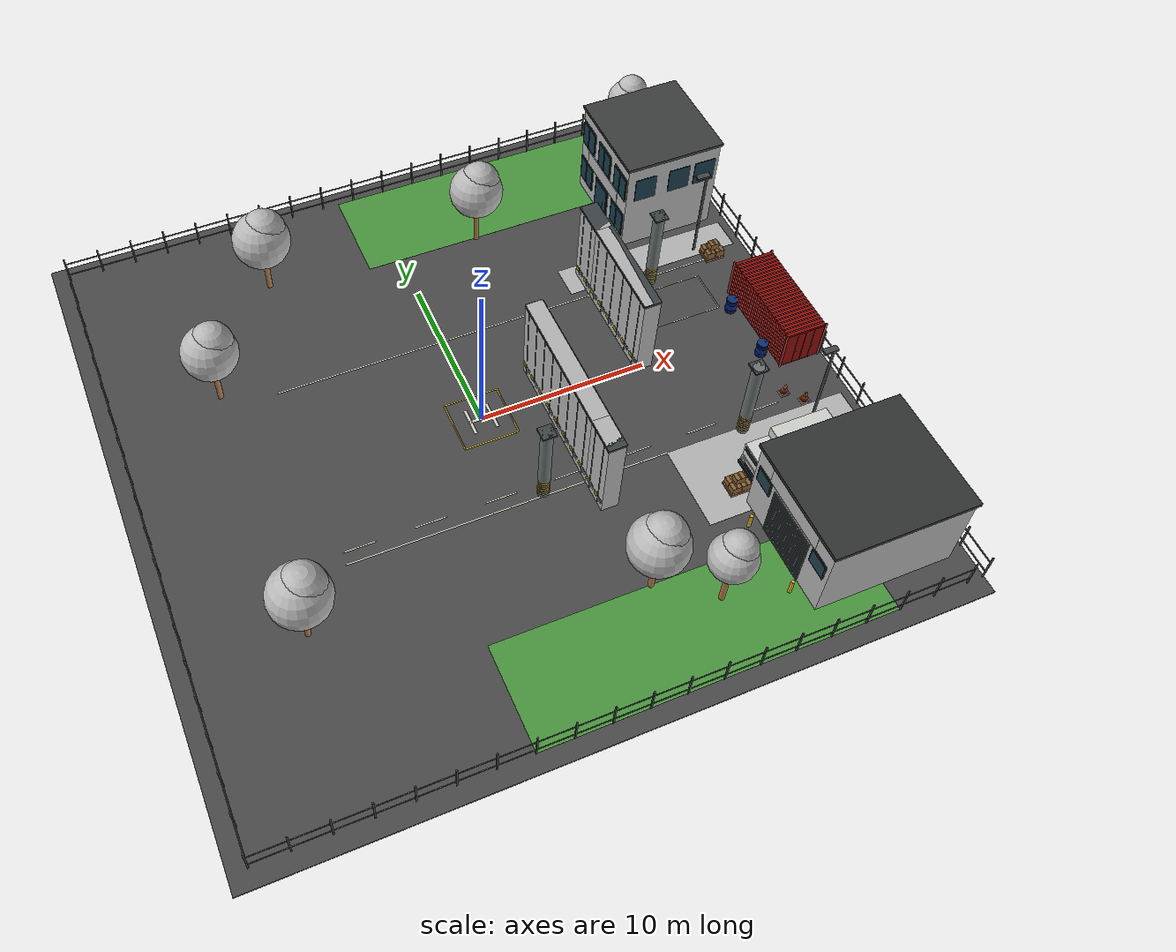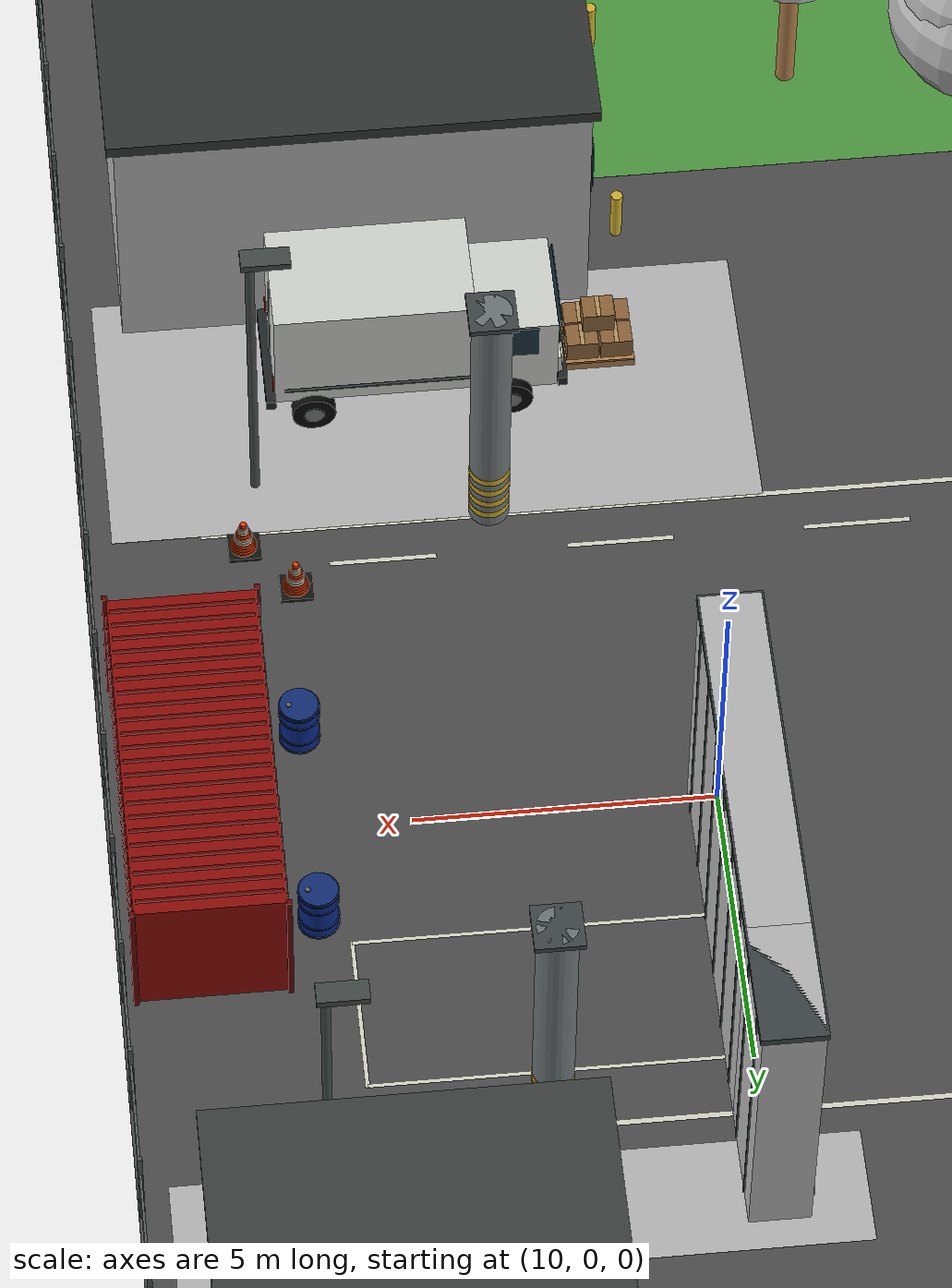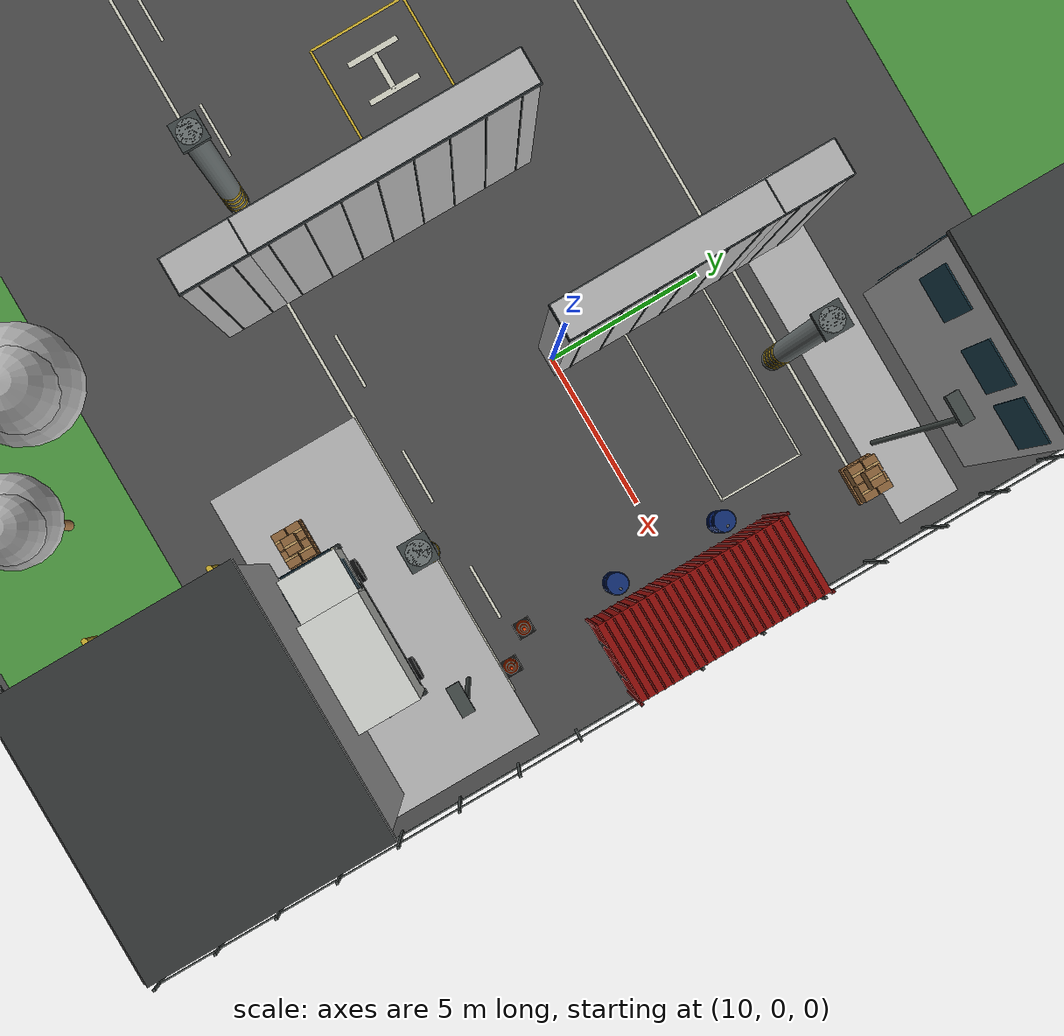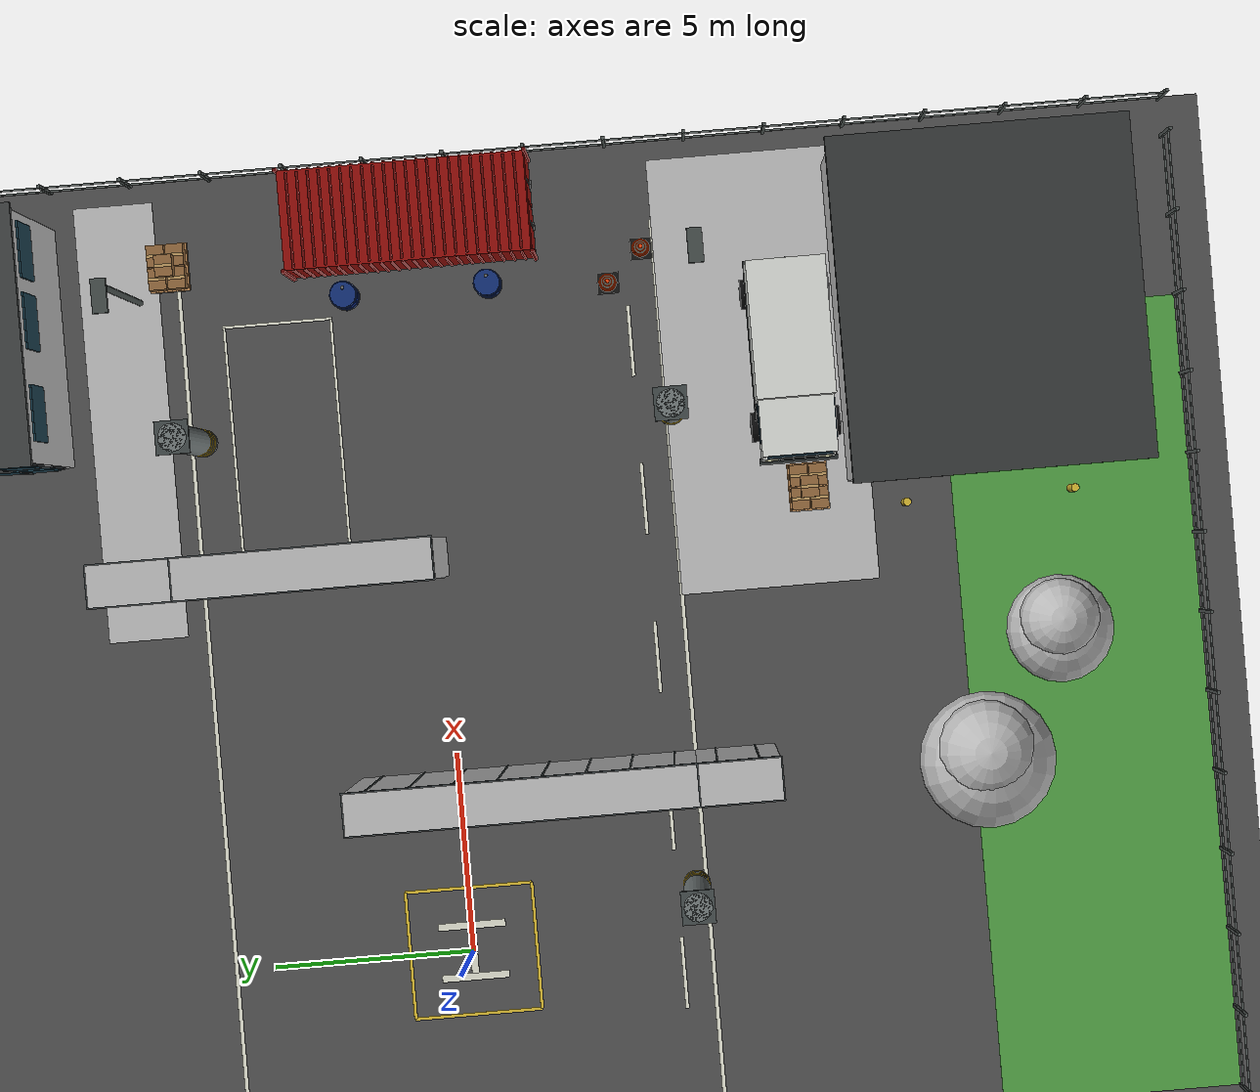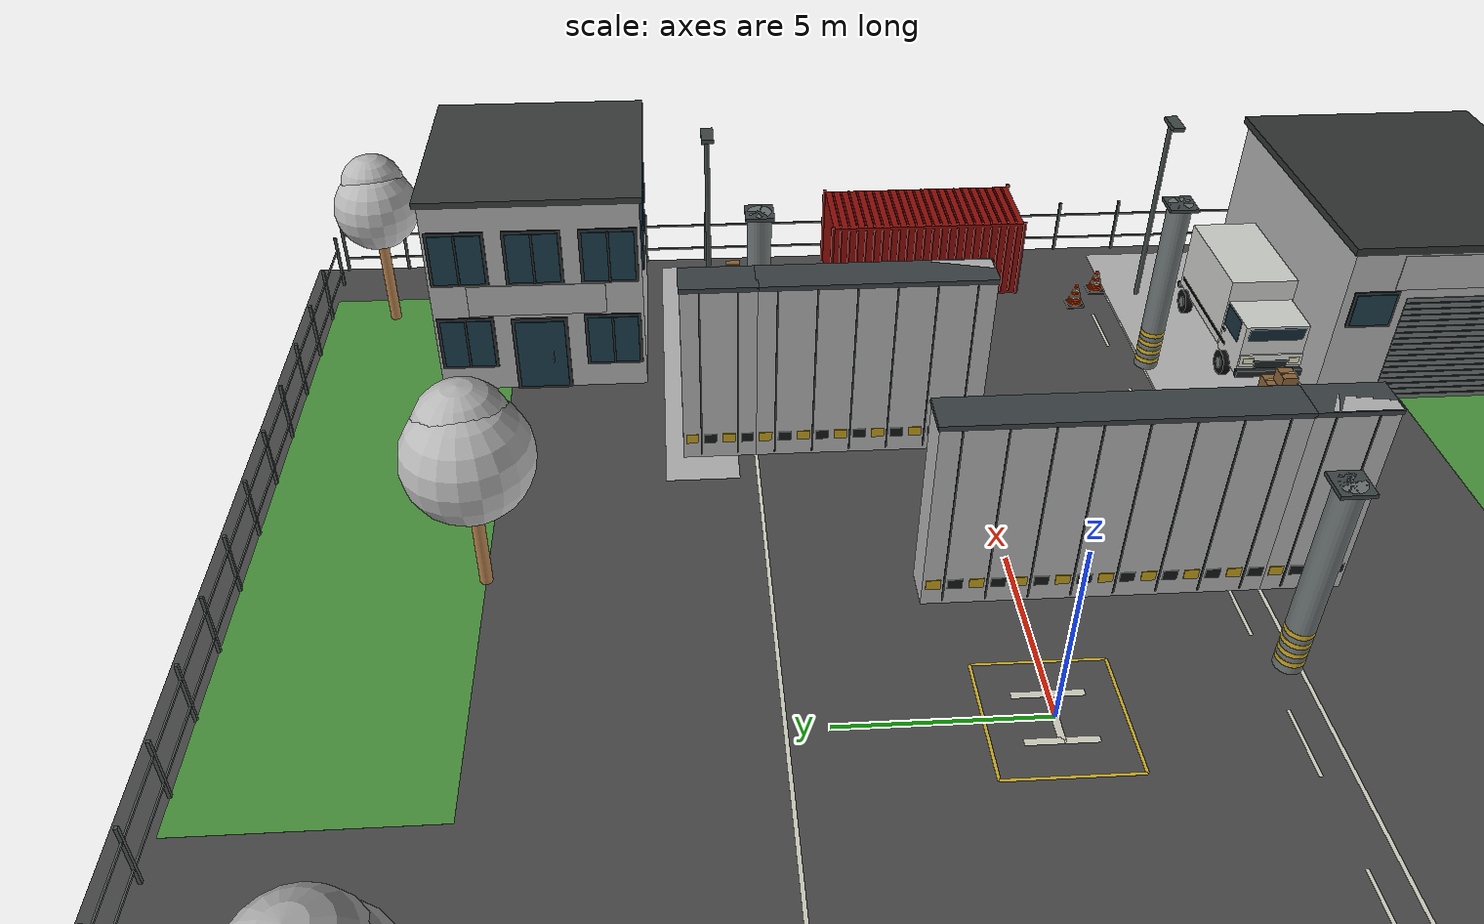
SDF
<?xml version='1.0' encoding='utf-8'?>
<sdf version="1.5">
  <world name="default">
    <include>
      <uri>model://sun</uri>
    </include>
    <scene>
      <ambient>.54 .56 .58 1</ambient>
      <background>.66 .76 .85 1</background>
      <shadows>true</shadows>
      <fog>
        <type>linear</type>
        <color>.72 .78 .83 1</color>
        <density>.001</density>
        <start>70</start>
        <end>150</end>
      </fog>
    </scene>
    <physics name="default_physics" default="0" type="ode">
      <gravity>0 0 -9.8066</gravity>
      <ode>
        <solver>
          <type>quick</type>
          <iters>10</iters>
          <sor>1.3</sor>
          <use_dynamic_moi_rescaling>0</use_dynamic_moi_rescaling>
        </solver>
        <constraints>
          <cfm>0</cfm>
          <erp>0.2</erp>
          <contact_max_correcting_vel>100</contact_max_correcting_vel>
          <contact_surface_layer>0.001</contact_surface_layer>
        </constraints>
      </ode>
      <max_step_size>0.004</max_step_size>
      <real_time_factor>1</real_time_factor>
      <real_time_update_rate>250</real_time_update_rate>
      <magnetic_field>6.0e-6 2.3e-5 -4.2e-5</magnetic_field>
    </physics>
    <gui fullscreen="0">
      <camera name="yard_overview">
        <pose>-16 -24 23 0 .57 .76</pose>
        <view_controller>orbit</view_controller>
      </camera>
    </gui>
    <model name="yard_ground">
      <static>true</static>
      <pose>0 0 0 0 0 0</pose>
      <link name="structure">
        <visual name="solid_ground">
          <pose>0 0 -0.047 0 0 0</pose>
          <geometry>
            <box>
              <size>40 40 0.1</size>
            </box>
          </geometry>
          <cast_shadows>true</cast_shadows>
          <material>
            <script>
              <uri>file:///home/fxxk/px4_agent/scene/materials/scripts</uri>
              <uri>file:///home/fxxk/px4_agent/scene/materials/textures</uri>
              <name>Yard/asphalt</name>
            </script>
          </material>
        </visual>
        <collision name="solid_ground_collision">
          <pose>0 0 -0.047 0 0 0</pose>
          <geometry>
            <box>
              <size>40 40 0.1</size>
            </box>
          </geometry>
          <surface>
            <friction>
              <ode>
                <mu>1.0</mu>
                <mu2>1.0</mu2>
              </ode>
            </friction>
          </surface>
        </collision>
        <visual name="west_lawn">
          <pose>-12.5 0 0.0032 0 0 0</pose>
          <geometry>
            <plane>
              <normal>0 0 1</normal>
              <size>15 38</size>
            </plane>
          </geometry>
          <cast_shadows>false</cast_shadows>
          <material>
            <script>
              <uri>file:///home/fxxk/px4_agent/scene/materials/scripts</uri>
              <uri>file:///home/fxxk/px4_agent/scene/materials/textures</uri>
              <name>Yard/grass</name>
            </script>
          </material>
        </visual>
        <visual name="north_lawn">
          <pose>8 16 0.0032 0 0 0</pose>
          <geometry>
            <plane>
              <normal>0 0 1</normal>
              <size>20 6</size>
            </plane>
          </geometry>
          <cast_shadows>false</cast_shadows>
          <material>
            <script>
              <uri>file:///home/fxxk/px4_agent/scene/materials/scripts</uri>
              <uri>file:///home/fxxk/px4_agent/scene/materials/textures</uri>
              <name>Yard/grass</name>
            </script>
          </material>
        </visual>
        <visual name="south_lawn">
          <pose>5 -16 0.0032 0 0 0</pose>
          <geometry>
            <plane>
              <normal>0 0 1</normal>
              <size>20 6</size>
            </plane>
          </geometry>
          <cast_shadows>false</cast_shadows>
          <material>
            <script>
              <uri>file:///home/fxxk/px4_agent/scene/materials/scripts</uri>
              <uri>file:///home/fxxk/px4_agent/scene/materials/textures</uri>
              <name>Yard/grass</name>
            </script>
          </material>
        </visual>
        <visual name="warehouse_apron">
          <pose>14 -8.5 0.0032 0 0 0</pose>
          <geometry>
            <plane>
              <normal>0 0 1</normal>
              <size>11 5</size>
            </plane>
          </geometry>
          <cast_shadows>false</cast_shadows>
          <material>
            <script>
              <uri>file:///home/fxxk/px4_agent/scene/materials/scripts</uri>
              <uri>file:///home/fxxk/px4_agent/scene/materials/textures</uri>
              <name>Yard/concrete</name>
            </script>
          </material>
        </visual>
        <visual name="office_walkway">
          <pose>14 7.5 0.0032 0 0 0</pose>
          <geometry>
            <plane>
              <normal>0 0 1</normal>
              <size>11 2</size>
            </plane>
          </geometry>
          <cast_shadows>false</cast_shadows>
          <material>
            <script>
              <uri>file:///home/fxxk/px4_agent/scene/materials/scripts</uri>
              <uri>file:///home/fxxk/px4_agent/scene/materials/textures</uri>
              <name>Yard/concrete</name>
            </script>
          </material>
        </visual>
        <visual name="road_edge_0">
          <pose>4 -6 0.0033 0 0 0</pose>
          <geometry>
            <box>
              <size>28 0.1 0.0001</size>
            </box>
          </geometry>
          <cast_shadows>false</cast_shadows>
          <material>
            <ambient>0.85 0.85 0.79 1</ambient>
            <diffuse>0.85 0.85 0.79 1</diffuse>
            <specular>0.04 0.04 0.04 1</specular>
          </material>
        </visual>
        <visual name="road_edge_1">
          <pose>4 6 0.0033 0 0 0</pose>
          <geometry>
            <box>
              <size>28 0.1 0.0001</size>
            </box>
          </geometry>
          <cast_shadows>false</cast_shadows>
          <material>
            <ambient>0.85 0.85 0.79 1</ambient>
            <diffuse>0.85 0.85 0.79 1</diffuse>
            <specular>0.04 0.04 0.04 1</specular>
          </material>
        </visual>
        <visual name="lane_dash_0">
          <pose>-9 -5.25 0.0033 0 0 0</pose>
          <geometry>
            <box>
              <size>1.8 0.09 0.0001</size>
            </box>
          </geometry>
          <cast_shadows>false</cast_shadows>
          <material>
            <ambient>0.85 0.85 0.79 1</ambient>
            <diffuse>0.85 0.85 0.79 1</diffuse>
            <specular>0.04 0.04 0.04 1</specular>
          </material>
        </visual>
        <visual name="lane_dash_1">
          <pose>-5 -5.25 0.0033 0 0 0</pose>
          <geometry>
            <box>
              <size>1.8 0.09 0.0001</size>
            </box>
          </geometry>
          <cast_shadows>false</cast_shadows>
          <material>
            <ambient>0.85 0.85 0.79 1</ambient>
            <diffuse>0.85 0.85 0.79 1</diffuse>
            <specular>0.04 0.04 0.04 1</specular>
          </material>
        </visual>
        <visual name="lane_dash_2">
          <pose>-1 -5.25 0.0033 0 0 0</pose>
          <geometry>
            <box>
              <size>1.8 0.09 0.0001</size>
            </box>
          </geometry>
          <cast_shadows>false</cast_shadows>
          <material>
            <ambient>0.85 0.85 0.79 1</ambient>
            <diffuse>0.85 0.85 0.79 1</diffuse>
            <specular>0.04 0.04 0.04 1</specular>
          </material>
        </visual>
        <visual name="lane_dash_3">
          <pose>3 -5.25 0.0033 0 0 0</pose>
          <geometry>
            <box>
              <size>1.8 0.09 0.0001</size>
            </box>
          </geometry>
          <cast_shadows>false</cast_shadows>
          <material>
            <ambient>0.85 0.85 0.79 1</ambient>
            <diffuse>0.85 0.85 0.79 1</diffuse>
            <specular>0.04 0.04 0.04 1</specular>
          </material>
        </visual>
        <visual name="lane_dash_4">
          <pose>7 -5.25 0.0033 0 0 0</pose>
          <geometry>
            <box>
              <size>1.8 0.09 0.0001</size>
            </box>
          </geometry>
          <cast_shadows>false</cast_shadows>
          <material>
            <ambient>0.85 0.85 0.79 1</ambient>
            <diffuse>0.85 0.85 0.79 1</diffuse>
            <specular>0.04 0.04 0.04 1</specular>
          </material>
        </visual>
        <visual name="lane_dash_5">
          <pose>11 -5.25 0.0033 0 0 0</pose>
          <geometry>
            <box>
              <size>1.8 0.09 0.0001</size>
            </box>
          </geometry>
          <cast_shadows>false</cast_shadows>
          <material>
            <ambient>0.85 0.85 0.79 1</ambient>
            <diffuse>0.85 0.85 0.79 1</diffuse>
            <specular>0.04 0.04 0.04 1</specular>
          </material>
        </visual>
        <visual name="lane_dash_6">
          <pose>15 -5.25 0.0033 0 0 0</pose>
          <geometry>
            <box>
              <size>1.8 0.09 0.0001</size>
            </box>
          </geometry>
          <cast_shadows>false</cast_shadows>
          <material>
            <ambient>0.85 0.85 0.79 1</ambient>
            <diffuse>0.85 0.85 0.79 1</diffuse>
            <specular>0.04 0.04 0.04 1</specular>
          </material>
        </visual>
        <visual name="parking_line_0">
          <pose>13 2.25 0.0033 0 0 0</pose>
          <geometry>
            <box>
              <size>6.4 0.07 0.0001</size>
            </box>
          </geometry>
          <cast_shadows>false</cast_shadows>
          <material>
            <ambient>0.85 0.85 0.79 1</ambient>
            <diffuse>0.85 0.85 0.79 1</diffuse>
            <specular>0.04 0.04 0.04 1</specular>
          </material>
        </visual>
        <visual name="parking_line_1">
          <pose>13 4.95 0.0033 0 0 0</pose>
          <geometry>
            <box>
              <size>6.4 0.07 0.0001</size>
            </box>
          </geometry>
          <cast_shadows>false</cast_shadows>
          <material>
            <ambient>0.85 0.85 0.79 1</ambient>
            <diffuse>0.85 0.85 0.79 1</diffuse>
            <specular>0.04 0.04 0.04 1</specular>
          </material>
        </visual>
        <visual name="parking_back">
          <pose>16.2 3.6 0.0033 0 0 0</pose>
          <geometry>
            <box>
              <size>0.07 2.77 0.0001</size>
            </box>
          </geometry>
          <cast_shadows>false</cast_shadows>
          <material>
            <ambient>0.85 0.85 0.79 1</ambient>
            <diffuse>0.85 0.85 0.79 1</diffuse>
            <specular>0.04 0.04 0.04 1</specular>
          </material>
        </visual>
        <visual name="h_left">
          <pose>-0.65 0 0.0033 0 0 0</pose>
          <geometry>
            <box>
              <size>0.18 1.7 0.0001</size>
            </box>
          </geometry>
          <cast_shadows>false</cast_shadows>
          <material>
            <ambient>0.85 0.85 0.79 1</ambient>
            <diffuse>0.85 0.85 0.79 1</diffuse>
            <specular>0.04 0.04 0.04 1</specular>
          </material>
        </visual>
        <visual name="h_right">
          <pose>0.65 0 0.0033 0 0 0</pose>
          <geometry>
            <box>
              <size>0.18 1.7 0.0001</size>
            </box>
          </geometry>
          <cast_shadows>false</cast_shadows>
          <material>
            <ambient>0.85 0.85 0.79 1</ambient>
            <diffuse>0.85 0.85 0.79 1</diffuse>
            <specular>0.04 0.04 0.04 1</specular>
          </material>
        </visual>
        <visual name="h_middle">
          <pose>0 0 0.0033 0 0 0</pose>
          <geometry>
            <box>
              <size>1.4 0.18 0.0001</size>
            </box>
          </geometry>
          <cast_shadows>false</cast_shadows>
          <material>
            <ambient>0.85 0.85 0.79 1</ambient>
            <diffuse>0.85 0.85 0.79 1</diffuse>
            <specular>0.04 0.04 0.04 1</specular>
          </material>
        </visual>
        <visual name="pad_border_0">
          <pose>0 -1.6 0.0033 0 0 0</pose>
          <geometry>
            <box>
              <size>3.2 0.08 0.0001</size>
            </box>
          </geometry>
          <cast_shadows>false</cast_shadows>
          <material>
            <ambient>0.82 0.7 0.18 1</ambient>
            <diffuse>0.82 0.7 0.18 1</diffuse>
            <specular>0.04 0.04 0.04 1</specular>
          </material>
        </visual>
        <visual name="pad_border_1">
          <pose>0 1.6 0.0033 0 0 0</pose>
          <geometry>
            <box>
              <size>3.2 0.08 0.0001</size>
            </box>
          </geometry>
          <cast_shadows>false</cast_shadows>
          <material>
            <ambient>0.82 0.7 0.18 1</ambient>
            <diffuse>0.82 0.7 0.18 1</diffuse>
            <specular>0.04 0.04 0.04 1</specular>
          </material>
        </visual>
        <visual name="pad_border_2">
          <pose>-1.6 0 0.0033 0 0 0</pose>
          <geometry>
            <box>
              <size>0.08 3.2 0.0001</size>
            </box>
          </geometry>
          <cast_shadows>false</cast_shadows>
          <material>
            <ambient>0.82 0.7 0.18 1</ambient>
            <diffuse>0.82 0.7 0.18 1</diffuse>
            <specular>0.04 0.04 0.04 1</specular>
          </material>
        </visual>
        <visual name="pad_border_3">
          <pose>1.6 0 0.0033 0 0 0</pose>
          <geometry>
            <box>
              <size>0.08 3.2 0.0001</size>
            </box>
          </geometry>
          <cast_shadows>false</cast_shadows>
          <material>
            <ambient>0.82 0.7 0.18 1</ambient>
            <diffuse>0.82 0.7 0.18 1</diffuse>
            <specular>0.04 0.04 0.04 1</specular>
          </material>
        </visual>
      </link>
    </model>
    <model name="obstacle_wall_1">
      <static>true</static>
      <pose>4.078 -1.793 0.003 0 0 0</pose>
      <link name="structure">
        <visual name="collision_wall">
          <pose>0 0 2.75 0 0 0</pose>
          <geometry>
            <box>
              <size>1 8.414 5.5</size>
            </box>
          </geometry>
          <cast_shadows>true</cast_shadows>
          <material>
            <script>
              <uri>file:///home/fxxk/px4_agent/scene/materials/scripts</uri>
              <uri>file:///home/fxxk/px4_agent/scene/materials/textures</uri>
              <name>Yard/concrete</name>
            </script>
          </material>
        </visual>
        <collision name="collision_wall_collision">
          <pose>0 0 2.75 0 0 0</pose>
          <geometry>
            <box>
              <size>1 8.414 5.5</size>
            </box>
          </geometry>
          <surface>
            <friction>
              <ode>
                <mu>1.0</mu>
                <mu2>1.0</mu2>
              </ode>
            </friction>
          </surface>
        </collision>
        <visual name="wall_coping">
          <pose>0 0 5.435 0 0 0</pose>
          <geometry>
            <box>
              <size>1.06 8.477105 0.13</size>
            </box>
          </geometry>
          <cast_shadows>true</cast_shadows>
          <material>
            <ambient>0.24 0.27 0.28 1</ambient>
            <diffuse>0.24 0.27 0.28 1</diffuse>
            <specular>0.04 0.04 0.04 1</specular>
          </material>
        </visual>
        <visual name="panel_joint_-1_0">
          <pose>-0.513 -3.681125 2.75 0 0 0</pose>
          <geometry>
            <box>
              <size>0.028 0.0357595 5.3</size>
            </box>
          </geometry>
          <cast_shadows>true</cast_shadows>
          <material>
            <ambient>0.26 0.29 0.29 1</ambient>
            <diffuse>0.26 0.29 0.29 1</diffuse>
            <specular>0.04 0.04 0.04 1</specular>
          </material>
        </visual>
        <visual name="panel_joint_1_0">
          <pose>0.513 -3.681125 2.75 0 0 0</pose>
          <geometry>
            <box>
              <size>0.028 0.0357595 5.3</size>
            </box>
          </geometry>
          <cast_shadows>true</cast_shadows>
          <material>
            <ambient>0.26 0.29 0.29 1</ambient>
            <diffuse>0.26 0.29 0.29 1</diffuse>
            <specular>0.04 0.04 0.04 1</specular>
          </material>
        </visual>
        <visual name="panel_joint_-1_1">
          <pose>-0.513 -2.629375 2.75 0 0 0</pose>
          <geometry>
            <box>
              <size>0.028 0.0357595 5.3</size>
            </box>
          </geometry>
          <cast_shadows>true</cast_shadows>
          <material>
            <ambient>0.26 0.29 0.29 1</ambient>
            <diffuse>0.26 0.29 0.29 1</diffuse>
            <specular>0.04 0.04 0.04 1</specular>
          </material>
        </visual>
        <visual name="panel_joint_1_1">
          <pose>0.513 -2.629375 2.75 0 0 0</pose>
          <geometry>
            <box>
              <size>0.028 0.0357595 5.3</size>
            </box>
          </geometry>
          <cast_shadows>true</cast_shadows>
          <material>
            <ambient>0.26 0.29 0.29 1</ambient>
            <diffuse>0.26 0.29 0.29 1</diffuse>
            <specular>0.04 0.04 0.04 1</specular>
          </material>
        </visual>
        <visual name="panel_joint_-1_2">
          <pose>-0.513 -1.577625 2.75 0 0 0</pose>
          <geometry>
            <box>
              <size>0.028 0.0357595 5.3</size>
            </box>
          </geometry>
          <cast_shadows>true</cast_shadows>
          <material>
            <ambient>0.26 0.29 0.29 1</ambient>
            <diffuse>0.26 0.29 0.29 1</diffuse>
            <specular>0.04 0.04 0.04 1</specular>
          </material>
        </visual>
        <visual name="panel_joint_1_2">
          <pose>0.513 -1.577625 2.75 0 0 0</pose>
          <geometry>
            <box>
              <size>0.028 0.0357595 5.3</size>
            </box>
          </geometry>
          <cast_shadows>true</cast_shadows>
          <material>
            <ambient>0.26 0.29 0.29 1</ambient>
            <diffuse>0.26 0.29 0.29 1</diffuse>
            <specular>0.04 0.04 0.04 1</specular>
          </material>
        </visual>
        <visual name="panel_joint_-1_3">
          <pose>-0.513 -0.525875 2.75 0 0 0</pose>
          <geometry>
            <box>
              <size>0.028 0.0357595 5.3</size>
            </box>
          </geometry>
          <cast_shadows>true</cast_shadows>
          <material>
            <ambient>0.26 0.29 0.29 1</ambient>
            <diffuse>0.26 0.29 0.29 1</diffuse>
            <specular>0.04 0.04 0.04 1</specular>
          </material>
        </visual>
        <visual name="panel_joint_1_3">
          <pose>0.513 -0.525875 2.75 0 0 0</pose>
          <geometry>
            <box>
              <size>0.028 0.0357595 5.3</size>
            </box>
          </geometry>
          <cast_shadows>true</cast_shadows>
          <material>
            <ambient>0.26 0.29 0.29 1</ambient>
            <diffuse>0.26 0.29 0.29 1</diffuse>
            <specular>0.04 0.04 0.04 1</specular>
          </material>
        </visual>
        <visual name="panel_joint_-1_4">
          <pose>-0.513 0.525875 2.75 0 0 0</pose>
          <geometry>
            <box>
              <size>0.028 0.0357595 5.3</size>
            </box>
          </geometry>
          <cast_shadows>true</cast_shadows>
          <material>
            <ambient>0.26 0.29 0.29 1</ambient>
            <diffuse>0.26 0.29 0.29 1</diffuse>
            <specular>0.04 0.04 0.04 1</specular>
          </material>
        </visual>
        <visual name="panel_joint_1_4">
          <pose>0.513 0.525875 2.75 0 0 0</pose>
          <geometry>
            <box>
              <size>0.028 0.0357595 5.3</size>
            </box>
          </geometry>
          <cast_shadows>true</cast_shadows>
          <material>
            <ambient>0.26 0.29 0.29 1</ambient>
            <diffuse>0.26 0.29 0.29 1</diffuse>
            <specular>0.04 0.04 0.04 1</specular>
          </material>
        </visual>
        <visual name="panel_joint_-1_5">
          <pose>-0.513 1.577625 2.75 0 0 0</pose>
          <geometry>
            <box>
              <size>0.028 0.0357595 5.3</size>
            </box>
          </geometry>
          <cast_shadows>true</cast_shadows>
          <material>
            <ambient>0.26 0.29 0.29 1</ambient>
            <diffuse>0.26 0.29 0.29 1</diffuse>
            <specular>0.04 0.04 0.04 1</specular>
          </material>
        </visual>
        <visual name="panel_joint_1_5">
          <pose>0.513 1.577625 2.75 0 0 0</pose>
          <geometry>
            <box>
              <size>0.028 0.0357595 5.3</size>
            </box>
          </geometry>
          <cast_shadows>true</cast_shadows>
          <material>
            <ambient>0.26 0.29 0.29 1</ambient>
            <diffuse>0.26 0.29 0.29 1</diffuse>
            <specular>0.04 0.04 0.04 1</specular>
          </material>
        </visual>
        <visual name="panel_joint_-1_6">
          <pose>-0.513 2.629375 2.75 0 0 0</pose>
          <geometry>
            <box>
              <size>0.028 0.0357595 5.3</size>
            </box>
          </geometry>
          <cast_shadows>true</cast_shadows>
          <material>
            <ambient>0.26 0.29 0.29 1</ambient>
            <diffuse>0.26 0.29 0.29 1</diffuse>
            <specular>0.04 0.04 0.04 1</specular>
          </material>
        </visual>
        <visual name="panel_joint_1_6">
          <pose>0.513 2.629375 2.75 0 0 0</pose>
          <geometry>
            <box>
              <size>0.028 0.0357595 5.3</size>
            </box>
          </geometry>
          <cast_shadows>true</cast_shadows>
          <material>
            <ambient>0.26 0.29 0.29 1</ambient>
            <diffuse>0.26 0.29 0.29 1</diffuse>
            <specular>0.04 0.04 0.04 1</specular>
          </material>
        </visual>
        <visual name="panel_joint_-1_7">
          <pose>-0.513 3.681125 2.75 0 0 0</pose>
          <geometry>
            <box>
              <size>0.028 0.0357595 5.3</size>
            </box>
          </geometry>
          <cast_shadows>true</cast_shadows>
          <material>
            <ambient>0.26 0.29 0.29 1</ambient>
            <diffuse>0.26 0.29 0.29 1</diffuse>
            <specular>0.04 0.04 0.04 1</specular>
          </material>
        </visual>
        <visual name="panel_joint_1_7">
          <pose>0.513 3.681125 2.75 0 0 0</pose>
          <geometry>
            <box>
              <size>0.028 0.0357595 5.3</size>
            </box>
          </geometry>
          <cast_shadows>true</cast_shadows>
          <material>
            <ambient>0.26 0.29 0.29 1</ambient>
            <diffuse>0.26 0.29 0.29 1</diffuse>
            <specular>0.04 0.04 0.04 1</specular>
          </material>
        </visual>
        <visual name="safety_band_0">
          <pose>-0.517 -3.9440625 0.65 0 0 0</pose>
          <geometry>
            <box>
              <size>0.025 0.357595 0.28</size>
            </box>
          </geometry>
          <cast_shadows>true</cast_shadows>
          <material>
            <ambient>0.075 0.085 0.085 1</ambient>
            <diffuse>0.075 0.085 0.085 1</diffuse>
            <specular>0.04 0.04 0.04 1</specular>
          </material>
        </visual>
        <visual name="safety_band_1">
          <pose>-0.517 -3.4181875 0.65 0 0 0</pose>
          <geometry>
            <box>
              <size>0.025 0.357595 0.28</size>
            </box>
          </geometry>
          <cast_shadows>true</cast_shadows>
          <material>
            <ambient>0.78 0.64 0.1 1</ambient>
            <diffuse>0.78 0.64 0.1 1</diffuse>
            <specular>0.04 0.04 0.04 1</specular>
          </material>
        </visual>
        <visual name="safety_band_2">
          <pose>-0.517 -2.8923125 0.65 0 0 0</pose>
          <geometry>
            <box>
              <size>0.025 0.357595 0.28</size>
            </box>
          </geometry>
          <cast_shadows>true</cast_shadows>
          <material>
            <ambient>0.075 0.085 0.085 1</ambient>
            <diffuse>0.075 0.085 0.085 1</diffuse>
            <specular>0.04 0.04 0.04 1</specular>
          </material>
        </visual>
        <visual name="safety_band_3">
          <pose>-0.517 -2.3664375 0.65 0 0 0</pose>
          <geometry>
            <box>
              <size>0.025 0.357595 0.28</size>
            </box>
          </geometry>
          <cast_shadows>true</cast_shadows>
          <material>
            <ambient>0.78 0.64 0.1 1</ambient>
            <diffuse>0.78 0.64 0.1 1</diffuse>
            <specular>0.04 0.04 0.04 1</specular>
          </material>
        </visual>
        <visual name="safety_band_4">
          <pose>-0.517 -1.8405625 0.65 0 0 0</pose>
          <geometry>
            <box>
              <size>0.025 0.357595 0.28</size>
            </box>
          </geometry>
          <cast_shadows>true</cast_shadows>
          <material>
            <ambient>0.075 0.085 0.085 1</ambient>
            <diffuse>0.075 0.085 0.085 1</diffuse>
            <specular>0.04 0.04 0.04 1</specular>
          </material>
        </visual>
        <visual name="safety_band_5">
          <pose>-0.517 -1.3146875 0.65 0 0 0</pose>
          <geometry>
            <box>
              <size>0.025 0.357595 0.28</size>
            </box>
          </geometry>
          <cast_shadows>true</cast_shadows>
          <material>
            <ambient>0.78 0.64 0.1 1</ambient>
            <diffuse>0.78 0.64 0.1 1</diffuse>
            <specular>0.04 0.04 0.04 1</specular>
          </material>
        </visual>
        <visual name="safety_band_6">
          <pose>-0.517 -0.7888125 0.65 0 0 0</pose>
          <geometry>
            <box>
              <size>0.025 0.357595 0.28</size>
            </box>
          </geometry>
          <cast_shadows>true</cast_shadows>
          <material>
            <ambient>0.075 0.085 0.085 1</ambient>
            <diffuse>0.075 0.085 0.085 1</diffuse>
            <specular>0.04 0.04 0.04 1</specular>
          </material>
        </visual>
        <visual name="safety_band_7">
          <pose>-0.517 -0.2629375 0.65 0 0 0</pose>
          <geometry>
            <box>
              <size>0.025 0.357595 0.28</size>
            </box>
          </geometry>
          <cast_shadows>true</cast_shadows>
          <material>
            <ambient>0.78 0.64 0.1 1</ambient>
            <diffuse>0.78 0.64 0.1 1</diffuse>
            <specular>0.04 0.04 0.04 1</specular>
          </material>
        </visual>
        <visual name="safety_band_8">
          <pose>-0.517 0.2629375 0.65 0 0 0</pose>
          <geometry>
            <box>
              <size>0.025 0.357595 0.28</size>
            </box>
          </geometry>
          <cast_shadows>true</cast_shadows>
          <material>
            <ambient>0.075 0.085 0.085 1</ambient>
            <diffuse>0.075 0.085 0.085 1</diffuse>
            <specular>0.04 0.04 0.04 1</specular>
          </material>
        </visual>
        <visual name="safety_band_9">
          <pose>-0.517 0.7888125 0.65 0 0 0</pose>
          <geometry>
            <box>
              <size>0.025 0.357595 0.28</size>
            </box>
          </geometry>
          <cast_shadows>true</cast_shadows>
          <material>
            <ambient>0.78 0.64 0.1 1</ambient>
            <diffuse>0.78 0.64 0.1 1</diffuse>
            <specular>0.04 0.04 0.04 1</specular>
          </material>
        </visual>
        <visual name="safety_band_10">
          <pose>-0.517 1.3146875 0.65 0 0 0</pose>
          <geometry>
            <box>
              <size>0.025 0.357595 0.28</size>
            </box>
          </geometry>
          <cast_shadows>true</cast_shadows>
          <material>
            <ambient>0.075 0.085 0.085 1</ambient>
            <diffuse>0.075 0.085 0.085 1</diffuse>
            <specular>0.04 0.04 0.04 1</specular>
          </material>
        </visual>
        <visual name="safety_band_11">
          <pose>-0.517 1.8405625 0.65 0 0 0</pose>
          <geometry>
            <box>
              <size>0.025 0.357595 0.28</size>
            </box>
          </geometry>
          <cast_shadows>true</cast_shadows>
          <material>
            <ambient>0.78 0.64 0.1 1</ambient>
            <diffuse>0.78 0.64 0.1 1</diffuse>
            <specular>0.04 0.04 0.04 1</specular>
          </material>
        </visual>
        <visual name="safety_band_12">
          <pose>-0.517 2.3664375 0.65 0 0 0</pose>
          <geometry>
            <box>
              <size>0.025 0.357595 0.28</size>
            </box>
          </geometry>
          <cast_shadows>true</cast_shadows>
          <material>
            <ambient>0.075 0.085 0.085 1</ambient>
            <diffuse>0.075 0.085 0.085 1</diffuse>
            <specular>0.04 0.04 0.04 1</specular>
          </material>
        </visual>
        <visual name="safety_band_13">
          <pose>-0.517 2.8923125 0.65 0 0 0</pose>
          <geometry>
            <box>
              <size>0.025 0.357595 0.28</size>
            </box>
          </geometry>
          <cast_shadows>true</cast_shadows>
          <material>
            <ambient>0.78 0.64 0.1 1</ambient>
            <diffuse>0.78 0.64 0.1 1</diffuse>
            <specular>0.04 0.04 0.04 1</specular>
          </material>
        </visual>
        <visual name="safety_band_14">
          <pose>-0.517 3.4181875 0.65 0 0 0</pose>
          <geometry>
            <box>
              <size>0.025 0.357595 0.28</size>
            </box>
          </geometry>
          <cast_shadows>true</cast_shadows>
          <material>
            <ambient>0.075 0.085 0.085 1</ambient>
            <diffuse>0.075 0.085 0.085 1</diffuse>
            <specular>0.04 0.04 0.04 1</specular>
          </material>
        </visual>
        <visual name="safety_band_15">
          <pose>-0.517 3.9440625 0.65 0 0 0</pose>
          <geometry>
            <box>
              <size>0.025 0.357595 0.28</size>
            </box>
          </geometry>
          <cast_shadows>true</cast_shadows>
          <material>
            <ambient>0.78 0.64 0.1 1</ambient>
            <diffuse>0.78 0.64 0.1 1</diffuse>
            <specular>0.04 0.04 0.04 1</specular>
          </material>
        </visual>
      </link>
    </model>
    <model name="obstacle_wall_2">
      <static>true</static>
      <pose>9.971 2.9055 0.003 0 0 0</pose>
      <link name="structure">
        <visual name="collision_wall">
          <pose>0 0 2.75 0 0 0</pose>
          <geometry>
            <box>
              <size>1 6.189 5.5</size>
            </box>
          </geometry>
          <cast_shadows>true</cast_shadows>
          <material>
            <script>
              <uri>file:///home/fxxk/px4_agent/scene/materials/scripts</uri>
              <uri>file:///home/fxxk/px4_agent/scene/materials/textures</uri>
              <name>Yard/concrete</name>
            </script>
          </material>
        </visual>
        <collision name="collision_wall_collision">
          <pose>0 0 2.75 0 0 0</pose>
          <geometry>
            <box>
              <size>1 6.189 5.5</size>
            </box>
          </geometry>
          <surface>
            <friction>
              <ode>
                <mu>1.0</mu>
                <mu2>1.0</mu2>
              </ode>
            </friction>
          </surface>
        </collision>
        <visual name="wall_coping">
          <pose>0 0 5.435 0 0 0</pose>
          <geometry>
            <box>
              <size>1.06 6.25089 0.13</size>
            </box>
          </geometry>
          <cast_shadows>true</cast_shadows>
          <material>
            <ambient>0.24 0.27 0.28 1</ambient>
            <diffuse>0.24 0.27 0.28 1</diffuse>
            <specular>0.04 0.04 0.04 1</specular>
          </material>
        </visual>
        <visual name="panel_joint_-1_0">
          <pose>-0.513 -2.57875 2.75 0 0 0</pose>
          <geometry>
            <box>
              <size>0.028 0.035071 5.3</size>
            </box>
          </geometry>
          <cast_shadows>true</cast_shadows>
          <material>
            <ambient>0.26 0.29 0.29 1</ambient>
            <diffuse>0.26 0.29 0.29 1</diffuse>
            <specular>0.04 0.04 0.04 1</specular>
          </material>
        </visual>
        <visual name="panel_joint_1_0">
          <pose>0.513 -2.57875 2.75 0 0 0</pose>
          <geometry>
            <box>
              <size>0.028 0.035071 5.3</size>
            </box>
          </geometry>
          <cast_shadows>true</cast_shadows>
          <material>
            <ambient>0.26 0.29 0.29 1</ambient>
            <diffuse>0.26 0.29 0.29 1</diffuse>
            <specular>0.04 0.04 0.04 1</specular>
          </material>
        </visual>
        <visual name="panel_joint_-1_1">
          <pose>-0.513 -1.54725 2.75 0 0 0</pose>
          <geometry>
            <box>
              <size>0.028 0.035071 5.3</size>
            </box>
          </geometry>
          <cast_shadows>true</cast_shadows>
          <material>
            <ambient>0.26 0.29 0.29 1</ambient>
            <diffuse>0.26 0.29 0.29 1</diffuse>
            <specular>0.04 0.04 0.04 1</specular>
          </material>
        </visual>
        <visual name="panel_joint_1_1">
          <pose>0.513 -1.54725 2.75 0 0 0</pose>
          <geometry>
            <box>
              <size>0.028 0.035071 5.3</size>
            </box>
          </geometry>
          <cast_shadows>true</cast_shadows>
          <material>
            <ambient>0.26 0.29 0.29 1</ambient>
            <diffuse>0.26 0.29 0.29 1</diffuse>
            <specular>0.04 0.04 0.04 1</specular>
          </material>
        </visual>
        <visual name="panel_joint_-1_2">
          <pose>-0.513 -0.51575 2.75 0 0 0</pose>
          <geometry>
            <box>
              <size>0.028 0.035071 5.3</size>
            </box>
          </geometry>
          <cast_shadows>true</cast_shadows>
          <material>
            <ambient>0.26 0.29 0.29 1</ambient>
            <diffuse>0.26 0.29 0.29 1</diffuse>
            <specular>0.04 0.04 0.04 1</specular>
          </material>
        </visual>
        <visual name="panel_joint_1_2">
          <pose>0.513 -0.51575 2.75 0 0 0</pose>
          <geometry>
            <box>
              <size>0.028 0.035071 5.3</size>
            </box>
          </geometry>
          <cast_shadows>true</cast_shadows>
          <material>
            <ambient>0.26 0.29 0.29 1</ambient>
            <diffuse>0.26 0.29 0.29 1</diffuse>
            <specular>0.04 0.04 0.04 1</specular>
          </material>
        </visual>
        <visual name="panel_joint_-1_3">
          <pose>-0.513 0.51575 2.75 0 0 0</pose>
          <geometry>
            <box>
              <size>0.028 0.035071 5.3</size>
            </box>
          </geometry>
          <cast_shadows>true</cast_shadows>
          <material>
            <ambient>0.26 0.29 0.29 1</ambient>
            <diffuse>0.26 0.29 0.29 1</diffuse>
            <specular>0.04 0.04 0.04 1</specular>
          </material>
        </visual>
        <visual name="panel_joint_1_3">
          <pose>0.513 0.51575 2.75 0 0 0</pose>
          <geometry>
            <box>
              <size>0.028 0.035071 5.3</size>
            </box>
          </geometry>
          <cast_shadows>true</cast_shadows>
          <material>
            <ambient>0.26 0.29 0.29 1</ambient>
            <diffuse>0.26 0.29 0.29 1</diffuse>
            <specular>0.04 0.04 0.04 1</specular>
          </material>
        </visual>
        <visual name="panel_joint_-1_4">
          <pose>-0.513 1.54725 2.75 0 0 0</pose>
          <geometry>
            <box>
              <size>0.028 0.035071 5.3</size>
            </box>
          </geometry>
          <cast_shadows>true</cast_shadows>
          <material>
            <ambient>0.26 0.29 0.29 1</ambient>
            <diffuse>0.26 0.29 0.29 1</diffuse>
            <specular>0.04 0.04 0.04 1</specular>
          </material>
        </visual>
        <visual name="panel_joint_1_4">
          <pose>0.513 1.54725 2.75 0 0 0</pose>
          <geometry>
            <box>
              <size>0.028 0.035071 5.3</size>
            </box>
          </geometry>
          <cast_shadows>true</cast_shadows>
          <material>
            <ambient>0.26 0.29 0.29 1</ambient>
            <diffuse>0.26 0.29 0.29 1</diffuse>
            <specular>0.04 0.04 0.04 1</specular>
          </material>
        </visual>
        <visual name="panel_joint_-1_5">
          <pose>-0.513 2.57875 2.75 0 0 0</pose>
          <geometry>
            <box>
              <size>0.028 0.035071 5.3</size>
            </box>
          </geometry>
          <cast_shadows>true</cast_shadows>
          <material>
            <ambient>0.26 0.29 0.29 1</ambient>
            <diffuse>0.26 0.29 0.29 1</diffuse>
            <specular>0.04 0.04 0.04 1</specular>
          </material>
        </visual>
        <visual name="panel_joint_1_5">
          <pose>0.513 2.57875 2.75 0 0 0</pose>
          <geometry>
            <box>
              <size>0.028 0.035071 5.3</size>
            </box>
          </geometry>
          <cast_shadows>true</cast_shadows>
          <material>
            <ambient>0.26 0.29 0.29 1</ambient>
            <diffuse>0.26 0.29 0.29 1</diffuse>
            <specular>0.04 0.04 0.04 1</specular>
          </material>
        </visual>
        <visual name="safety_band_0">
          <pose>-0.517 -2.836625 0.65 0 0 0</pose>
          <geometry>
            <box>
              <size>0.025 0.35071 0.28</size>
            </box>
          </geometry>
          <cast_shadows>true</cast_shadows>
          <material>
            <ambient>0.075 0.085 0.085 1</ambient>
            <diffuse>0.075 0.085 0.085 1</diffuse>
            <specular>0.04 0.04 0.04 1</specular>
          </material>
        </visual>
        <visual name="safety_band_1">
          <pose>-0.517 -2.320875 0.65 0 0 0</pose>
          <geometry>
            <box>
              <size>0.025 0.35071 0.28</size>
            </box>
          </geometry>
          <cast_shadows>true</cast_shadows>
          <material>
            <ambient>0.78 0.64 0.1 1</ambient>
            <diffuse>0.78 0.64 0.1 1</diffuse>
            <specular>0.04 0.04 0.04 1</specular>
          </material>
        </visual>
        <visual name="safety_band_2">
          <pose>-0.517 -1.805125 0.65 0 0 0</pose>
          <geometry>
            <box>
              <size>0.025 0.35071 0.28</size>
            </box>
          </geometry>
          <cast_shadows>true</cast_shadows>
          <material>
            <ambient>0.075 0.085 0.085 1</ambient>
            <diffuse>0.075 0.085 0.085 1</diffuse>
            <specular>0.04 0.04 0.04 1</specular>
          </material>
        </visual>
        <visual name="safety_band_3">
          <pose>-0.517 -1.289375 0.65 0 0 0</pose>
          <geometry>
            <box>
              <size>0.025 0.35071 0.28</size>
            </box>
          </geometry>
          <cast_shadows>true</cast_shadows>
          <material>
            <ambient>0.78 0.64 0.1 1</ambient>
            <diffuse>0.78 0.64 0.1 1</diffuse>
            <specular>0.04 0.04 0.04 1</specular>
          </material>
        </visual>
        <visual name="safety_band_4">
          <pose>-0.517 -0.773625 0.65 0 0 0</pose>
          <geometry>
            <box>
              <size>0.025 0.35071 0.28</size>
            </box>
          </geometry>
          <cast_shadows>true</cast_shadows>
          <material>
            <ambient>0.075 0.085 0.085 1</ambient>
            <diffuse>0.075 0.085 0.085 1</diffuse>
            <specular>0.04 0.04 0.04 1</specular>
          </material>
        </visual>
        <visual name="safety_band_5">
          <pose>-0.517 -0.257875 0.65 0 0 0</pose>
          <geometry>
            <box>
              <size>0.025 0.35071 0.28</size>
            </box>
          </geometry>
          <cast_shadows>true</cast_shadows>
          <material>
            <ambient>0.78 0.64 0.1 1</ambient>
            <diffuse>0.78 0.64 0.1 1</diffuse>
            <specular>0.04 0.04 0.04 1</specular>
          </material>
        </visual>
        <visual name="safety_band_6">
          <pose>-0.517 0.257875 0.65 0 0 0</pose>
          <geometry>
            <box>
              <size>0.025 0.35071 0.28</size>
            </box>
          </geometry>
          <cast_shadows>true</cast_shadows>
          <material>
            <ambient>0.075 0.085 0.085 1</ambient>
            <diffuse>0.075 0.085 0.085 1</diffuse>
            <specular>0.04 0.04 0.04 1</specular>
          </material>
        </visual>
        <visual name="safety_band_7">
          <pose>-0.517 0.773625 0.65 0 0 0</pose>
          <geometry>
            <box>
              <size>0.025 0.35071 0.28</size>
            </box>
          </geometry>
          <cast_shadows>true</cast_shadows>
          <material>
            <ambient>0.78 0.64 0.1 1</ambient>
            <diffuse>0.78 0.64 0.1 1</diffuse>
            <specular>0.04 0.04 0.04 1</specular>
          </material>
        </visual>
        <visual name="safety_band_8">
          <pose>-0.517 1.289375 0.65 0 0 0</pose>
          <geometry>
            <box>
              <size>0.025 0.35071 0.28</size>
            </box>
          </geometry>
          <cast_shadows>true</cast_shadows>
          <material>
            <ambient>0.075 0.085 0.085 1</ambient>
            <diffuse>0.075 0.085 0.085 1</diffuse>
            <specular>0.04 0.04 0.04 1</specular>
          </material>
        </visual>
        <visual name="safety_band_9">
          <pose>-0.517 1.805125 0.65 0 0 0</pose>
          <geometry>
            <box>
              <size>0.025 0.35071 0.28</size>
            </box>
          </geometry>
          <cast_shadows>true</cast_shadows>
          <material>
            <ambient>0.78 0.64 0.1 1</ambient>
            <diffuse>0.78 0.64 0.1 1</diffuse>
            <specular>0.04 0.04 0.04 1</specular>
          </material>
        </visual>
        <visual name="safety_band_10">
          <pose>-0.517 2.320875 0.65 0 0 0</pose>
          <geometry>
            <box>
              <size>0.025 0.35071 0.28</size>
            </box>
          </geometry>
          <cast_shadows>true</cast_shadows>
          <material>
            <ambient>0.075 0.085 0.085 1</ambient>
            <diffuse>0.075 0.085 0.085 1</diffuse>
            <specular>0.04 0.04 0.04 1</specular>
          </material>
        </visual>
        <visual name="safety_band_11">
          <pose>-0.517 2.836625 0.65 0 0 0</pose>
          <geometry>
            <box>
              <size>0.025 0.35071 0.28</size>
            </box>
          </geometry>
          <cast_shadows>true</cast_shadows>
          <material>
            <ambient>0.78 0.64 0.1 1</ambient>
            <diffuse>0.78 0.64 0.1 1</diffuse>
            <specular>0.04 0.04 0.04 1</specular>
          </material>
        </visual>
      </link>
    </model>
    <model name="south_boundary_cargo_stack">
      <static>true</static>
      <pose>4.078 -7 0.003 0 0 0</pose>
      <link name="structure">
        <visual name="collision_wall">
          <pose>0 0 2.75 0 0 0</pose>
          <geometry>
            <box>
              <size>1 2 5.5</size>
            </box>
          </geometry>
          <cast_shadows>true</cast_shadows>
          <material>
            <script>
              <uri>file:///home/fxxk/px4_agent/scene/materials/scripts</uri>
              <uri>file:///home/fxxk/px4_agent/scene/materials/textures</uri>
              <name>Yard/concrete</name>
            </script>
          </material>
        </visual>
        <collision name="collision_wall_collision">
          <pose>0 0 2.75 0 0 0</pose>
          <geometry>
            <box>
              <size>1 2 5.5</size>
            </box>
          </geometry>
          <surface>
            <friction>
              <ode>
                <mu>1.0</mu>
                <mu2>1.0</mu2>
              </ode>
            </friction>
          </surface>
        </collision>
        <visual name="wall_coping">
          <pose>0 0 5.435 0 0 0</pose>
          <geometry>
            <box>
              <size>1.06 2.06 0.13</size>
            </box>
          </geometry>
          <cast_shadows>true</cast_shadows>
          <material>
            <ambient>0.24 0.27 0.28 1</ambient>
            <diffuse>0.24 0.27 0.28 1</diffuse>
            <specular>0.04 0.04 0.04 1</specular>
          </material>
        </visual>
        <visual name="panel_joint_-1_0">
          <pose>-0.513 -0.5 2.75 0 0 0</pose>
          <geometry>
            <box>
              <size>0.028 0.034 5.3</size>
            </box>
          </geometry>
          <cast_shadows>true</cast_shadows>
          <material>
            <ambient>0.26 0.29 0.29 1</ambient>
            <diffuse>0.26 0.29 0.29 1</diffuse>
            <specular>0.04 0.04 0.04 1</specular>
          </material>
        </visual>
        <visual name="panel_joint_1_0">
          <pose>0.513 -0.5 2.75 0 0 0</pose>
          <geometry>
            <box>
              <size>0.028 0.034 5.3</size>
            </box>
          </geometry>
          <cast_shadows>true</cast_shadows>
          <material>
            <ambient>0.26 0.29 0.29 1</ambient>
            <diffuse>0.26 0.29 0.29 1</diffuse>
            <specular>0.04 0.04 0.04 1</specular>
          </material>
        </visual>
        <visual name="panel_joint_-1_1">
          <pose>-0.513 0.5 2.75 0 0 0</pose>
          <geometry>
            <box>
              <size>0.028 0.034 5.3</size>
            </box>
          </geometry>
          <cast_shadows>true</cast_shadows>
          <material>
            <ambient>0.26 0.29 0.29 1</ambient>
            <diffuse>0.26 0.29 0.29 1</diffuse>
            <specular>0.04 0.04 0.04 1</specular>
          </material>
        </visual>
        <visual name="panel_joint_1_1">
          <pose>0.513 0.5 2.75 0 0 0</pose>
          <geometry>
            <box>
              <size>0.028 0.034 5.3</size>
            </box>
          </geometry>
          <cast_shadows>true</cast_shadows>
          <material>
            <ambient>0.26 0.29 0.29 1</ambient>
            <diffuse>0.26 0.29 0.29 1</diffuse>
            <specular>0.04 0.04 0.04 1</specular>
          </material>
        </visual>
        <visual name="safety_band_0">
          <pose>-0.517 -0.75 0.65 0 0 0</pose>
          <geometry>
            <box>
              <size>0.025 0.34 0.28</size>
            </box>
          </geometry>
          <cast_shadows>true</cast_shadows>
          <material>
            <ambient>0.075 0.085 0.085 1</ambient>
            <diffuse>0.075 0.085 0.085 1</diffuse>
            <specular>0.04 0.04 0.04 1</specular>
          </material>
        </visual>
        <visual name="safety_band_1">
          <pose>-0.517 -0.25 0.65 0 0 0</pose>
          <geometry>
            <box>
              <size>0.025 0.34 0.28</size>
            </box>
          </geometry>
          <cast_shadows>true</cast_shadows>
          <material>
            <ambient>0.78 0.64 0.1 1</ambient>
            <diffuse>0.78 0.64 0.1 1</diffuse>
            <specular>0.04 0.04 0.04 1</specular>
          </material>
        </visual>
        <visual name="safety_band_2">
          <pose>-0.517 0.25 0.65 0 0 0</pose>
          <geometry>
            <box>
              <size>0.025 0.34 0.28</size>
            </box>
          </geometry>
          <cast_shadows>true</cast_shadows>
          <material>
            <ambient>0.075 0.085 0.085 1</ambient>
            <diffuse>0.075 0.085 0.085 1</diffuse>
            <specular>0.04 0.04 0.04 1</specular>
          </material>
        </visual>
        <visual name="safety_band_3">
          <pose>-0.517 0.75 0.65 0 0 0</pose>
          <geometry>
            <box>
              <size>0.025 0.34 0.28</size>
            </box>
          </geometry>
          <cast_shadows>true</cast_shadows>
          <material>
            <ambient>0.78 0.64 0.1 1</ambient>
            <diffuse>0.78 0.64 0.1 1</diffuse>
            <specular>0.04 0.04 0.04 1</specular>
          </material>
        </visual>
      </link>
    </model>
    <model name="north_boundary_cargo_stack">
      <static>true</static>
      <pose>9.971 7 0.003 0 0 0</pose>
      <link name="structure">
        <visual name="collision_wall">
          <pose>0 0 2.75 0 0 0</pose>
          <geometry>
            <box>
              <size>1 2 5.5</size>
            </box>
          </geometry>
          <cast_shadows>true</cast_shadows>
          <material>
            <script>
              <uri>file:///home/fxxk/px4_agent/scene/materials/scripts</uri>
              <uri>file:///home/fxxk/px4_agent/scene/materials/textures</uri>
              <name>Yard/concrete</name>
            </script>
          </material>
        </visual>
        <collision name="collision_wall_collision">
          <pose>0 0 2.75 0 0 0</pose>
          <geometry>
            <box>
              <size>1 2 5.5</size>
            </box>
          </geometry>
          <surface>
            <friction>
              <ode>
                <mu>1.0</mu>
                <mu2>1.0</mu2>
              </ode>
            </friction>
          </surface>
        </collision>
        <visual name="wall_coping">
          <pose>0 0 5.435 0 0 0</pose>
          <geometry>
            <box>
              <size>1.06 2.06 0.13</size>
            </box>
          </geometry>
          <cast_shadows>true</cast_shadows>
          <material>
            <ambient>0.24 0.27 0.28 1</ambient>
            <diffuse>0.24 0.27 0.28 1</diffuse>
            <specular>0.04 0.04 0.04 1</specular>
          </material>
        </visual>
        <visual name="panel_joint_-1_0">
          <pose>-0.513 -0.5 2.75 0 0 0</pose>
          <geometry>
            <box>
              <size>0.028 0.034 5.3</size>
            </box>
          </geometry>
          <cast_shadows>true</cast_shadows>
          <material>
            <ambient>0.26 0.29 0.29 1</ambient>
            <diffuse>0.26 0.29 0.29 1</diffuse>
            <specular>0.04 0.04 0.04 1</specular>
          </material>
        </visual>
        <visual name="panel_joint_1_0">
          <pose>0.513 -0.5 2.75 0 0 0</pose>
          <geometry>
            <box>
              <size>0.028 0.034 5.3</size>
            </box>
          </geometry>
          <cast_shadows>true</cast_shadows>
          <material>
            <ambient>0.26 0.29 0.29 1</ambient>
            <diffuse>0.26 0.29 0.29 1</diffuse>
            <specular>0.04 0.04 0.04 1</specular>
          </material>
        </visual>
        <visual name="panel_joint_-1_1">
          <pose>-0.513 0.5 2.75 0 0 0</pose>
          <geometry>
            <box>
              <size>0.028 0.034 5.3</size>
            </box>
          </geometry>
          <cast_shadows>true</cast_shadows>
          <material>
            <ambient>0.26 0.29 0.29 1</ambient>
            <diffuse>0.26 0.29 0.29 1</diffuse>
            <specular>0.04 0.04 0.04 1</specular>
          </material>
        </visual>
        <visual name="panel_joint_1_1">
          <pose>0.513 0.5 2.75 0 0 0</pose>
          <geometry>
            <box>
              <size>0.028 0.034 5.3</size>
            </box>
          </geometry>
          <cast_shadows>true</cast_shadows>
          <material>
            <ambient>0.26 0.29 0.29 1</ambient>
            <diffuse>0.26 0.29 0.29 1</diffuse>
            <specular>0.04 0.04 0.04 1</specular>
          </material>
        </visual>
        <visual name="safety_band_0">
          <pose>-0.517 -0.75 0.65 0 0 0</pose>
          <geometry>
            <box>
              <size>0.025 0.34 0.28</size>
            </box>
          </geometry>
          <cast_shadows>true</cast_shadows>
          <material>
            <ambient>0.075 0.085 0.085 1</ambient>
            <diffuse>0.075 0.085 0.085 1</diffuse>
            <specular>0.04 0.04 0.04 1</specular>
          </material>
        </visual>
        <visual name="safety_band_1">
          <pose>-0.517 -0.25 0.65 0 0 0</pose>
          <geometry>
            <box>
              <size>0.025 0.34 0.28</size>
            </box>
          </geometry>
          <cast_shadows>true</cast_shadows>
          <material>
            <ambient>0.78 0.64 0.1 1</ambient>
            <diffuse>0.78 0.64 0.1 1</diffuse>
            <specular>0.04 0.04 0.04 1</specular>
          </material>
        </visual>
        <visual name="safety_band_2">
          <pose>-0.517 0.25 0.65 0 0 0</pose>
          <geometry>
            <box>
              <size>0.025 0.34 0.28</size>
            </box>
          </geometry>
          <cast_shadows>true</cast_shadows>
          <material>
            <ambient>0.075 0.085 0.085 1</ambient>
            <diffuse>0.075 0.085 0.085 1</diffuse>
            <specular>0.04 0.04 0.04 1</specular>
          </material>
        </visual>
        <visual name="safety_band_3">
          <pose>-0.517 0.75 0.65 0 0 0</pose>
          <geometry>
            <box>
              <size>0.025 0.34 0.28</size>
            </box>
          </geometry>
          <cast_shadows>true</cast_shadows>
          <material>
            <ambient>0.78 0.64 0.1 1</ambient>
            <diffuse>0.78 0.64 0.1 1</diffuse>
            <specular>0.04 0.04 0.04 1</specular>
          </material>
        </visual>
      </link>
    </model>
    <model name="utility_pillar_southwest">
      <static>true</static>
      <pose>1.213 -5.755 0.003 0 0 0</pose>
      <link name="structure">
        <visual name="tall_pillar">
          <pose>0 0 2.75 0 0 0</pose>
          <geometry>
            <cylinder>
              <radius>0.34</radius>
              <length>5.5</length>
            </cylinder>
          </geometry>
          <cast_shadows>true</cast_shadows>
          <material>
            <ambient>0.43 0.46 0.46 1</ambient>
            <diffuse>0.43 0.46 0.46 1</diffuse>
            <specular>0.04 0.04 0.04 1</specular>
          </material>
        </visual>
        <collision name="tall_pillar_collision">
          <pose>0 0 2.75 0 0 0</pose>
          <geometry>
            <cylinder>
              <radius>0.34</radius>
              <length>5.5</length>
            </cylinder>
          </geometry>
          <surface>
            <friction>
              <ode>
                <mu>1.0</mu>
                <mu2>1.0</mu2>
              </ode>
            </friction>
          </surface>
        </collision>
        <visual name="top_cap">
          <pose>0 0 5.45 0 0 0</pose>
          <geometry>
            <box>
              <size>0.8 0.8 0.1</size>
            </box>
          </geometry>
          <cast_shadows>true</cast_shadows>
          <material>
            <ambient>0.25 0.28 0.28 1</ambient>
            <diffuse>0.25 0.28 0.28 1</diffuse>
            <specular>0.04 0.04 0.04 1</specular>
          </material>
        </visual>
        <visual name="hazard_ring_0">
          <pose>0 0 0.3 0 0 0</pose>
          <geometry>
            <cylinder>
              <radius>0.345</radius>
              <length>0.14</length>
            </cylinder>
          </geometry>
          <cast_shadows>true</cast_shadows>
          <material>
            <ambient>0.8 0.66 0.14 1</ambient>
            <diffuse>0.8 0.66 0.14 1</diffuse>
            <specular>0.04 0.04 0.04 1</specular>
          </material>
        </visual>
        <visual name="hazard_ring_1">
          <pose>0 0 0.6 0 0 0</pose>
          <geometry>
            <cylinder>
              <radius>0.345</radius>
              <length>0.14</length>
            </cylinder>
          </geometry>
          <cast_shadows>true</cast_shadows>
          <material>
            <ambient>0.8 0.66 0.14 1</ambient>
            <diffuse>0.8 0.66 0.14 1</diffuse>
            <specular>0.04 0.04 0.04 1</specular>
          </material>
        </visual>
        <visual name="hazard_ring_2">
          <pose>0 0 0.9 0 0 0</pose>
          <geometry>
            <cylinder>
              <radius>0.345</radius>
              <length>0.14</length>
            </cylinder>
          </geometry>
          <cast_shadows>true</cast_shadows>
          <material>
            <ambient>0.8 0.66 0.14 1</ambient>
            <diffuse>0.8 0.66 0.14 1</diffuse>
            <specular>0.04 0.04 0.04 1</specular>
          </material>
        </visual>
        <visual name="hazard_ring_3">
          <pose>0 0 1.2 0 0 0</pose>
          <geometry>
            <cylinder>
              <radius>0.345</radius>
              <length>0.14</length>
            </cylinder>
          </geometry>
          <cast_shadows>true</cast_shadows>
          <material>
            <ambient>0.8 0.66 0.14 1</ambient>
            <diffuse>0.8 0.66 0.14 1</diffuse>
            <specular>0.04 0.04 0.04 1</specular>
          </material>
        </visual>
      </link>
    </model>
    <model name="utility_pillar_northeast">
      <static>true</static>
      <pose>13.328 5.688 0.003 0 0 0</pose>
      <link name="structure">
        <visual name="tall_pillar">
          <pose>0 0 2.75 0 0 0</pose>
          <geometry>
            <cylinder>
              <radius>0.34</radius>
              <length>5.5</length>
            </cylinder>
          </geometry>
          <cast_shadows>true</cast_shadows>
          <material>
            <ambient>0.43 0.46 0.46 1</ambient>
            <diffuse>0.43 0.46 0.46 1</diffuse>
            <specular>0.04 0.04 0.04 1</specular>
          </material>
        </visual>
        <collision name="tall_pillar_collision">
          <pose>0 0 2.75 0 0 0</pose>
          <geometry>
            <cylinder>
              <radius>0.34</radius>
              <length>5.5</length>
            </cylinder>
          </geometry>
          <surface>
            <friction>
              <ode>
                <mu>1.0</mu>
                <mu2>1.0</mu2>
              </ode>
            </friction>
          </surface>
        </collision>
        <visual name="top_cap">
          <pose>0 0 5.45 0 0 0</pose>
          <geometry>
            <box>
              <size>0.8 0.8 0.1</size>
            </box>
          </geometry>
          <cast_shadows>true</cast_shadows>
          <material>
            <ambient>0.25 0.28 0.28 1</ambient>
            <diffuse>0.25 0.28 0.28 1</diffuse>
            <specular>0.04 0.04 0.04 1</specular>
          </material>
        </visual>
        <visual name="hazard_ring_0">
          <pose>0 0 0.3 0 0 0</pose>
          <geometry>
            <cylinder>
              <radius>0.345</radius>
              <length>0.14</length>
            </cylinder>
          </geometry>
          <cast_shadows>true</cast_shadows>
          <material>
            <ambient>0.8 0.66 0.14 1</ambient>
            <diffuse>0.8 0.66 0.14 1</diffuse>
            <specular>0.04 0.04 0.04 1</specular>
          </material>
        </visual>
        <visual name="hazard_ring_1">
          <pose>0 0 0.6 0 0 0</pose>
          <geometry>
            <cylinder>
              <radius>0.345</radius>
              <length>0.14</length>
            </cylinder>
          </geometry>
          <cast_shadows>true</cast_shadows>
          <material>
            <ambient>0.8 0.66 0.14 1</ambient>
            <diffuse>0.8 0.66 0.14 1</diffuse>
            <specular>0.04 0.04 0.04 1</specular>
          </material>
        </visual>
        <visual name="hazard_ring_2">
          <pose>0 0 0.9 0 0 0</pose>
          <geometry>
            <cylinder>
              <radius>0.345</radius>
              <length>0.14</length>
            </cylinder>
          </geometry>
          <cast_shadows>true</cast_shadows>
          <material>
            <ambient>0.8 0.66 0.14 1</ambient>
            <diffuse>0.8 0.66 0.14 1</diffuse>
            <specular>0.04 0.04 0.04 1</specular>
          </material>
        </visual>
        <visual name="hazard_ring_3">
          <pose>0 0 1.2 0 0 0</pose>
          <geometry>
            <cylinder>
              <radius>0.345</radius>
              <length>0.14</length>
            </cylinder>
          </geometry>
          <cast_shadows>true</cast_shadows>
          <material>
            <ambient>0.8 0.66 0.14 1</ambient>
            <diffuse>0.8 0.66 0.14 1</diffuse>
            <specular>0.04 0.04 0.04 1</specular>
          </material>
        </visual>
      </link>
    </model>
    <model name="utility_pillar_southeast">
      <static>true</static>
      <pose>13.132 -6.116 0.003 0 0 0</pose>
      <link name="structure">
        <visual name="tall_pillar">
          <pose>0 0 2.75 0 0 0</pose>
          <geometry>
            <cylinder>
              <radius>0.34</radius>
              <length>5.5</length>
            </cylinder>
          </geometry>
          <cast_shadows>true</cast_shadows>
          <material>
            <ambient>0.43 0.46 0.46 1</ambient>
            <diffuse>0.43 0.46 0.46 1</diffuse>
            <specular>0.04 0.04 0.04 1</specular>
          </material>
        </visual>
        <collision name="tall_pillar_collision">
          <pose>0 0 2.75 0 0 0</pose>
          <geometry>
            <cylinder>
              <radius>0.34</radius>
              <length>5.5</length>
            </cylinder>
          </geometry>
          <surface>
            <friction>
              <ode>
                <mu>1.0</mu>
                <mu2>1.0</mu2>
              </ode>
            </friction>
          </surface>
        </collision>
        <visual name="top_cap">
          <pose>0 0 5.45 0 0 0</pose>
          <geometry>
            <box>
              <size>0.8 0.8 0.1</size>
            </box>
          </geometry>
          <cast_shadows>true</cast_shadows>
          <material>
            <ambient>0.25 0.28 0.28 1</ambient>
            <diffuse>0.25 0.28 0.28 1</diffuse>
            <specular>0.04 0.04 0.04 1</specular>
          </material>
        </visual>
        <visual name="hazard_ring_0">
          <pose>0 0 0.3 0 0 0</pose>
          <geometry>
            <cylinder>
              <radius>0.345</radius>
              <length>0.14</length>
            </cylinder>
          </geometry>
          <cast_shadows>true</cast_shadows>
          <material>
            <ambient>0.8 0.66 0.14 1</ambient>
            <diffuse>0.8 0.66 0.14 1</diffuse>
            <specular>0.04 0.04 0.04 1</specular>
          </material>
        </visual>
        <visual name="hazard_ring_1">
          <pose>0 0 0.6 0 0 0</pose>
          <geometry>
            <cylinder>
              <radius>0.345</radius>
              <length>0.14</length>
            </cylinder>
          </geometry>
          <cast_shadows>true</cast_shadows>
          <material>
            <ambient>0.8 0.66 0.14 1</ambient>
            <diffuse>0.8 0.66 0.14 1</diffuse>
            <specular>0.04 0.04 0.04 1</specular>
          </material>
        </visual>
        <visual name="hazard_ring_2">
          <pose>0 0 0.9 0 0 0</pose>
          <geometry>
            <cylinder>
              <radius>0.345</radius>
              <length>0.14</length>
            </cylinder>
          </geometry>
          <cast_shadows>true</cast_shadows>
          <material>
            <ambient>0.8 0.66 0.14 1</ambient>
            <diffuse>0.8 0.66 0.14 1</diffuse>
            <specular>0.04 0.04 0.04 1</specular>
          </material>
        </visual>
        <visual name="hazard_ring_3">
          <pose>0 0 1.2 0 0 0</pose>
          <geometry>
            <cylinder>
              <radius>0.345</radius>
              <length>0.14</length>
            </cylinder>
          </geometry>
          <cast_shadows>true</cast_shadows>
          <material>
            <ambient>0.8 0.66 0.14 1</ambient>
            <diffuse>0.8 0.66 0.14 1</diffuse>
            <specular>0.04 0.04 0.04 1</specular>
          </material>
        </visual>
      </link>
    </model>
    <model name="red_shipping_container">
      <static>true</static>
      <pose>18.5 0 0.003 0 0 1.570796</pose>
      <link name="structure">
        <visual name="body">
          <pose>0 0 1.2955 0 0 0</pose>
          <geometry>
            <box>
              <size>6.058 2.438 2.591</size>
            </box>
          </geometry>
          <cast_shadows>true</cast_shadows>
          <material>
            <ambient>0.56 0.045 0.028 1</ambient>
            <diffuse>0.56 0.045 0.028 1</diffuse>
            <specular>0.04 0.04 0.04 1</specular>
          </material>
        </visual>
        <collision name="body_collision">
          <pose>0 0 1.2955 0 0 0</pose>
          <geometry>
            <box>
              <size>6.058 2.438 2.591</size>
            </box>
          </geometry>
          <surface>
            <friction>
              <ode>
                <mu>1.0</mu>
                <mu2>1.0</mu2>
              </ode>
            </friction>
          </surface>
        </collision>
        <visual name="wall_rib_0_-1">
          <pose>-2.8 -1.237 1.2955 0 0 0</pose>
          <geometry>
            <box>
              <size>0.055 0.038 2.39</size>
            </box>
          </geometry>
          <cast_shadows>true</cast_shadows>
          <material>
            <ambient>0.39 0.025 0.018 1</ambient>
            <diffuse>0.39 0.025 0.018 1</diffuse>
            <specular>0.04 0.04 0.04 1</specular>
          </material>
        </visual>
        <visual name="wall_rib_0_1">
          <pose>-2.8 1.237 1.2955 0 0 0</pose>
          <geometry>
            <box>
              <size>0.055 0.038 2.39</size>
            </box>
          </geometry>
          <cast_shadows>true</cast_shadows>
          <material>
            <ambient>0.39 0.025 0.018 1</ambient>
            <diffuse>0.39 0.025 0.018 1</diffuse>
            <specular>0.04 0.04 0.04 1</specular>
          </material>
        </visual>
        <visual name="roof_rib_0">
          <pose>-2.8 0 2.606 0 0 0</pose>
          <geometry>
            <box>
              <size>0.06 2.35 0.03</size>
            </box>
          </geometry>
          <cast_shadows>true</cast_shadows>
          <material>
            <ambient>0.39 0.025 0.018 1</ambient>
            <diffuse>0.39 0.025 0.018 1</diffuse>
            <specular>0.04 0.04 0.04 1</specular>
          </material>
        </visual>
        <visual name="wall_rib_1_-1">
          <pose>-2.533333 -1.237 1.2955 0 0 0</pose>
          <geometry>
            <box>
              <size>0.055 0.038 2.39</size>
            </box>
          </geometry>
          <cast_shadows>true</cast_shadows>
          <material>
            <ambient>0.39 0.025 0.018 1</ambient>
            <diffuse>0.39 0.025 0.018 1</diffuse>
            <specular>0.04 0.04 0.04 1</specular>
          </material>
        </visual>
        <visual name="wall_rib_1_1">
          <pose>-2.533333 1.237 1.2955 0 0 0</pose>
          <geometry>
            <box>
              <size>0.055 0.038 2.39</size>
            </box>
          </geometry>
          <cast_shadows>true</cast_shadows>
          <material>
            <ambient>0.39 0.025 0.018 1</ambient>
            <diffuse>0.39 0.025 0.018 1</diffuse>
            <specular>0.04 0.04 0.04 1</specular>
          </material>
        </visual>
        <visual name="roof_rib_1">
          <pose>-2.533333 0 2.606 0 0 0</pose>
          <geometry>
            <box>
              <size>0.06 2.35 0.03</size>
            </box>
          </geometry>
          <cast_shadows>true</cast_shadows>
          <material>
            <ambient>0.39 0.025 0.018 1</ambient>
            <diffuse>0.39 0.025 0.018 1</diffuse>
            <specular>0.04 0.04 0.04 1</specular>
          </material>
        </visual>
        <visual name="wall_rib_2_-1">
          <pose>-2.266667 -1.237 1.2955 0 0 0</pose>
          <geometry>
            <box>
              <size>0.055 0.038 2.39</size>
            </box>
          </geometry>
          <cast_shadows>true</cast_shadows>
          <material>
            <ambient>0.39 0.025 0.018 1</ambient>
            <diffuse>0.39 0.025 0.018 1</diffuse>
            <specular>0.04 0.04 0.04 1</specular>
          </material>
        </visual>
        <visual name="wall_rib_2_1">
          <pose>-2.266667 1.237 1.2955 0 0 0</pose>
          <geometry>
            <box>
              <size>0.055 0.038 2.39</size>
            </box>
          </geometry>
          <cast_shadows>true</cast_shadows>
          <material>
            <ambient>0.39 0.025 0.018 1</ambient>
            <diffuse>0.39 0.025 0.018 1</diffuse>
            <specular>0.04 0.04 0.04 1</specular>
          </material>
        </visual>
        <visual name="roof_rib_2">
          <pose>-2.266667 0 2.606 0 0 0</pose>
          <geometry>
            <box>
              <size>0.06 2.35 0.03</size>
            </box>
          </geometry>
          <cast_shadows>true</cast_shadows>
          <material>
            <ambient>0.39 0.025 0.018 1</ambient>
            <diffuse>0.39 0.025 0.018 1</diffuse>
            <specular>0.04 0.04 0.04 1</specular>
          </material>
        </visual>
        <visual name="wall_rib_3_-1">
          <pose>-2 -1.237 1.2955 0 0 0</pose>
          <geometry>
            <box>
              <size>0.055 0.038 2.39</size>
            </box>
          </geometry>
          <cast_shadows>true</cast_shadows>
          <material>
            <ambient>0.39 0.025 0.018 1</ambient>
            <diffuse>0.39 0.025 0.018 1</diffuse>
            <specular>0.04 0.04 0.04 1</specular>
          </material>
        </visual>
        <visual name="wall_rib_3_1">
          <pose>-2 1.237 1.2955 0 0 0</pose>
          <geometry>
            <box>
              <size>0.055 0.038 2.39</size>
            </box>
          </geometry>
          <cast_shadows>true</cast_shadows>
          <material>
            <ambient>0.39 0.025 0.018 1</ambient>
            <diffuse>0.39 0.025 0.018 1</diffuse>
            <specular>0.04 0.04 0.04 1</specular>
          </material>
        </visual>
        <visual name="roof_rib_3">
          <pose>-2 0 2.606 0 0 0</pose>
          <geometry>
            <box>
              <size>0.06 2.35 0.03</size>
            </box>
          </geometry>
          <cast_shadows>true</cast_shadows>
          <material>
            <ambient>0.39 0.025 0.018 1</ambient>
            <diffuse>0.39 0.025 0.018 1</diffuse>
            <specular>0.04 0.04 0.04 1</specular>
          </material>
        </visual>
        <visual name="wall_rib_4_-1">
          <pose>-1.733333 -1.237 1.2955 0 0 0</pose>
          <geometry>
            <box>
              <size>0.055 0.038 2.39</size>
            </box>
          </geometry>
          <cast_shadows>true</cast_shadows>
          <material>
            <ambient>0.39 0.025 0.018 1</ambient>
            <diffuse>0.39 0.025 0.018 1</diffuse>
            <specular>0.04 0.04 0.04 1</specular>
          </material>
        </visual>
        <visual name="wall_rib_4_1">
          <pose>-1.733333 1.237 1.2955 0 0 0</pose>
          <geometry>
            <box>
              <size>0.055 0.038 2.39</size>
            </box>
          </geometry>
          <cast_shadows>true</cast_shadows>
          <material>
            <ambient>0.39 0.025 0.018 1</ambient>
            <diffuse>0.39 0.025 0.018 1</diffuse>
            <specular>0.04 0.04 0.04 1</specular>
          </material>
        </visual>
        <visual name="roof_rib_4">
          <pose>-1.733333 0 2.606 0 0 0</pose>
          <geometry>
            <box>
              <size>0.06 2.35 0.03</size>
            </box>
          </geometry>
          <cast_shadows>true</cast_shadows>
          <material>
            <ambient>0.39 0.025 0.018 1</ambient>
            <diffuse>0.39 0.025 0.018 1</diffuse>
            <specular>0.04 0.04 0.04 1</specular>
          </material>
        </visual>
        <visual name="wall_rib_5_-1">
          <pose>-1.466667 -1.237 1.2955 0 0 0</pose>
          <geometry>
            <box>
              <size>0.055 0.038 2.39</size>
            </box>
          </geometry>
          <cast_shadows>true</cast_shadows>
          <material>
            <ambient>0.39 0.025 0.018 1</ambient>
            <diffuse>0.39 0.025 0.018 1</diffuse>
            <specular>0.04 0.04 0.04 1</specular>
          </material>
        </visual>
        <visual name="wall_rib_5_1">
          <pose>-1.466667 1.237 1.2955 0 0 0</pose>
          <geometry>
            <box>
              <size>0.055 0.038 2.39</size>
            </box>
          </geometry>
          <cast_shadows>true</cast_shadows>
          <material>
            <ambient>0.39 0.025 0.018 1</ambient>
            <diffuse>0.39 0.025 0.018 1</diffuse>
            <specular>0.04 0.04 0.04 1</specular>
          </material>
        </visual>
        <visual name="roof_rib_5">
          <pose>-1.466667 0 2.606 0 0 0</pose>
          <geometry>
            <box>
              <size>0.06 2.35 0.03</size>
            </box>
          </geometry>
          <cast_shadows>true</cast_shadows>
          <material>
            <ambient>0.39 0.025 0.018 1</ambient>
            <diffuse>0.39 0.025 0.018 1</diffuse>
            <specular>0.04 0.04 0.04 1</specular>
          </material>
        </visual>
        <visual name="wall_rib_6_-1">
          <pose>-1.2 -1.237 1.2955 0 0 0</pose>
          <geometry>
            <box>
              <size>0.055 0.038 2.39</size>
            </box>
          </geometry>
          <cast_shadows>true</cast_shadows>
          <material>
            <ambient>0.39 0.025 0.018 1</ambient>
            <diffuse>0.39 0.025 0.018 1</diffuse>
            <specular>0.04 0.04 0.04 1</specular>
          </material>
        </visual>
        <visual name="wall_rib_6_1">
          <pose>-1.2 1.237 1.2955 0 0 0</pose>
          <geometry>
            <box>
              <size>0.055 0.038 2.39</size>
            </box>
          </geometry>
          <cast_shadows>true</cast_shadows>
          <material>
            <ambient>0.39 0.025 0.018 1</ambient>
            <diffuse>0.39 0.025 0.018 1</diffuse>
            <specular>0.04 0.04 0.04 1</specular>
          </material>
        </visual>
        <visual name="roof_rib_6">
          <pose>-1.2 0 2.606 0 0 0</pose>
          <geometry>
            <box>
              <size>0.06 2.35 0.03</size>
            </box>
          </geometry>
          <cast_shadows>true</cast_shadows>
          <material>
            <ambient>0.39 0.025 0.018 1</ambient>
            <diffuse>0.39 0.025 0.018 1</diffuse>
            <specular>0.04 0.04 0.04 1</specular>
          </material>
        </visual>
        <visual name="wall_rib_7_-1">
          <pose>-0.9333333 -1.237 1.2955 0 0 0</pose>
          <geometry>
            <box>
              <size>0.055 0.038 2.39</size>
            </box>
          </geometry>
          <cast_shadows>true</cast_shadows>
          <material>
            <ambient>0.39 0.025 0.018 1</ambient>
            <diffuse>0.39 0.025 0.018 1</diffuse>
            <specular>0.04 0.04 0.04 1</specular>
          </material>
        </visual>
        <visual name="wall_rib_7_1">
          <pose>-0.9333333 1.237 1.2955 0 0 0</pose>
          <geometry>
            <box>
              <size>0.055 0.038 2.39</size>
            </box>
          </geometry>
          <cast_shadows>true</cast_shadows>
          <material>
            <ambient>0.39 0.025 0.018 1</ambient>
            <diffuse>0.39 0.025 0.018 1</diffuse>
            <specular>0.04 0.04 0.04 1</specular>
          </material>
        </visual>
        <visual name="roof_rib_7">
          <pose>-0.9333333 0 2.606 0 0 0</pose>
          <geometry>
            <box>
              <size>0.06 2.35 0.03</size>
            </box>
          </geometry>
          <cast_shadows>true</cast_shadows>
          <material>
            <ambient>0.39 0.025 0.018 1</ambient>
            <diffuse>0.39 0.025 0.018 1</diffuse>
            <specular>0.04 0.04 0.04 1</specular>
          </material>
        </visual>
        <visual name="wall_rib_8_-1">
          <pose>-0.6666667 -1.237 1.2955 0 0 0</pose>
          <geometry>
            <box>
              <size>0.055 0.038 2.39</size>
            </box>
          </geometry>
          <cast_shadows>true</cast_shadows>
          <material>
            <ambient>0.39 0.025 0.018 1</ambient>
            <diffuse>0.39 0.025 0.018 1</diffuse>
            <specular>0.04 0.04 0.04 1</specular>
          </material>
        </visual>
        <visual name="wall_rib_8_1">
          <pose>-0.6666667 1.237 1.2955 0 0 0</pose>
          <geometry>
            <box>
              <size>0.055 0.038 2.39</size>
            </box>
          </geometry>
          <cast_shadows>true</cast_shadows>
          <material>
            <ambient>0.39 0.025 0.018 1</ambient>
            <diffuse>0.39 0.025 0.018 1</diffuse>
            <specular>0.04 0.04 0.04 1</specular>
          </material>
        </visual>
        <visual name="roof_rib_8">
          <pose>-0.6666667 0 2.606 0 0 0</pose>
          <geometry>
            <box>
              <size>0.06 2.35 0.03</size>
            </box>
          </geometry>
          <cast_shadows>true</cast_shadows>
          <material>
            <ambient>0.39 0.025 0.018 1</ambient>
            <diffuse>0.39 0.025 0.018 1</diffuse>
            <specular>0.04 0.04 0.04 1</specular>
          </material>
        </visual>
        <visual name="wall_rib_9_-1">
          <pose>-0.4 -1.237 1.2955 0 0 0</pose>
          <geometry>
            <box>
              <size>0.055 0.038 2.39</size>
            </box>
          </geometry>
          <cast_shadows>true</cast_shadows>
          <material>
            <ambient>0.39 0.025 0.018 1</ambient>
            <diffuse>0.39 0.025 0.018 1</diffuse>
            <specular>0.04 0.04 0.04 1</specular>
          </material>
        </visual>
        <visual name="wall_rib_9_1">
          <pose>-0.4 1.237 1.2955 0 0 0</pose>
          <geometry>
            <box>
              <size>0.055 0.038 2.39</size>
            </box>
          </geometry>
          <cast_shadows>true</cast_shadows>
          <material>
            <ambient>0.39 0.025 0.018 1</ambient>
            <diffuse>0.39 0.025 0.018 1</diffuse>
            <specular>0.04 0.04 0.04 1</specular>
          </material>
        </visual>
        <visual name="roof_rib_9">
          <pose>-0.4 0 2.606 0 0 0</pose>
          <geometry>
            <box>
              <size>0.06 2.35 0.03</size>
            </box>
          </geometry>
          <cast_shadows>true</cast_shadows>
          <material>
            <ambient>0.39 0.025 0.018 1</ambient>
            <diffuse>0.39 0.025 0.018 1</diffuse>
            <specular>0.04 0.04 0.04 1</specular>
          </material>
        </visual>
        <visual name="wall_rib_10_-1">
          <pose>-0.1333333 -1.237 1.2955 0 0 0</pose>
          <geometry>
            <box>
              <size>0.055 0.038 2.39</size>
            </box>
          </geometry>
          <cast_shadows>true</cast_shadows>
          <material>
            <ambient>0.39 0.025 0.018 1</ambient>
            <diffuse>0.39 0.025 0.018 1</diffuse>
            <specular>0.04 0.04 0.04 1</specular>
          </material>
        </visual>
        <visual name="wall_rib_10_1">
          <pose>-0.1333333 1.237 1.2955 0 0 0</pose>
          <geometry>
            <box>
              <size>0.055 0.038 2.39</size>
            </box>
          </geometry>
          <cast_shadows>true</cast_shadows>
          <material>
            <ambient>0.39 0.025 0.018 1</ambient>
            <diffuse>0.39 0.025 0.018 1</diffuse>
            <specular>0.04 0.04 0.04 1</specular>
          </material>
        </visual>
        <visual name="roof_rib_10">
          <pose>-0.1333333 0 2.606 0 0 0</pose>
          <geometry>
            <box>
              <size>0.06 2.35 0.03</size>
            </box>
          </geometry>
          <cast_shadows>true</cast_shadows>
          <material>
            <ambient>0.39 0.025 0.018 1</ambient>
            <diffuse>0.39 0.025 0.018 1</diffuse>
            <specular>0.04 0.04 0.04 1</specular>
          </material>
        </visual>
        <visual name="wall_rib_11_-1">
          <pose>0.1333333 -1.237 1.2955 0 0 0</pose>
          <geometry>
            <box>
              <size>0.055 0.038 2.39</size>
            </box>
          </geometry>
          <cast_shadows>true</cast_shadows>
          <material>
            <ambient>0.39 0.025 0.018 1</ambient>
            <diffuse>0.39 0.025 0.018 1</diffuse>
            <specular>0.04 0.04 0.04 1</specular>
          </material>
        </visual>
        <visual name="wall_rib_11_1">
          <pose>0.1333333 1.237 1.2955 0 0 0</pose>
          <geometry>
            <box>
              <size>0.055 0.038 2.39</size>
            </box>
          </geometry>
          <cast_shadows>true</cast_shadows>
          <material>
            <ambient>0.39 0.025 0.018 1</ambient>
            <diffuse>0.39 0.025 0.018 1</diffuse>
            <specular>0.04 0.04 0.04 1</specular>
          </material>
        </visual>
        <visual name="roof_rib_11">
          <pose>0.1333333 0 2.606 0 0 0</pose>
          <geometry>
            <box>
              <size>0.06 2.35 0.03</size>
            </box>
          </geometry>
          <cast_shadows>true</cast_shadows>
          <material>
            <ambient>0.39 0.025 0.018 1</ambient>
            <diffuse>0.39 0.025 0.018 1</diffuse>
            <specular>0.04 0.04 0.04 1</specular>
          </material>
        </visual>
        <visual name="wall_rib_12_-1">
          <pose>0.4 -1.237 1.2955 0 0 0</pose>
          <geometry>
            <box>
              <size>0.055 0.038 2.39</size>
            </box>
          </geometry>
          <cast_shadows>true</cast_shadows>
          <material>
            <ambient>0.39 0.025 0.018 1</ambient>
            <diffuse>0.39 0.025 0.018 1</diffuse>
            <specular>0.04 0.04 0.04 1</specular>
          </material>
        </visual>
        <visual name="wall_rib_12_1">
          <pose>0.4 1.237 1.2955 0 0 0</pose>
          <geometry>
            <box>
              <size>0.055 0.038 2.39</size>
            </box>
          </geometry>
          <cast_shadows>true</cast_shadows>
          <material>
            <ambient>0.39 0.025 0.018 1</ambient>
            <diffuse>0.39 0.025 0.018 1</diffuse>
            <specular>0.04 0.04 0.04 1</specular>
          </material>
        </visual>
        <visual name="roof_rib_12">
          <pose>0.4 0 2.606 0 0 0</pose>
          <geometry>
            <box>
              <size>0.06 2.35 0.03</size>
            </box>
          </geometry>
          <cast_shadows>true</cast_shadows>
          <material>
            <ambient>0.39 0.025 0.018 1</ambient>
            <diffuse>0.39 0.025 0.018 1</diffuse>
            <specular>0.04 0.04 0.04 1</specular>
          </material>
        </visual>
        <visual name="wall_rib_13_-1">
          <pose>0.6666667 -1.237 1.2955 0 0 0</pose>
          <geometry>
            <box>
              <size>0.055 0.038 2.39</size>
            </box>
          </geometry>
          <cast_shadows>true</cast_shadows>
          <material>
            <ambient>0.39 0.025 0.018 1</ambient>
            <diffuse>0.39 0.025 0.018 1</diffuse>
            <specular>0.04 0.04 0.04 1</specular>
          </material>
        </visual>
        <visual name="wall_rib_13_1">
          <pose>0.6666667 1.237 1.2955 0 0 0</pose>
          <geometry>
            <box>
              <size>0.055 0.038 2.39</size>
            </box>
          </geometry>
          <cast_shadows>true</cast_shadows>
          <material>
            <ambient>0.39 0.025 0.018 1</ambient>
            <diffuse>0.39 0.025 0.018 1</diffuse>
            <specular>0.04 0.04 0.04 1</specular>
          </material>
        </visual>
        <visual name="roof_rib_13">
          <pose>0.6666667 0 2.606 0 0 0</pose>
          <geometry>
            <box>
              <size>0.06 2.35 0.03</size>
            </box>
          </geometry>
          <cast_shadows>true</cast_shadows>
          <material>
            <ambient>0.39 0.025 0.018 1</ambient>
            <diffuse>0.39 0.025 0.018 1</diffuse>
            <specular>0.04 0.04 0.04 1</specular>
          </material>
        </visual>
        <visual name="wall_rib_14_-1">
          <pose>0.9333333 -1.237 1.2955 0 0 0</pose>
          <geometry>
            <box>
              <size>0.055 0.038 2.39</size>
            </box>
          </geometry>
          <cast_shadows>true</cast_shadows>
          <material>
            <ambient>0.39 0.025 0.018 1</ambient>
            <diffuse>0.39 0.025 0.018 1</diffuse>
            <specular>0.04 0.04 0.04 1</specular>
          </material>
        </visual>
        <visual name="wall_rib_14_1">
          <pose>0.9333333 1.237 1.2955 0 0 0</pose>
          <geometry>
            <box>
              <size>0.055 0.038 2.39</size>
            </box>
          </geometry>
          <cast_shadows>true</cast_shadows>
          <material>
            <ambient>0.39 0.025 0.018 1</ambient>
            <diffuse>0.39 0.025 0.018 1</diffuse>
            <specular>0.04 0.04 0.04 1</specular>
          </material>
        </visual>
        <visual name="roof_rib_14">
          <pose>0.9333333 0 2.606 0 0 0</pose>
          <geometry>
            <box>
              <size>0.06 2.35 0.03</size>
            </box>
          </geometry>
          <cast_shadows>true</cast_shadows>
          <material>
            <ambient>0.39 0.025 0.018 1</ambient>
            <diffuse>0.39 0.025 0.018 1</diffuse>
            <specular>0.04 0.04 0.04 1</specular>
          </material>
        </visual>
        <visual name="wall_rib_15_-1">
          <pose>1.2 -1.237 1.2955 0 0 0</pose>
          <geometry>
            <box>
              <size>0.055 0.038 2.39</size>
            </box>
          </geometry>
          <cast_shadows>true</cast_shadows>
          <material>
            <ambient>0.39 0.025 0.018 1</ambient>
            <diffuse>0.39 0.025 0.018 1</diffuse>
            <specular>0.04 0.04 0.04 1</specular>
          </material>
        </visual>
        <visual name="wall_rib_15_1">
          <pose>1.2 1.237 1.2955 0 0 0</pose>
          <geometry>
            <box>
              <size>0.055 0.038 2.39</size>
            </box>
          </geometry>
          <cast_shadows>true</cast_shadows>
          <material>
            <ambient>0.39 0.025 0.018 1</ambient>
            <diffuse>0.39 0.025 0.018 1</diffuse>
            <specular>0.04 0.04 0.04 1</specular>
          </material>
        </visual>
        <visual name="roof_rib_15">
          <pose>1.2 0 2.606 0 0 0</pose>
          <geometry>
            <box>
              <size>0.06 2.35 0.03</size>
            </box>
          </geometry>
          <cast_shadows>true</cast_shadows>
          <material>
            <ambient>0.39 0.025 0.018 1</ambient>
            <diffuse>0.39 0.025 0.018 1</diffuse>
            <specular>0.04 0.04 0.04 1</specular>
          </material>
        </visual>
        <visual name="wall_rib_16_-1">
          <pose>1.466667 -1.237 1.2955 0 0 0</pose>
          <geometry>
            <box>
              <size>0.055 0.038 2.39</size>
            </box>
          </geometry>
          <cast_shadows>true</cast_shadows>
          <material>
            <ambient>0.39 0.025 0.018 1</ambient>
            <diffuse>0.39 0.025 0.018 1</diffuse>
            <specular>0.04 0.04 0.04 1</specular>
          </material>
        </visual>
        <visual name="wall_rib_16_1">
          <pose>1.466667 1.237 1.2955 0 0 0</pose>
          <geometry>
            <box>
              <size>0.055 0.038 2.39</size>
            </box>
          </geometry>
          <cast_shadows>true</cast_shadows>
          <material>
            <ambient>0.39 0.025 0.018 1</ambient>
            <diffuse>0.39 0.025 0.018 1</diffuse>
            <specular>0.04 0.04 0.04 1</specular>
          </material>
        </visual>
        <visual name="roof_rib_16">
          <pose>1.466667 0 2.606 0 0 0</pose>
          <geometry>
            <box>
              <size>0.06 2.35 0.03</size>
            </box>
          </geometry>
          <cast_shadows>true</cast_shadows>
          <material>
            <ambient>0.39 0.025 0.018 1</ambient>
            <diffuse>0.39 0.025 0.018 1</diffuse>
            <specular>0.04 0.04 0.04 1</specular>
          </material>
        </visual>
        <visual name="wall_rib_17_-1">
          <pose>1.733333 -1.237 1.2955 0 0 0</pose>
          <geometry>
            <box>
              <size>0.055 0.038 2.39</size>
            </box>
          </geometry>
          <cast_shadows>true</cast_shadows>
          <material>
            <ambient>0.39 0.025 0.018 1</ambient>
            <diffuse>0.39 0.025 0.018 1</diffuse>
            <specular>0.04 0.04 0.04 1</specular>
          </material>
        </visual>
        <visual name="wall_rib_17_1">
          <pose>1.733333 1.237 1.2955 0 0 0</pose>
          <geometry>
            <box>
              <size>0.055 0.038 2.39</size>
            </box>
          </geometry>
          <cast_shadows>true</cast_shadows>
          <material>
            <ambient>0.39 0.025 0.018 1</ambient>
            <diffuse>0.39 0.025 0.018 1</diffuse>
            <specular>0.04 0.04 0.04 1</specular>
          </material>
        </visual>
        <visual name="roof_rib_17">
          <pose>1.733333 0 2.606 0 0 0</pose>
          <geometry>
            <box>
              <size>0.06 2.35 0.03</size>
            </box>
          </geometry>
          <cast_shadows>true</cast_shadows>
          <material>
            <ambient>0.39 0.025 0.018 1</ambient>
            <diffuse>0.39 0.025 0.018 1</diffuse>
            <specular>0.04 0.04 0.04 1</specular>
          </material>
        </visual>
        <visual name="wall_rib_18_-1">
          <pose>2 -1.237 1.2955 0 0 0</pose>
          <geometry>
            <box>
              <size>0.055 0.038 2.39</size>
            </box>
          </geometry>
          <cast_shadows>true</cast_shadows>
          <material>
            <ambient>0.39 0.025 0.018 1</ambient>
            <diffuse>0.39 0.025 0.018 1</diffuse>
            <specular>0.04 0.04 0.04 1</specular>
          </material>
        </visual>
        <visual name="wall_rib_18_1">
          <pose>2 1.237 1.2955 0 0 0</pose>
          <geometry>
            <box>
              <size>0.055 0.038 2.39</size>
            </box>
          </geometry>
          <cast_shadows>true</cast_shadows>
          <material>
            <ambient>0.39 0.025 0.018 1</ambient>
            <diffuse>0.39 0.025 0.018 1</diffuse>
            <specular>0.04 0.04 0.04 1</specular>
          </material>
        </visual>
        <visual name="roof_rib_18">
          <pose>2 0 2.606 0 0 0</pose>
          <geometry>
            <box>
              <size>0.06 2.35 0.03</size>
            </box>
          </geometry>
          <cast_shadows>true</cast_shadows>
          <material>
            <ambient>0.39 0.025 0.018 1</ambient>
            <diffuse>0.39 0.025 0.018 1</diffuse>
            <specular>0.04 0.04 0.04 1</specular>
          </material>
        </visual>
        <visual name="wall_rib_19_-1">
          <pose>2.266667 -1.237 1.2955 0 0 0</pose>
          <geometry>
            <box>
              <size>0.055 0.038 2.39</size>
            </box>
          </geometry>
          <cast_shadows>true</cast_shadows>
          <material>
            <ambient>0.39 0.025 0.018 1</ambient>
            <diffuse>0.39 0.025 0.018 1</diffuse>
            <specular>0.04 0.04 0.04 1</specular>
          </material>
        </visual>
        <visual name="wall_rib_19_1">
          <pose>2.266667 1.237 1.2955 0 0 0</pose>
          <geometry>
            <box>
              <size>0.055 0.038 2.39</size>
            </box>
          </geometry>
          <cast_shadows>true</cast_shadows>
          <material>
            <ambient>0.39 0.025 0.018 1</ambient>
            <diffuse>0.39 0.025 0.018 1</diffuse>
            <specular>0.04 0.04 0.04 1</specular>
          </material>
        </visual>
        <visual name="roof_rib_19">
          <pose>2.266667 0 2.606 0 0 0</pose>
          <geometry>
            <box>
              <size>0.06 2.35 0.03</size>
            </box>
          </geometry>
          <cast_shadows>true</cast_shadows>
          <material>
            <ambient>0.39 0.025 0.018 1</ambient>
            <diffuse>0.39 0.025 0.018 1</diffuse>
            <specular>0.04 0.04 0.04 1</specular>
          </material>
        </visual>
        <visual name="wall_rib_20_-1">
          <pose>2.533333 -1.237 1.2955 0 0 0</pose>
          <geometry>
            <box>
              <size>0.055 0.038 2.39</size>
            </box>
          </geometry>
          <cast_shadows>true</cast_shadows>
          <material>
            <ambient>0.39 0.025 0.018 1</ambient>
            <diffuse>0.39 0.025 0.018 1</diffuse>
            <specular>0.04 0.04 0.04 1</specular>
          </material>
        </visual>
        <visual name="wall_rib_20_1">
          <pose>2.533333 1.237 1.2955 0 0 0</pose>
          <geometry>
            <box>
              <size>0.055 0.038 2.39</size>
            </box>
          </geometry>
          <cast_shadows>true</cast_shadows>
          <material>
            <ambient>0.39 0.025 0.018 1</ambient>
            <diffuse>0.39 0.025 0.018 1</diffuse>
            <specular>0.04 0.04 0.04 1</specular>
          </material>
        </visual>
        <visual name="roof_rib_20">
          <pose>2.533333 0 2.606 0 0 0</pose>
          <geometry>
            <box>
              <size>0.06 2.35 0.03</size>
            </box>
          </geometry>
          <cast_shadows>true</cast_shadows>
          <material>
            <ambient>0.39 0.025 0.018 1</ambient>
            <diffuse>0.39 0.025 0.018 1</diffuse>
            <specular>0.04 0.04 0.04 1</specular>
          </material>
        </visual>
        <visual name="wall_rib_21_-1">
          <pose>2.8 -1.237 1.2955 0 0 0</pose>
          <geometry>
            <box>
              <size>0.055 0.038 2.39</size>
            </box>
          </geometry>
          <cast_shadows>true</cast_shadows>
          <material>
            <ambient>0.39 0.025 0.018 1</ambient>
            <diffuse>0.39 0.025 0.018 1</diffuse>
            <specular>0.04 0.04 0.04 1</specular>
          </material>
        </visual>
        <visual name="wall_rib_21_1">
          <pose>2.8 1.237 1.2955 0 0 0</pose>
          <geometry>
            <box>
              <size>0.055 0.038 2.39</size>
            </box>
          </geometry>
          <cast_shadows>true</cast_shadows>
          <material>
            <ambient>0.39 0.025 0.018 1</ambient>
            <diffuse>0.39 0.025 0.018 1</diffuse>
            <specular>0.04 0.04 0.04 1</specular>
          </material>
        </visual>
        <visual name="roof_rib_21">
          <pose>2.8 0 2.606 0 0 0</pose>
          <geometry>
            <box>
              <size>0.06 2.35 0.03</size>
            </box>
          </geometry>
          <cast_shadows>true</cast_shadows>
          <material>
            <ambient>0.39 0.025 0.018 1</ambient>
            <diffuse>0.39 0.025 0.018 1</diffuse>
            <specular>0.04 0.04 0.04 1</specular>
          </material>
        </visual>
        <visual name="corner_-3.055_-1.245">
          <pose>-3.055 -1.245 1.325 0 0 0</pose>
          <geometry>
            <box>
              <size>0.09 0.09 2.65</size>
            </box>
          </geometry>
          <cast_shadows>true</cast_shadows>
          <material>
            <ambient>0.39 0.025 0.018 1</ambient>
            <diffuse>0.39 0.025 0.018 1</diffuse>
            <specular>0.04 0.04 0.04 1</specular>
          </material>
        </visual>
        <visual name="corner_-3.055_1.245">
          <pose>-3.055 1.245 1.325 0 0 0</pose>
          <geometry>
            <box>
              <size>0.09 0.09 2.65</size>
            </box>
          </geometry>
          <cast_shadows>true</cast_shadows>
          <material>
            <ambient>0.39 0.025 0.018 1</ambient>
            <diffuse>0.39 0.025 0.018 1</diffuse>
            <specular>0.04 0.04 0.04 1</specular>
          </material>
        </visual>
        <visual name="corner_3.055_-1.245">
          <pose>3.055 -1.245 1.325 0 0 0</pose>
          <geometry>
            <box>
              <size>0.09 0.09 2.65</size>
            </box>
          </geometry>
          <cast_shadows>true</cast_shadows>
          <material>
            <ambient>0.39 0.025 0.018 1</ambient>
            <diffuse>0.39 0.025 0.018 1</diffuse>
            <specular>0.04 0.04 0.04 1</specular>
          </material>
        </visual>
        <visual name="corner_3.055_1.245">
          <pose>3.055 1.245 1.325 0 0 0</pose>
          <geometry>
            <box>
              <size>0.09 0.09 2.65</size>
            </box>
          </geometry>
          <cast_shadows>true</cast_shadows>
          <material>
            <ambient>0.39 0.025 0.018 1</ambient>
            <diffuse>0.39 0.025 0.018 1</diffuse>
            <specular>0.04 0.04 0.04 1</specular>
          </material>
        </visual>
        <visual name="end_door_-1">
          <pose>-3.043 -0.593 1.29 0 0 0</pose>
          <geometry>
            <box>
              <size>0.025 1.14 2.4</size>
            </box>
          </geometry>
          <cast_shadows>true</cast_shadows>
          <material>
            <ambient>0.56 0.045 0.028 1</ambient>
            <diffuse>0.56 0.045 0.028 1</diffuse>
            <specular>0.04 0.04 0.04 1</specular>
          </material>
        </visual>
        <visual name="lock_bar_-1">
          <pose>-3.07 -0.52 1.29 0 0 0</pose>
          <geometry>
            <cylinder>
              <radius>0.018</radius>
              <length>2.32</length>
            </cylinder>
          </geometry>
          <cast_shadows>true</cast_shadows>
          <material>
            <ambient>0.34 0.35 0.35 1</ambient>
            <diffuse>0.34 0.35 0.35 1</diffuse>
            <specular>0.04 0.04 0.04 1</specular>
          </material>
        </visual>
        <visual name="lock_handle_-1">
          <pose>-3.095 -0.52 1.1 0 0 0</pose>
          <geometry>
            <box>
              <size>0.045 0.21 0.025</size>
            </box>
          </geometry>
          <cast_shadows>true</cast_shadows>
          <material>
            <ambient>0.34 0.35 0.35 1</ambient>
            <diffuse>0.34 0.35 0.35 1</diffuse>
            <specular>0.04 0.04 0.04 1</specular>
          </material>
        </visual>
        <visual name="end_door_1">
          <pose>-3.043 0.593 1.29 0 0 0</pose>
          <geometry>
            <box>
              <size>0.025 1.14 2.4</size>
            </box>
          </geometry>
          <cast_shadows>true</cast_shadows>
          <material>
            <ambient>0.56 0.045 0.028 1</ambient>
            <diffuse>0.56 0.045 0.028 1</diffuse>
            <specular>0.04 0.04 0.04 1</specular>
          </material>
        </visual>
        <visual name="lock_bar_1">
          <pose>-3.07 0.52 1.29 0 0 0</pose>
          <geometry>
            <cylinder>
              <radius>0.018</radius>
              <length>2.32</length>
            </cylinder>
          </geometry>
          <cast_shadows>true</cast_shadows>
          <material>
            <ambient>0.34 0.35 0.35 1</ambient>
            <diffuse>0.34 0.35 0.35 1</diffuse>
            <specular>0.04 0.04 0.04 1</specular>
          </material>
        </visual>
        <visual name="lock_handle_1">
          <pose>-3.095 0.52 1.1 0 0 0</pose>
          <geometry>
            <box>
              <size>0.045 0.21 0.025</size>
            </box>
          </geometry>
          <cast_shadows>true</cast_shadows>
          <material>
            <ambient>0.34 0.35 0.35 1</ambient>
            <diffuse>0.34 0.35 0.35 1</diffuse>
            <specular>0.04 0.04 0.04 1</specular>
          </material>
        </visual>
      </link>
    </model>
    <model name="white_delivery_van">
      <static>true</static>
      <pose>14.2 -9.2 0.003 0 0 0</pose>
      <link name="structure">
        <visual name="cargo_box">
          <pose>0.65 0 1.71 0 0 0</pose>
          <geometry>
            <box>
              <size>3.4 1.96 2.15</size>
            </box>
          </geometry>
          <cast_shadows>true</cast_shadows>
          <material>
            <ambient>0.83 0.84 0.82 1</ambient>
            <diffuse>0.83 0.84 0.82 1</diffuse>
            <specular>0.04 0.04 0.04 1</specular>
          </material>
        </visual>
        <collision name="cargo_box_collision">
          <pose>0.65 0 1.71 0 0 0</pose>
          <geometry>
            <box>
              <size>3.4 1.96 2.15</size>
            </box>
          </geometry>
          <surface>
            <friction>
              <ode>
                <mu>1.0</mu>
                <mu2>1.0</mu2>
              </ode>
            </friction>
          </surface>
        </collision>
        <visual name="cabin">
          <pose>-1.725 0 1.31 0 0 0</pose>
          <geometry>
            <box>
              <size>1.45 1.87 1.64</size>
            </box>
          </geometry>
          <cast_shadows>true</cast_shadows>
          <material>
            <ambient>0.83 0.84 0.82 1</ambient>
            <diffuse>0.83 0.84 0.82 1</diffuse>
            <specular>0.04 0.04 0.04 1</specular>
          </material>
        </visual>
        <collision name="cabin_collision">
          <pose>-1.725 0 1.31 0 0 0</pose>
          <geometry>
            <box>
              <size>1.45 1.87 1.64</size>
            </box>
          </geometry>
          <surface>
            <friction>
              <ode>
                <mu>1.0</mu>
                <mu2>1.0</mu2>
              </ode>
            </friction>
          </surface>
        </collision>
        <visual name="bonnet">
          <pose>-2.2 0 0.99 0 0.08 0</pose>
          <geometry>
            <box>
              <size>0.65 1.85 0.37</size>
            </box>
          </geometry>
          <cast_shadows>true</cast_shadows>
          <material>
            <ambient>0.83 0.84 0.82 1</ambient>
            <diffuse>0.83 0.84 0.82 1</diffuse>
            <specular>0.04 0.04 0.04 1</specular>
          </material>
        </visual>
        <visual name="front_windshield">
          <pose>-2.456 0 1.75 0 -0.17 0</pose>
          <geometry>
            <box>
              <size>0.018 1.63 0.7</size>
            </box>
          </geometry>
          <cast_shadows>true</cast_shadows>
          <material>
            <ambient>0.1 0.2 0.25 1</ambient>
            <diffuse>0.1 0.2 0.25 1</diffuse>
            <specular>0.04 0.04 0.04 1</specular>
          </material>
        </visual>
        <visual name="front_bumper">
          <pose>-2.54 0 0.6 0 0 0</pose>
          <geometry>
            <box>
              <size>0.16 1.95 0.2</size>
            </box>
          </geometry>
          <cast_shadows>true</cast_shadows>
          <material>
            <ambient>0.13 0.15 0.15 1</ambient>
            <diffuse>0.13 0.15 0.15 1</diffuse>
            <specular>0.04 0.04 0.04 1</specular>
          </material>
        </visual>
        <visual name="rear_bumper">
          <pose>2.42 0 0.56 0 0 0</pose>
          <geometry>
            <box>
              <size>0.16 2 0.18</size>
            </box>
          </geometry>
          <cast_shadows>true</cast_shadows>
          <material>
            <ambient>0.13 0.15 0.15 1</ambient>
            <diffuse>0.13 0.15 0.15 1</diffuse>
            <specular>0.04 0.04 0.04 1</specular>
          </material>
        </visual>
        <visual name="front_grille">
          <pose>-2.539 0 0.89 0 0 0</pose>
          <geometry>
            <box>
              <size>0.022 0.97 0.24</size>
            </box>
          </geometry>
          <cast_shadows>true</cast_shadows>
          <material>
            <ambient>0.13 0.15 0.15 1</ambient>
            <diffuse>0.13 0.15 0.15 1</diffuse>
            <specular>0.04 0.04 0.04 1</specular>
          </material>
        </visual>
        <visual name="cabin_window_-1">
          <pose>-1.63 -0.944 1.75 0 0 0</pose>
          <geometry>
            <box>
              <size>0.97 0.021 0.69</size>
            </box>
          </geometry>
          <cast_shadows>true</cast_shadows>
          <material>
            <ambient>0.1 0.2 0.25 1</ambient>
            <diffuse>0.1 0.2 0.25 1</diffuse>
            <specular>0.04 0.04 0.04 1</specular>
          </material>
        </visual>
        <visual name="door_handle_-1">
          <pose>-1.19 -0.97 1.26 0 0 0</pose>
          <geometry>
            <box>
              <size>0.18 0.035 0.045</size>
            </box>
          </geometry>
          <cast_shadows>true</cast_shadows>
          <material>
            <ambient>0.13 0.15 0.15 1</ambient>
            <diffuse>0.13 0.15 0.15 1</diffuse>
            <specular>0.04 0.04 0.04 1</specular>
          </material>
        </visual>
        <visual name="side_rubstrip_-1">
          <pose>0.33 -0.996 0.94 0 0 0</pose>
          <geometry>
            <box>
              <size>3.7 0.025 0.06</size>
            </box>
          </geometry>
          <cast_shadows>true</cast_shadows>
          <material>
            <ambient>0.13 0.15 0.15 1</ambient>
            <diffuse>0.13 0.15 0.15 1</diffuse>
            <specular>0.04 0.04 0.04 1</specular>
          </material>
        </visual>
        <visual name="headlamp_-1">
          <pose>-2.54 -0.68 1.02 0 0 0</pose>
          <geometry>
            <box>
              <size>0.031 0.3 0.18</size>
            </box>
          </geometry>
          <cast_shadows>true</cast_shadows>
          <material>
            <ambient>0.93 0.93 0.76 1</ambient>
            <diffuse>0.93 0.93 0.76 1</diffuse>
            <specular>0.04 0.04 0.04 1</specular>
          </material>
        </visual>
        <visual name="rear_lamp_-1">
          <pose>2.365 -0.85 0.98 0 0 0</pose>
          <geometry>
            <box>
              <size>0.025 0.12 0.26</size>
            </box>
          </geometry>
          <cast_shadows>true</cast_shadows>
          <material>
            <ambient>0.66 0.028 0.015 1</ambient>
            <diffuse>0.66 0.028 0.015 1</diffuse>
            <specular>0.04 0.04 0.04 1</specular>
          </material>
        </visual>
        <visual name="wheel_-1_0">
          <pose>-1.65 -1 0.37 1.570796 0 0</pose>
          <geometry>
            <cylinder>
              <radius>0.37</radius>
              <length>0.22</length>
            </cylinder>
          </geometry>
          <cast_shadows>true</cast_shadows>
          <material>
            <ambient>0.035 0.036 0.038 1</ambient>
            <diffuse>0.035 0.036 0.038 1</diffuse>
            <specular>0.04 0.04 0.04 1</specular>
          </material>
        </visual>
        <collision name="wheel_-1_0_collision">
          <pose>-1.65 -1 0.37 1.570796 0 0</pose>
          <geometry>
            <cylinder>
              <radius>0.37</radius>
              <length>0.22</length>
            </cylinder>
          </geometry>
          <surface>
            <friction>
              <ode>
                <mu>1.0</mu>
                <mu2>1.0</mu2>
              </ode>
            </friction>
          </surface>
        </collision>
        <visual name="wheel_hub_-1_0">
          <pose>-1.65 -1.015 0.37 1.570796 0 0</pose>
          <geometry>
            <cylinder>
              <radius>0.17</radius>
              <length>0.225</length>
            </cylinder>
          </geometry>
          <cast_shadows>true</cast_shadows>
          <material>
            <ambient>0.47 0.48 0.48 1</ambient>
            <diffuse>0.47 0.48 0.48 1</diffuse>
            <specular>0.04 0.04 0.04 1</specular>
          </material>
        </visual>
        <visual name="wheel_-1_1">
          <pose>1.7 -1 0.37 1.570796 0 0</pose>
          <geometry>
            <cylinder>
              <radius>0.37</radius>
              <length>0.22</length>
            </cylinder>
          </geometry>
          <cast_shadows>true</cast_shadows>
          <material>
            <ambient>0.035 0.036 0.038 1</ambient>
            <diffuse>0.035 0.036 0.038 1</diffuse>
            <specular>0.04 0.04 0.04 1</specular>
          </material>
        </visual>
        <collision name="wheel_-1_1_collision">
          <pose>1.7 -1 0.37 1.570796 0 0</pose>
          <geometry>
            <cylinder>
              <radius>0.37</radius>
              <length>0.22</length>
            </cylinder>
          </geometry>
          <surface>
            <friction>
              <ode>
                <mu>1.0</mu>
                <mu2>1.0</mu2>
              </ode>
            </friction>
          </surface>
        </collision>
        <visual name="wheel_hub_-1_1">
          <pose>1.7 -1.015 0.37 1.570796 0 0</pose>
          <geometry>
            <cylinder>
              <radius>0.17</radius>
              <length>0.225</length>
            </cylinder>
          </geometry>
          <cast_shadows>true</cast_shadows>
          <material>
            <ambient>0.47 0.48 0.48 1</ambient>
            <diffuse>0.47 0.48 0.48 1</diffuse>
            <specular>0.04 0.04 0.04 1</specular>
          </material>
        </visual>
        <visual name="cabin_window_1">
          <pose>-1.63 0.944 1.75 0 0 0</pose>
          <geometry>
            <box>
              <size>0.97 0.021 0.69</size>
            </box>
          </geometry>
          <cast_shadows>true</cast_shadows>
          <material>
            <ambient>0.1 0.2 0.25 1</ambient>
            <diffuse>0.1 0.2 0.25 1</diffuse>
            <specular>0.04 0.04 0.04 1</specular>
          </material>
        </visual>
        <visual name="door_handle_1">
          <pose>-1.19 0.97 1.26 0 0 0</pose>
          <geometry>
            <box>
              <size>0.18 0.035 0.045</size>
            </box>
          </geometry>
          <cast_shadows>true</cast_shadows>
          <material>
            <ambient>0.13 0.15 0.15 1</ambient>
            <diffuse>0.13 0.15 0.15 1</diffuse>
            <specular>0.04 0.04 0.04 1</specular>
          </material>
        </visual>
        <visual name="side_rubstrip_1">
          <pose>0.33 0.996 0.94 0 0 0</pose>
          <geometry>
            <box>
              <size>3.7 0.025 0.06</size>
            </box>
          </geometry>
          <cast_shadows>true</cast_shadows>
          <material>
            <ambient>0.13 0.15 0.15 1</ambient>
            <diffuse>0.13 0.15 0.15 1</diffuse>
            <specular>0.04 0.04 0.04 1</specular>
          </material>
        </visual>
        <visual name="headlamp_1">
          <pose>-2.54 0.68 1.02 0 0 0</pose>
          <geometry>
            <box>
              <size>0.031 0.3 0.18</size>
            </box>
          </geometry>
          <cast_shadows>true</cast_shadows>
          <material>
            <ambient>0.93 0.93 0.76 1</ambient>
            <diffuse>0.93 0.93 0.76 1</diffuse>
            <specular>0.04 0.04 0.04 1</specular>
          </material>
        </visual>
        <visual name="rear_lamp_1">
          <pose>2.365 0.85 0.98 0 0 0</pose>
          <geometry>
            <box>
              <size>0.025 0.12 0.26</size>
            </box>
          </geometry>
          <cast_shadows>true</cast_shadows>
          <material>
            <ambient>0.66 0.028 0.015 1</ambient>
            <diffuse>0.66 0.028 0.015 1</diffuse>
            <specular>0.04 0.04 0.04 1</specular>
          </material>
        </visual>
        <visual name="wheel_1_0">
          <pose>-1.65 1 0.37 1.570796 0 0</pose>
          <geometry>
            <cylinder>
              <radius>0.37</radius>
              <length>0.22</length>
            </cylinder>
          </geometry>
          <cast_shadows>true</cast_shadows>
          <material>
            <ambient>0.035 0.036 0.038 1</ambient>
            <diffuse>0.035 0.036 0.038 1</diffuse>
            <specular>0.04 0.04 0.04 1</specular>
          </material>
        </visual>
        <collision name="wheel_1_0_collision">
          <pose>-1.65 1 0.37 1.570796 0 0</pose>
          <geometry>
            <cylinder>
              <radius>0.37</radius>
              <length>0.22</length>
            </cylinder>
          </geometry>
          <surface>
            <friction>
              <ode>
                <mu>1.0</mu>
                <mu2>1.0</mu2>
              </ode>
            </friction>
          </surface>
        </collision>
        <visual name="wheel_hub_1_0">
          <pose>-1.65 1.015 0.37 1.570796 0 0</pose>
          <geometry>
            <cylinder>
              <radius>0.17</radius>
              <length>0.225</length>
            </cylinder>
          </geometry>
          <cast_shadows>true</cast_shadows>
          <material>
            <ambient>0.47 0.48 0.48 1</ambient>
            <diffuse>0.47 0.48 0.48 1</diffuse>
            <specular>0.04 0.04 0.04 1</specular>
          </material>
        </visual>
        <visual name="wheel_1_1">
          <pose>1.7 1 0.37 1.570796 0 0</pose>
          <geometry>
            <cylinder>
              <radius>0.37</radius>
              <length>0.22</length>
            </cylinder>
          </geometry>
          <cast_shadows>true</cast_shadows>
          <material>
            <ambient>0.035 0.036 0.038 1</ambient>
            <diffuse>0.035 0.036 0.038 1</diffuse>
            <specular>0.04 0.04 0.04 1</specular>
          </material>
        </visual>
        <collision name="wheel_1_1_collision">
          <pose>1.7 1 0.37 1.570796 0 0</pose>
          <geometry>
            <cylinder>
              <radius>0.37</radius>
              <length>0.22</length>
            </cylinder>
          </geometry>
          <surface>
            <friction>
              <ode>
                <mu>1.0</mu>
                <mu2>1.0</mu2>
              </ode>
            </friction>
          </surface>
        </collision>
        <visual name="wheel_hub_1_1">
          <pose>1.7 1.015 0.37 1.570796 0 0</pose>
          <geometry>
            <cylinder>
              <radius>0.17</radius>
              <length>0.225</length>
            </cylinder>
          </geometry>
          <cast_shadows>true</cast_shadows>
          <material>
            <ambient>0.47 0.48 0.48 1</ambient>
            <diffuse>0.47 0.48 0.48 1</diffuse>
            <specular>0.04 0.04 0.04 1</specular>
          </material>
        </visual>
        <visual name="cargo_rear_door_split">
          <pose>2.365 0 1.72 0 0 0</pose>
          <geometry>
            <box>
              <size>0.026 0.025 1.95</size>
            </box>
          </geometry>
          <cast_shadows>true</cast_shadows>
          <material>
            <ambient>0.13 0.15 0.15 1</ambient>
            <diffuse>0.13 0.15 0.15 1</diffuse>
            <specular>0.04 0.04 0.04 1</specular>
          </material>
        </visual>
      </link>
    </model>
    <model name="blue_drum">
      <static>true</static>
      <pose>16.7 -1.8 0.003 0 0 0</pose>
      <link name="structure">
        <visual name="drum_body">
          <pose>0 0 0.48 0 0 0</pose>
          <geometry>
            <cylinder>
              <radius>0.32</radius>
              <length>0.94</length>
            </cylinder>
          </geometry>
          <cast_shadows>true</cast_shadows>
          <material>
            <ambient>0.03 0.15 0.53 1</ambient>
            <diffuse>0.03 0.15 0.53 1</diffuse>
            <specular>0.04 0.04 0.04 1</specular>
          </material>
        </visual>
        <collision name="drum_body_collision">
          <pose>0 0 0.48 0 0 0</pose>
          <geometry>
            <cylinder>
              <radius>0.32</radius>
              <length>0.94</length>
            </cylinder>
          </geometry>
          <surface>
            <friction>
              <ode>
                <mu>1.0</mu>
                <mu2>1.0</mu2>
              </ode>
            </friction>
          </surface>
        </collision>
        <visual name="drum_ring_0">
          <pose>0 0 0.04 0 0 0</pose>
          <geometry>
            <cylinder>
              <radius>0.342</radius>
              <length>0.026</length>
            </cylinder>
          </geometry>
          <cast_shadows>true</cast_shadows>
          <material>
            <ambient>0.1 0.19 0.4 1</ambient>
            <diffuse>0.1 0.19 0.4 1</diffuse>
            <specular>0.04 0.04 0.04 1</specular>
          </material>
        </visual>
        <visual name="drum_ring_1">
          <pose>0 0 0.27 0 0 0</pose>
          <geometry>
            <cylinder>
              <radius>0.342</radius>
              <length>0.026</length>
            </cylinder>
          </geometry>
          <cast_shadows>true</cast_shadows>
          <material>
            <ambient>0.1 0.19 0.4 1</ambient>
            <diffuse>0.1 0.19 0.4 1</diffuse>
            <specular>0.04 0.04 0.04 1</specular>
          </material>
        </visual>
        <visual name="drum_ring_2">
          <pose>0 0 0.72 0 0 0</pose>
          <geometry>
            <cylinder>
              <radius>0.342</radius>
              <length>0.026</length>
            </cylinder>
          </geometry>
          <cast_shadows>true</cast_shadows>
          <material>
            <ambient>0.1 0.19 0.4 1</ambient>
            <diffuse>0.1 0.19 0.4 1</diffuse>
            <specular>0.04 0.04 0.04 1</specular>
          </material>
        </visual>
        <visual name="drum_ring_3">
          <pose>0 0 0.94 0 0 0</pose>
          <geometry>
            <cylinder>
              <radius>0.342</radius>
              <length>0.026</length>
            </cylinder>
          </geometry>
          <cast_shadows>true</cast_shadows>
          <material>
            <ambient>0.1 0.19 0.4 1</ambient>
            <diffuse>0.1 0.19 0.4 1</diffuse>
            <specular>0.04 0.04 0.04 1</specular>
          </material>
        </visual>
        <visual name="drum_lid">
          <pose>0 0 0.971 0 0 0</pose>
          <geometry>
            <cylinder>
              <radius>0.32</radius>
              <length>0.035</length>
            </cylinder>
          </geometry>
          <cast_shadows>true</cast_shadows>
          <material>
            <ambient>0.07 0.18 0.46 1</ambient>
            <diffuse>0.07 0.18 0.46 1</diffuse>
            <specular>0.04 0.04 0.04 1</specular>
          </material>
        </visual>
        <visual name="lid_bung">
          <pose>0.17 0 0.997 0 0 0</pose>
          <geometry>
            <cylinder>
              <radius>0.043</radius>
              <length>0.018</length>
            </cylinder>
          </geometry>
          <cast_shadows>true</cast_shadows>
          <material>
            <ambient>0.39 0.4 0.4 1</ambient>
            <diffuse>0.39 0.4 0.4 1</diffuse>
            <specular>0.04 0.04 0.04 1</specular>
          </material>
        </visual>
      </link>
    </model>
    <model name="blue_drum_rear">
      <static>true</static>
      <pose>16.7 1.8 0.003 0 0 0</pose>
      <link name="structure">
        <visual name="drum_body">
          <pose>0 0 0.48 0 0 0</pose>
          <geometry>
            <cylinder>
              <radius>0.32</radius>
              <length>0.94</length>
            </cylinder>
          </geometry>
          <cast_shadows>true</cast_shadows>
          <material>
            <ambient>0.03 0.15 0.53 1</ambient>
            <diffuse>0.03 0.15 0.53 1</diffuse>
            <specular>0.04 0.04 0.04 1</specular>
          </material>
        </visual>
        <collision name="drum_body_collision">
          <pose>0 0 0.48 0 0 0</pose>
          <geometry>
            <cylinder>
              <radius>0.32</radius>
              <length>0.94</length>
            </cylinder>
          </geometry>
          <surface>
            <friction>
              <ode>
                <mu>1.0</mu>
                <mu2>1.0</mu2>
              </ode>
            </friction>
          </surface>
        </collision>
        <visual name="drum_ring_0">
          <pose>0 0 0.04 0 0 0</pose>
          <geometry>
            <cylinder>
              <radius>0.342</radius>
              <length>0.026</length>
            </cylinder>
          </geometry>
          <cast_shadows>true</cast_shadows>
          <material>
            <ambient>0.1 0.19 0.4 1</ambient>
            <diffuse>0.1 0.19 0.4 1</diffuse>
            <specular>0.04 0.04 0.04 1</specular>
          </material>
        </visual>
        <visual name="drum_ring_1">
          <pose>0 0 0.27 0 0 0</pose>
          <geometry>
            <cylinder>
              <radius>0.342</radius>
              <length>0.026</length>
            </cylinder>
          </geometry>
          <cast_shadows>true</cast_shadows>
          <material>
            <ambient>0.1 0.19 0.4 1</ambient>
            <diffuse>0.1 0.19 0.4 1</diffuse>
            <specular>0.04 0.04 0.04 1</specular>
          </material>
        </visual>
        <visual name="drum_ring_2">
          <pose>0 0 0.72 0 0 0</pose>
          <geometry>
            <cylinder>
              <radius>0.342</radius>
              <length>0.026</length>
            </cylinder>
          </geometry>
          <cast_shadows>true</cast_shadows>
          <material>
            <ambient>0.1 0.19 0.4 1</ambient>
            <diffuse>0.1 0.19 0.4 1</diffuse>
            <specular>0.04 0.04 0.04 1</specular>
          </material>
        </visual>
        <visual name="drum_ring_3">
          <pose>0 0 0.94 0 0 0</pose>
          <geometry>
            <cylinder>
              <radius>0.342</radius>
              <length>0.026</length>
            </cylinder>
          </geometry>
          <cast_shadows>true</cast_shadows>
          <material>
            <ambient>0.1 0.19 0.4 1</ambient>
            <diffuse>0.1 0.19 0.4 1</diffuse>
            <specular>0.04 0.04 0.04 1</specular>
          </material>
        </visual>
        <visual name="drum_lid">
          <pose>0 0 0.971 0 0 0</pose>
          <geometry>
            <cylinder>
              <radius>0.32</radius>
              <length>0.035</length>
            </cylinder>
          </geometry>
          <cast_shadows>true</cast_shadows>
          <material>
            <ambient>0.07 0.18 0.46 1</ambient>
            <diffuse>0.07 0.18 0.46 1</diffuse>
            <specular>0.04 0.04 0.04 1</specular>
          </material>
        </visual>
        <visual name="lid_bung">
          <pose>0.17 0 0.997 0 0 0</pose>
          <geometry>
            <cylinder>
              <radius>0.043</radius>
              <length>0.018</length>
            </cylinder>
          </geometry>
          <cast_shadows>true</cast_shadows>
          <material>
            <ambient>0.39 0.4 0.4 1</ambient>
            <diffuse>0.39 0.4 0.4 1</diffuse>
            <specular>0.04 0.04 0.04 1</specular>
          </material>
        </visual>
      </link>
    </model>
    <model name="traffic_cone_1">
      <static>true</static>
      <pose>16.5 -4.8 0.003 0 0 0</pose>
      <link name="structure">
        <visual name="rubber_base">
          <pose>0 0 0.0325 0 0 0</pose>
          <geometry>
            <box>
              <size>0.54 0.54 0.065</size>
            </box>
          </geometry>
          <cast_shadows>true</cast_shadows>
          <material>
            <ambient>0.07 0.07 0.065 1</ambient>
            <diffuse>0.07 0.07 0.065 1</diffuse>
            <specular>0.04 0.04 0.04 1</specular>
          </material>
        </visual>
        <collision name="rubber_base_collision">
          <pose>0 0 0.0325 0 0 0</pose>
          <geometry>
            <box>
              <size>0.54 0.54 0.065</size>
            </box>
          </geometry>
          <surface>
            <friction>
              <ode>
                <mu>1.0</mu>
                <mu2>1.0</mu2>
              </ode>
            </friction>
          </surface>
        </collision>
        <visual name="cone_slice_0">
          <pose>0 0 0.09 0 0 0</pose>
          <geometry>
            <cylinder>
              <radius>0.225</radius>
              <length>0.056</length>
            </cylinder>
          </geometry>
          <cast_shadows>true</cast_shadows>
          <material>
            <ambient>0.92 0.25 0.025 1</ambient>
            <diffuse>0.92 0.25 0.025 1</diffuse>
            <specular>0.04 0.04 0.04 1</specular>
          </material>
        </visual>
        <visual name="cone_slice_1">
          <pose>0 0 0.143 0 0 0</pose>
          <geometry>
            <cylinder>
              <radius>0.20900000000000002</radius>
              <length>0.056</length>
            </cylinder>
          </geometry>
          <cast_shadows>true</cast_shadows>
          <material>
            <ambient>0.92 0.25 0.025 1</ambient>
            <diffuse>0.92 0.25 0.025 1</diffuse>
            <specular>0.04 0.04 0.04 1</specular>
          </material>
        </visual>
        <visual name="cone_slice_2">
          <pose>0 0 0.196 0 0 0</pose>
          <geometry>
            <cylinder>
              <radius>0.193</radius>
              <length>0.056</length>
            </cylinder>
          </geometry>
          <cast_shadows>true</cast_shadows>
          <material>
            <ambient>0.92 0.25 0.025 1</ambient>
            <diffuse>0.92 0.25 0.025 1</diffuse>
            <specular>0.04 0.04 0.04 1</specular>
          </material>
        </visual>
        <visual name="cone_slice_3">
          <pose>0 0 0.249 0 0 0</pose>
          <geometry>
            <cylinder>
              <radius>0.177</radius>
              <length>0.056</length>
            </cylinder>
          </geometry>
          <cast_shadows>true</cast_shadows>
          <material>
            <ambient>0.92 0.25 0.025 1</ambient>
            <diffuse>0.92 0.25 0.025 1</diffuse>
            <specular>0.04 0.04 0.04 1</specular>
          </material>
        </visual>
        <visual name="cone_slice_4">
          <pose>0 0 0.302 0 0 0</pose>
          <geometry>
            <cylinder>
              <radius>0.161</radius>
              <length>0.056</length>
            </cylinder>
          </geometry>
          <cast_shadows>true</cast_shadows>
          <material>
            <ambient>0.88 0.87 0.79 1</ambient>
            <diffuse>0.88 0.87 0.79 1</diffuse>
            <specular>0.04 0.04 0.04 1</specular>
          </material>
        </visual>
        <visual name="cone_slice_5">
          <pose>0 0 0.355 0 0 0</pose>
          <geometry>
            <cylinder>
              <radius>0.14500000000000002</radius>
              <length>0.056</length>
            </cylinder>
          </geometry>
          <cast_shadows>true</cast_shadows>
          <material>
            <ambient>0.88 0.87 0.79 1</ambient>
            <diffuse>0.88 0.87 0.79 1</diffuse>
            <specular>0.04 0.04 0.04 1</specular>
          </material>
        </visual>
        <visual name="cone_slice_6">
          <pose>0 0 0.408 0 0 0</pose>
          <geometry>
            <cylinder>
              <radius>0.129</radius>
              <length>0.056</length>
            </cylinder>
          </geometry>
          <cast_shadows>true</cast_shadows>
          <material>
            <ambient>0.92 0.25 0.025 1</ambient>
            <diffuse>0.92 0.25 0.025 1</diffuse>
            <specular>0.04 0.04 0.04 1</specular>
          </material>
        </visual>
        <visual name="cone_slice_7">
          <pose>0 0 0.461 0 0 0</pose>
          <geometry>
            <cylinder>
              <radius>0.113</radius>
              <length>0.056</length>
            </cylinder>
          </geometry>
          <cast_shadows>true</cast_shadows>
          <material>
            <ambient>0.92 0.25 0.025 1</ambient>
            <diffuse>0.92 0.25 0.025 1</diffuse>
            <specular>0.04 0.04 0.04 1</specular>
          </material>
        </visual>
        <visual name="cone_slice_8">
          <pose>0 0 0.514 0 0 0</pose>
          <geometry>
            <cylinder>
              <radius>0.097</radius>
              <length>0.056</length>
            </cylinder>
          </geometry>
          <cast_shadows>true</cast_shadows>
          <material>
            <ambient>0.88 0.87 0.79 1</ambient>
            <diffuse>0.88 0.87 0.79 1</diffuse>
            <specular>0.04 0.04 0.04 1</specular>
          </material>
        </visual>
        <visual name="cone_slice_9">
          <pose>0 0 0.567 0 0 0</pose>
          <geometry>
            <cylinder>
              <radius>0.08099999999999999</radius>
              <length>0.056</length>
            </cylinder>
          </geometry>
          <cast_shadows>true</cast_shadows>
          <material>
            <ambient>0.88 0.87 0.79 1</ambient>
            <diffuse>0.88 0.87 0.79 1</diffuse>
            <specular>0.04 0.04 0.04 1</specular>
          </material>
        </visual>
        <visual name="cone_slice_10">
          <pose>0 0 0.62 0 0 0</pose>
          <geometry>
            <cylinder>
              <radius>0.065</radius>
              <length>0.056</length>
            </cylinder>
          </geometry>
          <cast_shadows>true</cast_shadows>
          <material>
            <ambient>0.92 0.25 0.025 1</ambient>
            <diffuse>0.92 0.25 0.025 1</diffuse>
            <specular>0.04 0.04 0.04 1</specular>
          </material>
        </visual>
        <visual name="cone_slice_11">
          <pose>0 0 0.673 0 0 0</pose>
          <geometry>
            <cylinder>
              <radius>0.049000000000000016</radius>
              <length>0.056</length>
            </cylinder>
          </geometry>
          <cast_shadows>true</cast_shadows>
          <material>
            <ambient>0.92 0.25 0.025 1</ambient>
            <diffuse>0.92 0.25 0.025 1</diffuse>
            <specular>0.04 0.04 0.04 1</specular>
          </material>
        </visual>
        <collision name="cone_body_collision">
          <pose>0 0 .39 0 0 0</pose>
          <geometry>
            <cylinder>
              <radius>0.23</radius>
              <length>0.73</length>
            </cylinder>
          </geometry>
        </collision>
      </link>
    </model>
    <model name="traffic_cone_2">
      <static>true</static>
      <pose>17.3 -5.7 0.003 0 0 0</pose>
      <link name="structure">
        <visual name="rubber_base">
          <pose>0 0 0.0325 0 0 0</pose>
          <geometry>
            <box>
              <size>0.54 0.54 0.065</size>
            </box>
          </geometry>
          <cast_shadows>true</cast_shadows>
          <material>
            <ambient>0.07 0.07 0.065 1</ambient>
            <diffuse>0.07 0.07 0.065 1</diffuse>
            <specular>0.04 0.04 0.04 1</specular>
          </material>
        </visual>
        <collision name="rubber_base_collision">
          <pose>0 0 0.0325 0 0 0</pose>
          <geometry>
            <box>
              <size>0.54 0.54 0.065</size>
            </box>
          </geometry>
          <surface>
            <friction>
              <ode>
                <mu>1.0</mu>
                <mu2>1.0</mu2>
              </ode>
            </friction>
          </surface>
        </collision>
        <visual name="cone_slice_0">
          <pose>0 0 0.09 0 0 0</pose>
          <geometry>
            <cylinder>
              <radius>0.225</radius>
              <length>0.056</length>
            </cylinder>
          </geometry>
          <cast_shadows>true</cast_shadows>
          <material>
            <ambient>0.92 0.25 0.025 1</ambient>
            <diffuse>0.92 0.25 0.025 1</diffuse>
            <specular>0.04 0.04 0.04 1</specular>
          </material>
        </visual>
        <visual name="cone_slice_1">
          <pose>0 0 0.143 0 0 0</pose>
          <geometry>
            <cylinder>
              <radius>0.20900000000000002</radius>
              <length>0.056</length>
            </cylinder>
          </geometry>
          <cast_shadows>true</cast_shadows>
          <material>
            <ambient>0.92 0.25 0.025 1</ambient>
            <diffuse>0.92 0.25 0.025 1</diffuse>
            <specular>0.04 0.04 0.04 1</specular>
          </material>
        </visual>
        <visual name="cone_slice_2">
          <pose>0 0 0.196 0 0 0</pose>
          <geometry>
            <cylinder>
              <radius>0.193</radius>
              <length>0.056</length>
            </cylinder>
          </geometry>
          <cast_shadows>true</cast_shadows>
          <material>
            <ambient>0.92 0.25 0.025 1</ambient>
            <diffuse>0.92 0.25 0.025 1</diffuse>
            <specular>0.04 0.04 0.04 1</specular>
          </material>
        </visual>
        <visual name="cone_slice_3">
          <pose>0 0 0.249 0 0 0</pose>
          <geometry>
            <cylinder>
              <radius>0.177</radius>
              <length>0.056</length>
            </cylinder>
          </geometry>
          <cast_shadows>true</cast_shadows>
          <material>
            <ambient>0.92 0.25 0.025 1</ambient>
            <diffuse>0.92 0.25 0.025 1</diffuse>
            <specular>0.04 0.04 0.04 1</specular>
          </material>
        </visual>
        <visual name="cone_slice_4">
          <pose>0 0 0.302 0 0 0</pose>
          <geometry>
            <cylinder>
              <radius>0.161</radius>
              <length>0.056</length>
            </cylinder>
          </geometry>
          <cast_shadows>true</cast_shadows>
          <material>
            <ambient>0.88 0.87 0.79 1</ambient>
            <diffuse>0.88 0.87 0.79 1</diffuse>
            <specular>0.04 0.04 0.04 1</specular>
          </material>
        </visual>
        <visual name="cone_slice_5">
          <pose>0 0 0.355 0 0 0</pose>
          <geometry>
            <cylinder>
              <radius>0.14500000000000002</radius>
              <length>0.056</length>
            </cylinder>
          </geometry>
          <cast_shadows>true</cast_shadows>
          <material>
            <ambient>0.88 0.87 0.79 1</ambient>
            <diffuse>0.88 0.87 0.79 1</diffuse>
            <specular>0.04 0.04 0.04 1</specular>
          </material>
        </visual>
        <visual name="cone_slice_6">
          <pose>0 0 0.408 0 0 0</pose>
          <geometry>
            <cylinder>
              <radius>0.129</radius>
              <length>0.056</length>
            </cylinder>
          </geometry>
          <cast_shadows>true</cast_shadows>
          <material>
            <ambient>0.92 0.25 0.025 1</ambient>
            <diffuse>0.92 0.25 0.025 1</diffuse>
            <specular>0.04 0.04 0.04 1</specular>
          </material>
        </visual>
        <visual name="cone_slice_7">
          <pose>0 0 0.461 0 0 0</pose>
          <geometry>
            <cylinder>
              <radius>0.113</radius>
              <length>0.056</length>
            </cylinder>
          </geometry>
          <cast_shadows>true</cast_shadows>
          <material>
            <ambient>0.92 0.25 0.025 1</ambient>
            <diffuse>0.92 0.25 0.025 1</diffuse>
            <specular>0.04 0.04 0.04 1</specular>
          </material>
        </visual>
        <visual name="cone_slice_8">
          <pose>0 0 0.514 0 0 0</pose>
          <geometry>
            <cylinder>
              <radius>0.097</radius>
              <length>0.056</length>
            </cylinder>
          </geometry>
          <cast_shadows>true</cast_shadows>
          <material>
            <ambient>0.88 0.87 0.79 1</ambient>
            <diffuse>0.88 0.87 0.79 1</diffuse>
            <specular>0.04 0.04 0.04 1</specular>
          </material>
        </visual>
        <visual name="cone_slice_9">
          <pose>0 0 0.567 0 0 0</pose>
          <geometry>
            <cylinder>
              <radius>0.08099999999999999</radius>
              <length>0.056</length>
            </cylinder>
          </geometry>
          <cast_shadows>true</cast_shadows>
          <material>
            <ambient>0.88 0.87 0.79 1</ambient>
            <diffuse>0.88 0.87 0.79 1</diffuse>
            <specular>0.04 0.04 0.04 1</specular>
          </material>
        </visual>
        <visual name="cone_slice_10">
          <pose>0 0 0.62 0 0 0</pose>
          <geometry>
            <cylinder>
              <radius>0.065</radius>
              <length>0.056</length>
            </cylinder>
          </geometry>
          <cast_shadows>true</cast_shadows>
          <material>
            <ambient>0.92 0.25 0.025 1</ambient>
            <diffuse>0.92 0.25 0.025 1</diffuse>
            <specular>0.04 0.04 0.04 1</specular>
          </material>
        </visual>
        <visual name="cone_slice_11">
          <pose>0 0 0.673 0 0 0</pose>
          <geometry>
            <cylinder>
              <radius>0.049000000000000016</radius>
              <length>0.056</length>
            </cylinder>
          </geometry>
          <cast_shadows>true</cast_shadows>
          <material>
            <ambient>0.92 0.25 0.025 1</ambient>
            <diffuse>0.92 0.25 0.025 1</diffuse>
            <specular>0.04 0.04 0.04 1</specular>
          </material>
        </visual>
        <collision name="cone_body_collision">
          <pose>0 0 .39 0 0 0</pose>
          <geometry>
            <cylinder>
              <radius>0.23</radius>
              <length>0.73</length>
            </cylinder>
          </geometry>
        </collision>
      </link>
    </model>
    <model name="brick_warehouse">
      <static>true</static>
      <pose>15 -13.9 0.003 0 0 0</pose>
      <link name="structure">
        <visual name="main_building">
          <pose>0 0 2.5 0 0 0</pose>
          <geometry>
            <box>
              <size>8 7 5</size>
            </box>
          </geometry>
          <cast_shadows>true</cast_shadows>
          <material>
            <script>
              <uri>file:///home/fxxk/px4_agent/scene/materials/scripts</uri>
              <uri>file:///home/fxxk/px4_agent/scene/materials/textures</uri>
              <name>Yard/brick</name>
            </script>
          </material>
        </visual>
        <collision name="main_building_collision">
          <pose>0 0 2.5 0 0 0</pose>
          <geometry>
            <box>
              <size>8 7 5</size>
            </box>
          </geometry>
          <surface>
            <friction>
              <ode>
                <mu>1.0</mu>
                <mu2>1.0</mu2>
              </ode>
            </friction>
          </surface>
        </collision>
        <visual name="flat_roof">
          <pose>0 0 5.1 0 0 0</pose>
          <geometry>
            <box>
              <size>8.25 7.25 0.22</size>
            </box>
          </geometry>
          <cast_shadows>true</cast_shadows>
          <material>
            <ambient>0.2 0.21 0.21 1</ambient>
            <diffuse>0.2 0.21 0.21 1</diffuse>
            <specular>0.04 0.04 0.04 1</specular>
          </material>
        </visual>
        <collision name="flat_roof_collision">
          <pose>0 0 5.1 0 0 0</pose>
          <geometry>
            <box>
              <size>8.25 7.25 0.22</size>
            </box>
          </geometry>
          <surface>
            <friction>
              <ode>
                <mu>1.0</mu>
                <mu2>1.0</mu2>
              </ode>
            </friction>
          </surface>
        </collision>
        <visual name="loading_door">
          <pose>-4.022 0 1.75 0 0 0</pose>
          <geometry>
            <box>
              <size>0.032 3.4 3.5</size>
            </box>
          </geometry>
          <cast_shadows>true</cast_shadows>
          <material>
            <ambient>0.45 0.48 0.48 1</ambient>
            <diffuse>0.45 0.48 0.48 1</diffuse>
            <specular>0.04 0.04 0.04 1</specular>
          </material>
        </visual>
        <visual name="door_slat_0">
          <pose>-4.048 0 0.18 0 0 0</pose>
          <geometry>
            <box>
              <size>0.036 3.36 0.025</size>
            </box>
          </geometry>
          <cast_shadows>true</cast_shadows>
          <material>
            <ambient>0.27 0.3 0.3 1</ambient>
            <diffuse>0.27 0.3 0.3 1</diffuse>
            <specular>0.04 0.04 0.04 1</specular>
          </material>
        </visual>
        <visual name="door_slat_1">
          <pose>-4.048 0 0.378125 0 0 0</pose>
          <geometry>
            <box>
              <size>0.036 3.36 0.025</size>
            </box>
          </geometry>
          <cast_shadows>true</cast_shadows>
          <material>
            <ambient>0.27 0.3 0.3 1</ambient>
            <diffuse>0.27 0.3 0.3 1</diffuse>
            <specular>0.04 0.04 0.04 1</specular>
          </material>
        </visual>
        <visual name="door_slat_2">
          <pose>-4.048 0 0.57625 0 0 0</pose>
          <geometry>
            <box>
              <size>0.036 3.36 0.025</size>
            </box>
          </geometry>
          <cast_shadows>true</cast_shadows>
          <material>
            <ambient>0.27 0.3 0.3 1</ambient>
            <diffuse>0.27 0.3 0.3 1</diffuse>
            <specular>0.04 0.04 0.04 1</specular>
          </material>
        </visual>
        <visual name="door_slat_3">
          <pose>-4.048 0 0.774375 0 0 0</pose>
          <geometry>
            <box>
              <size>0.036 3.36 0.025</size>
            </box>
          </geometry>
          <cast_shadows>true</cast_shadows>
          <material>
            <ambient>0.27 0.3 0.3 1</ambient>
            <diffuse>0.27 0.3 0.3 1</diffuse>
            <specular>0.04 0.04 0.04 1</specular>
          </material>
        </visual>
        <visual name="door_slat_4">
          <pose>-4.048 0 0.9725 0 0 0</pose>
          <geometry>
            <box>
              <size>0.036 3.36 0.025</size>
            </box>
          </geometry>
          <cast_shadows>true</cast_shadows>
          <material>
            <ambient>0.27 0.3 0.3 1</ambient>
            <diffuse>0.27 0.3 0.3 1</diffuse>
            <specular>0.04 0.04 0.04 1</specular>
          </material>
        </visual>
        <visual name="door_slat_5">
          <pose>-4.048 0 1.170625 0 0 0</pose>
          <geometry>
            <box>
              <size>0.036 3.36 0.025</size>
            </box>
          </geometry>
          <cast_shadows>true</cast_shadows>
          <material>
            <ambient>0.27 0.3 0.3 1</ambient>
            <diffuse>0.27 0.3 0.3 1</diffuse>
            <specular>0.04 0.04 0.04 1</specular>
          </material>
        </visual>
        <visual name="door_slat_6">
          <pose>-4.048 0 1.36875 0 0 0</pose>
          <geometry>
            <box>
              <size>0.036 3.36 0.025</size>
            </box>
          </geometry>
          <cast_shadows>true</cast_shadows>
          <material>
            <ambient>0.27 0.3 0.3 1</ambient>
            <diffuse>0.27 0.3 0.3 1</diffuse>
            <specular>0.04 0.04 0.04 1</specular>
          </material>
        </visual>
        <visual name="door_slat_7">
          <pose>-4.048 0 1.566875 0 0 0</pose>
          <geometry>
            <box>
              <size>0.036 3.36 0.025</size>
            </box>
          </geometry>
          <cast_shadows>true</cast_shadows>
          <material>
            <ambient>0.27 0.3 0.3 1</ambient>
            <diffuse>0.27 0.3 0.3 1</diffuse>
            <specular>0.04 0.04 0.04 1</specular>
          </material>
        </visual>
        <visual name="door_slat_8">
          <pose>-4.048 0 1.765 0 0 0</pose>
          <geometry>
            <box>
              <size>0.036 3.36 0.025</size>
            </box>
          </geometry>
          <cast_shadows>true</cast_shadows>
          <material>
            <ambient>0.27 0.3 0.3 1</ambient>
            <diffuse>0.27 0.3 0.3 1</diffuse>
            <specular>0.04 0.04 0.04 1</specular>
          </material>
        </visual>
        <visual name="door_slat_9">
          <pose>-4.048 0 1.963125 0 0 0</pose>
          <geometry>
            <box>
              <size>0.036 3.36 0.025</size>
            </box>
          </geometry>
          <cast_shadows>true</cast_shadows>
          <material>
            <ambient>0.27 0.3 0.3 1</ambient>
            <diffuse>0.27 0.3 0.3 1</diffuse>
            <specular>0.04 0.04 0.04 1</specular>
          </material>
        </visual>
        <visual name="door_slat_10">
          <pose>-4.048 0 2.16125 0 0 0</pose>
          <geometry>
            <box>
              <size>0.036 3.36 0.025</size>
            </box>
          </geometry>
          <cast_shadows>true</cast_shadows>
          <material>
            <ambient>0.27 0.3 0.3 1</ambient>
            <diffuse>0.27 0.3 0.3 1</diffuse>
            <specular>0.04 0.04 0.04 1</specular>
          </material>
        </visual>
        <visual name="door_slat_11">
          <pose>-4.048 0 2.359375 0 0 0</pose>
          <geometry>
            <box>
              <size>0.036 3.36 0.025</size>
            </box>
          </geometry>
          <cast_shadows>true</cast_shadows>
          <material>
            <ambient>0.27 0.3 0.3 1</ambient>
            <diffuse>0.27 0.3 0.3 1</diffuse>
            <specular>0.04 0.04 0.04 1</specular>
          </material>
        </visual>
        <visual name="door_slat_12">
          <pose>-4.048 0 2.5575 0 0 0</pose>
          <geometry>
            <box>
              <size>0.036 3.36 0.025</size>
            </box>
          </geometry>
          <cast_shadows>true</cast_shadows>
          <material>
            <ambient>0.27 0.3 0.3 1</ambient>
            <diffuse>0.27 0.3 0.3 1</diffuse>
            <specular>0.04 0.04 0.04 1</specular>
          </material>
        </visual>
        <visual name="door_slat_13">
          <pose>-4.048 0 2.755625 0 0 0</pose>
          <geometry>
            <box>
              <size>0.036 3.36 0.025</size>
            </box>
          </geometry>
          <cast_shadows>true</cast_shadows>
          <material>
            <ambient>0.27 0.3 0.3 1</ambient>
            <diffuse>0.27 0.3 0.3 1</diffuse>
            <specular>0.04 0.04 0.04 1</specular>
          </material>
        </visual>
        <visual name="door_slat_14">
          <pose>-4.048 0 2.95375 0 0 0</pose>
          <geometry>
            <box>
              <size>0.036 3.36 0.025</size>
            </box>
          </geometry>
          <cast_shadows>true</cast_shadows>
          <material>
            <ambient>0.27 0.3 0.3 1</ambient>
            <diffuse>0.27 0.3 0.3 1</diffuse>
            <specular>0.04 0.04 0.04 1</specular>
          </material>
        </visual>
        <visual name="door_slat_15">
          <pose>-4.048 0 3.151875 0 0 0</pose>
          <geometry>
            <box>
              <size>0.036 3.36 0.025</size>
            </box>
          </geometry>
          <cast_shadows>true</cast_shadows>
          <material>
            <ambient>0.27 0.3 0.3 1</ambient>
            <diffuse>0.27 0.3 0.3 1</diffuse>
            <specular>0.04 0.04 0.04 1</specular>
          </material>
        </visual>
        <visual name="door_slat_16">
          <pose>-4.048 0 3.35 0 0 0</pose>
          <geometry>
            <box>
              <size>0.036 3.36 0.025</size>
            </box>
          </geometry>
          <cast_shadows>true</cast_shadows>
          <material>
            <ambient>0.27 0.3 0.3 1</ambient>
            <diffuse>0.27 0.3 0.3 1</diffuse>
            <specular>0.04 0.04 0.04 1</specular>
          </material>
        </visual>
        <visual name="front_window_frame_-1">
          <pose>-4.033 -2.6 3.17 0 0 0</pose>
          <geometry>
            <box>
              <size>0.044 1.28 1.15</size>
            </box>
          </geometry>
          <cast_shadows>true</cast_shadows>
          <material>
            <ambient>0.2 0.22 0.22 1</ambient>
            <diffuse>0.2 0.22 0.22 1</diffuse>
            <specular>0.04 0.04 0.04 1</specular>
          </material>
        </visual>
        <visual name="front_window_-1">
          <pose>-4.064 -2.6 3.17 0 0 0</pose>
          <geometry>
            <box>
              <size>0.048 1.12 0.99</size>
            </box>
          </geometry>
          <cast_shadows>true</cast_shadows>
          <material>
            <ambient>0.12 0.25 0.3 1</ambient>
            <diffuse>0.12 0.25 0.3 1</diffuse>
            <specular>0.04 0.04 0.04 1</specular>
          </material>
        </visual>
        <visual name="front_window_frame_1">
          <pose>-4.033 2.6 3.17 0 0 0</pose>
          <geometry>
            <box>
              <size>0.044 1.28 1.15</size>
            </box>
          </geometry>
          <cast_shadows>true</cast_shadows>
          <material>
            <ambient>0.2 0.22 0.22 1</ambient>
            <diffuse>0.2 0.22 0.22 1</diffuse>
            <specular>0.04 0.04 0.04 1</specular>
          </material>
        </visual>
        <visual name="front_window_1">
          <pose>-4.064 2.6 3.17 0 0 0</pose>
          <geometry>
            <box>
              <size>0.048 1.12 0.99</size>
            </box>
          </geometry>
          <cast_shadows>true</cast_shadows>
          <material>
            <ambient>0.12 0.25 0.3 1</ambient>
            <diffuse>0.12 0.25 0.3 1</diffuse>
            <specular>0.04 0.04 0.04 1</specular>
          </material>
        </visual>
        <visual name="warehouse_name">
          <pose>-4.06 0 4.35 0 0 0</pose>
          <geometry>
            <box>
              <size>0.028 4.3 1.075</size>
            </box>
          </geometry>
          <cast_shadows>true</cast_shadows>
          <material>
            <script>
              <uri>file:///home/fxxk/px4_agent/scene/materials/scripts</uri>
              <uri>file:///home/fxxk/px4_agent/scene/materials/textures</uri>
              <name>Yard/warehouse_sign</name>
            </script>
          </material>
        </visual>
        <visual name="dock_bollard_0">
          <pose>-4.65 -2.1 0.5 0 0 0</pose>
          <geometry>
            <cylinder>
              <radius>0.1</radius>
              <length>1</length>
            </cylinder>
          </geometry>
          <cast_shadows>true</cast_shadows>
          <material>
            <ambient>0.82 0.7 0.18 1</ambient>
            <diffuse>0.82 0.7 0.18 1</diffuse>
            <specular>0.04 0.04 0.04 1</specular>
          </material>
        </visual>
        <collision name="dock_bollard_0_collision">
          <pose>-4.65 -2.1 0.5 0 0 0</pose>
          <geometry>
            <cylinder>
              <radius>0.1</radius>
              <length>1</length>
            </cylinder>
          </geometry>
          <surface>
            <friction>
              <ode>
                <mu>1.0</mu>
                <mu2>1.0</mu2>
              </ode>
            </friction>
          </surface>
        </collision>
        <visual name="dock_bollard_1">
          <pose>-4.65 2.1 0.5 0 0 0</pose>
          <geometry>
            <cylinder>
              <radius>0.1</radius>
              <length>1</length>
            </cylinder>
          </geometry>
          <cast_shadows>true</cast_shadows>
          <material>
            <ambient>0.82 0.7 0.18 1</ambient>
            <diffuse>0.82 0.7 0.18 1</diffuse>
            <specular>0.04 0.04 0.04 1</specular>
          </material>
        </visual>
        <collision name="dock_bollard_1_collision">
          <pose>-4.65 2.1 0.5 0 0 0</pose>
          <geometry>
            <cylinder>
              <radius>0.1</radius>
              <length>1</length>
            </cylinder>
          </geometry>
          <surface>
            <friction>
              <ode>
                <mu>1.0</mu>
                <mu2>1.0</mu2>
              </ode>
            </friction>
          </surface>
        </collision>
      </link>
    </model>
    <model name="park_office">
      <static>true</static>
      <pose>16 12 0.003 0 0 0</pose>
      <link name="structure">
        <visual name="office_shell">
          <pose>0 0 3.05 0 0 0</pose>
          <geometry>
            <box>
              <size>6 6 6.1</size>
            </box>
          </geometry>
          <cast_shadows>true</cast_shadows>
          <material>
            <script>
              <uri>file:///home/fxxk/px4_agent/scene/materials/scripts</uri>
              <uri>file:///home/fxxk/px4_agent/scene/materials/textures</uri>
              <name>Yard/concrete</name>
            </script>
          </material>
        </visual>
        <collision name="office_shell_collision">
          <pose>0 0 3.05 0 0 0</pose>
          <geometry>
            <box>
              <size>6 6 6.1</size>
            </box>
          </geometry>
          <surface>
            <friction>
              <ode>
                <mu>1.0</mu>
                <mu2>1.0</mu2>
              </ode>
            </friction>
          </surface>
        </collision>
        <visual name="office_roof">
          <pose>0 0 6.19 0 0 0</pose>
          <geometry>
            <box>
              <size>6.2 6.2 0.18</size>
            </box>
          </geometry>
          <cast_shadows>true</cast_shadows>
          <material>
            <ambient>0.24 0.25 0.25 1</ambient>
            <diffuse>0.24 0.25 0.25 1</diffuse>
            <specular>0.04 0.04 0.04 1</specular>
          </material>
        </visual>
        <collision name="office_roof_collision">
          <pose>0 0 6.19 0 0 0</pose>
          <geometry>
            <box>
              <size>6.2 6.2 0.18</size>
            </box>
          </geometry>
          <surface>
            <friction>
              <ode>
                <mu>1.0</mu>
                <mu2>1.0</mu2>
              </ode>
            </friction>
          </surface>
        </collision>
        <visual name="front_frame_0_0">
          <pose>-3.025 -2.1 1.65 0 0 0</pose>
          <geometry>
            <box>
              <size>0.045 1.62 1.72</size>
            </box>
          </geometry>
          <cast_shadows>true</cast_shadows>
          <material>
            <ambient>0.18 0.2 0.21 1</ambient>
            <diffuse>0.18 0.2 0.21 1</diffuse>
            <specular>0.04 0.04 0.04 1</specular>
          </material>
        </visual>
        <visual name="front_glass_0_0">
          <pose>-3.056 -2.1 1.65 0 0 0</pose>
          <geometry>
            <box>
              <size>0.05 1.44 1.54</size>
            </box>
          </geometry>
          <cast_shadows>true</cast_shadows>
          <material>
            <ambient>0.1 0.24 0.3 1</ambient>
            <diffuse>0.1 0.24 0.3 1</diffuse>
            <specular>0.04 0.04 0.04 1</specular>
          </material>
        </visual>
        <visual name="window_mullion_0_0">
          <pose>-3.086 -2.1 1.65 0 0 0</pose>
          <geometry>
            <box>
              <size>0.055 0.06 1.58</size>
            </box>
          </geometry>
          <cast_shadows>true</cast_shadows>
          <material>
            <ambient>0.18 0.2 0.21 1</ambient>
            <diffuse>0.18 0.2 0.21 1</diffuse>
            <specular>0.04 0.04 0.04 1</specular>
          </material>
        </visual>
        <visual name="front_frame_0_2">
          <pose>-3.025 2.1 1.65 0 0 0</pose>
          <geometry>
            <box>
              <size>0.045 1.62 1.72</size>
            </box>
          </geometry>
          <cast_shadows>true</cast_shadows>
          <material>
            <ambient>0.18 0.2 0.21 1</ambient>
            <diffuse>0.18 0.2 0.21 1</diffuse>
            <specular>0.04 0.04 0.04 1</specular>
          </material>
        </visual>
        <visual name="front_glass_0_2">
          <pose>-3.056 2.1 1.65 0 0 0</pose>
          <geometry>
            <box>
              <size>0.05 1.44 1.54</size>
            </box>
          </geometry>
          <cast_shadows>true</cast_shadows>
          <material>
            <ambient>0.1 0.24 0.3 1</ambient>
            <diffuse>0.1 0.24 0.3 1</diffuse>
            <specular>0.04 0.04 0.04 1</specular>
          </material>
        </visual>
        <visual name="window_mullion_0_2">
          <pose>-3.086 2.1 1.65 0 0 0</pose>
          <geometry>
            <box>
              <size>0.055 0.06 1.58</size>
            </box>
          </geometry>
          <cast_shadows>true</cast_shadows>
          <material>
            <ambient>0.18 0.2 0.21 1</ambient>
            <diffuse>0.18 0.2 0.21 1</diffuse>
            <specular>0.04 0.04 0.04 1</specular>
          </material>
        </visual>
        <visual name="front_frame_1_0">
          <pose>-3.025 -2.1 4.45 0 0 0</pose>
          <geometry>
            <box>
              <size>0.045 1.62 1.72</size>
            </box>
          </geometry>
          <cast_shadows>true</cast_shadows>
          <material>
            <ambient>0.18 0.2 0.21 1</ambient>
            <diffuse>0.18 0.2 0.21 1</diffuse>
            <specular>0.04 0.04 0.04 1</specular>
          </material>
        </visual>
        <visual name="front_glass_1_0">
          <pose>-3.056 -2.1 4.45 0 0 0</pose>
          <geometry>
            <box>
              <size>0.05 1.44 1.54</size>
            </box>
          </geometry>
          <cast_shadows>true</cast_shadows>
          <material>
            <ambient>0.1 0.24 0.3 1</ambient>
            <diffuse>0.1 0.24 0.3 1</diffuse>
            <specular>0.04 0.04 0.04 1</specular>
          </material>
        </visual>
        <visual name="window_mullion_1_0">
          <pose>-3.086 -2.1 4.45 0 0 0</pose>
          <geometry>
            <box>
              <size>0.055 0.06 1.58</size>
            </box>
          </geometry>
          <cast_shadows>true</cast_shadows>
          <material>
            <ambient>0.18 0.2 0.21 1</ambient>
            <diffuse>0.18 0.2 0.21 1</diffuse>
            <specular>0.04 0.04 0.04 1</specular>
          </material>
        </visual>
        <visual name="front_frame_1_1">
          <pose>-3.025 0 4.45 0 0 0</pose>
          <geometry>
            <box>
              <size>0.045 1.62 1.72</size>
            </box>
          </geometry>
          <cast_shadows>true</cast_shadows>
          <material>
            <ambient>0.18 0.2 0.21 1</ambient>
            <diffuse>0.18 0.2 0.21 1</diffuse>
            <specular>0.04 0.04 0.04 1</specular>
          </material>
        </visual>
        <visual name="front_glass_1_1">
          <pose>-3.056 0 4.45 0 0 0</pose>
          <geometry>
            <box>
              <size>0.05 1.44 1.54</size>
            </box>
          </geometry>
          <cast_shadows>true</cast_shadows>
          <material>
            <ambient>0.1 0.24 0.3 1</ambient>
            <diffuse>0.1 0.24 0.3 1</diffuse>
            <specular>0.04 0.04 0.04 1</specular>
          </material>
        </visual>
        <visual name="window_mullion_1_1">
          <pose>-3.086 0 4.45 0 0 0</pose>
          <geometry>
            <box>
              <size>0.055 0.06 1.58</size>
            </box>
          </geometry>
          <cast_shadows>true</cast_shadows>
          <material>
            <ambient>0.18 0.2 0.21 1</ambient>
            <diffuse>0.18 0.2 0.21 1</diffuse>
            <specular>0.04 0.04 0.04 1</specular>
          </material>
        </visual>
        <visual name="front_frame_1_2">
          <pose>-3.025 2.1 4.45 0 0 0</pose>
          <geometry>
            <box>
              <size>0.045 1.62 1.72</size>
            </box>
          </geometry>
          <cast_shadows>true</cast_shadows>
          <material>
            <ambient>0.18 0.2 0.21 1</ambient>
            <diffuse>0.18 0.2 0.21 1</diffuse>
            <specular>0.04 0.04 0.04 1</specular>
          </material>
        </visual>
        <visual name="front_glass_1_2">
          <pose>-3.056 2.1 4.45 0 0 0</pose>
          <geometry>
            <box>
              <size>0.05 1.44 1.54</size>
            </box>
          </geometry>
          <cast_shadows>true</cast_shadows>
          <material>
            <ambient>0.1 0.24 0.3 1</ambient>
            <diffuse>0.1 0.24 0.3 1</diffuse>
            <specular>0.04 0.04 0.04 1</specular>
          </material>
        </visual>
        <visual name="window_mullion_1_2">
          <pose>-3.086 2.1 4.45 0 0 0</pose>
          <geometry>
            <box>
              <size>0.055 0.06 1.58</size>
            </box>
          </geometry>
          <cast_shadows>true</cast_shadows>
          <material>
            <ambient>0.18 0.2 0.21 1</ambient>
            <diffuse>0.18 0.2 0.21 1</diffuse>
            <specular>0.04 0.04 0.04 1</specular>
          </material>
        </visual>
        <visual name="entrance_frame">
          <pose>-3.036 0 1.225 0 0 0</pose>
          <geometry>
            <box>
              <size>0.06 1.6 2.45</size>
            </box>
          </geometry>
          <cast_shadows>true</cast_shadows>
          <material>
            <ambient>0.18 0.2 0.21 1</ambient>
            <diffuse>0.18 0.2 0.21 1</diffuse>
            <specular>0.04 0.04 0.04 1</specular>
          </material>
        </visual>
        <visual name="glass_entrance">
          <pose>-3.076 0 1.225 0 0 0</pose>
          <geometry>
            <box>
              <size>0.065 1.4 2.25</size>
            </box>
          </geometry>
          <cast_shadows>true</cast_shadows>
          <material>
            <ambient>0.1 0.24 0.3 1</ambient>
            <diffuse>0.1 0.24 0.3 1</diffuse>
            <specular>0.04 0.04 0.04 1</specular>
          </material>
        </visual>
        <visual name="door_handle">
          <pose>-3.13 -0.32 1.15 0 0 0</pose>
          <geometry>
            <box>
              <size>0.07 0.028 0.4</size>
            </box>
          </geometry>
          <cast_shadows>true</cast_shadows>
          <material>
            <ambient>0.63 0.65 0.65 1</ambient>
            <diffuse>0.63 0.65 0.65 1</diffuse>
            <specular>0.04 0.04 0.04 1</specular>
          </material>
        </visual>
        <visual name="office_name">
          <pose>-3.07 0 3.1 0 0 0</pose>
          <geometry>
            <box>
              <size>0.04 3.9 0.98</size>
            </box>
          </geometry>
          <cast_shadows>true</cast_shadows>
          <material>
            <script>
              <uri>file:///home/fxxk/px4_agent/scene/materials/scripts</uri>
              <uri>file:///home/fxxk/px4_agent/scene/materials/textures</uri>
              <name>Yard/office_sign</name>
            </script>
          </material>
        </visual>
        <visual name="side_window_-1_0">
          <pose>-1.8 -3.029 4.4 0 0 0</pose>
          <geometry>
            <box>
              <size>1.35 0.045 1.6</size>
            </box>
          </geometry>
          <cast_shadows>true</cast_shadows>
          <material>
            <ambient>0.1 0.24 0.3 1</ambient>
            <diffuse>0.1 0.24 0.3 1</diffuse>
            <specular>0.04 0.04 0.04 1</specular>
          </material>
        </visual>
        <visual name="side_window_-1_1">
          <pose>0.4 -3.029 4.4 0 0 0</pose>
          <geometry>
            <box>
              <size>1.35 0.045 1.6</size>
            </box>
          </geometry>
          <cast_shadows>true</cast_shadows>
          <material>
            <ambient>0.1 0.24 0.3 1</ambient>
            <diffuse>0.1 0.24 0.3 1</diffuse>
            <specular>0.04 0.04 0.04 1</specular>
          </material>
        </visual>
        <visual name="side_window_-1_2">
          <pose>2.1 -3.029 4.4 0 0 0</pose>
          <geometry>
            <box>
              <size>1.35 0.045 1.6</size>
            </box>
          </geometry>
          <cast_shadows>true</cast_shadows>
          <material>
            <ambient>0.1 0.24 0.3 1</ambient>
            <diffuse>0.1 0.24 0.3 1</diffuse>
            <specular>0.04 0.04 0.04 1</specular>
          </material>
        </visual>
        <visual name="side_window_1_0">
          <pose>-1.8 3.029 4.4 0 0 0</pose>
          <geometry>
            <box>
              <size>1.35 0.045 1.6</size>
            </box>
          </geometry>
          <cast_shadows>true</cast_shadows>
          <material>
            <ambient>0.1 0.24 0.3 1</ambient>
            <diffuse>0.1 0.24 0.3 1</diffuse>
            <specular>0.04 0.04 0.04 1</specular>
          </material>
        </visual>
        <visual name="side_window_1_1">
          <pose>0.4 3.029 4.4 0 0 0</pose>
          <geometry>
            <box>
              <size>1.35 0.045 1.6</size>
            </box>
          </geometry>
          <cast_shadows>true</cast_shadows>
          <material>
            <ambient>0.1 0.24 0.3 1</ambient>
            <diffuse>0.1 0.24 0.3 1</diffuse>
            <specular>0.04 0.04 0.04 1</specular>
          </material>
        </visual>
        <visual name="side_window_1_2">
          <pose>2.1 3.029 4.4 0 0 0</pose>
          <geometry>
            <box>
              <size>1.35 0.045 1.6</size>
            </box>
          </geometry>
          <cast_shadows>true</cast_shadows>
          <material>
            <ambient>0.1 0.24 0.3 1</ambient>
            <diffuse>0.1 0.24 0.3 1</diffuse>
            <specular>0.04 0.04 0.04 1</specular>
          </material>
        </visual>
      </link>
    </model>
    <model name="cartons_pallet_1">
      <static>true</static>
      <pose>10.95 -9.4 0.003 0 0 0</pose>
      <link name="structure">
        <visual name="pallet_collision_base">
          <pose>0 0 0.075 0 0 0</pose>
          <geometry>
            <box>
              <size>1.2 1 0.15</size>
            </box>
          </geometry>
          <cast_shadows>true</cast_shadows>
          <material>
            <script>
              <uri>file:///home/fxxk/px4_agent/scene/materials/scripts</uri>
              <uri>file:///home/fxxk/px4_agent/scene/materials/textures</uri>
              <name>Yard/wood</name>
            </script>
          </material>
        </visual>
        <collision name="pallet_collision_base_collision">
          <pose>0 0 0.075 0 0 0</pose>
          <geometry>
            <box>
              <size>1.2 1 0.15</size>
            </box>
          </geometry>
          <surface>
            <friction>
              <ode>
                <mu>1.0</mu>
                <mu2>1.0</mu2>
              </ode>
            </friction>
          </surface>
        </collision>
        <visual name="pallet_slat_0">
          <pose>0 -0.43 0.168 0 0 0</pose>
          <geometry>
            <box>
              <size>1.2 0.13 0.035</size>
            </box>
          </geometry>
          <cast_shadows>true</cast_shadows>
          <material>
            <script>
              <uri>file:///home/fxxk/px4_agent/scene/materials/scripts</uri>
              <uri>file:///home/fxxk/px4_agent/scene/materials/textures</uri>
              <name>Yard/wood</name>
            </script>
          </material>
        </visual>
        <visual name="pallet_slat_1">
          <pose>0 -0.215 0.168 0 0 0</pose>
          <geometry>
            <box>
              <size>1.2 0.13 0.035</size>
            </box>
          </geometry>
          <cast_shadows>true</cast_shadows>
          <material>
            <script>
              <uri>file:///home/fxxk/px4_agent/scene/materials/scripts</uri>
              <uri>file:///home/fxxk/px4_agent/scene/materials/textures</uri>
              <name>Yard/wood</name>
            </script>
          </material>
        </visual>
        <visual name="pallet_slat_2">
          <pose>0 0 0.168 0 0 0</pose>
          <geometry>
            <box>
              <size>1.2 0.13 0.035</size>
            </box>
          </geometry>
          <cast_shadows>true</cast_shadows>
          <material>
            <script>
              <uri>file:///home/fxxk/px4_agent/scene/materials/scripts</uri>
              <uri>file:///home/fxxk/px4_agent/scene/materials/textures</uri>
              <name>Yard/wood</name>
            </script>
          </material>
        </visual>
        <visual name="pallet_slat_3">
          <pose>0 0.215 0.168 0 0 0</pose>
          <geometry>
            <box>
              <size>1.2 0.13 0.035</size>
            </box>
          </geometry>
          <cast_shadows>true</cast_shadows>
          <material>
            <script>
              <uri>file:///home/fxxk/px4_agent/scene/materials/scripts</uri>
              <uri>file:///home/fxxk/px4_agent/scene/materials/textures</uri>
              <name>Yard/wood</name>
            </script>
          </material>
        </visual>
        <visual name="pallet_slat_4">
          <pose>0 0.43 0.168 0 0 0</pose>
          <geometry>
            <box>
              <size>1.2 0.13 0.035</size>
            </box>
          </geometry>
          <cast_shadows>true</cast_shadows>
          <material>
            <script>
              <uri>file:///home/fxxk/px4_agent/scene/materials/scripts</uri>
              <uri>file:///home/fxxk/px4_agent/scene/materials/textures</uri>
              <name>Yard/wood</name>
            </script>
          </material>
        </visual>
        <visual name="carton_0">
          <pose>-0.29 -0.24 0.43 0 0 0</pose>
          <geometry>
            <box>
              <size>0.54 0.44 0.4</size>
            </box>
          </geometry>
          <cast_shadows>true</cast_shadows>
          <material>
            <ambient>0.56 0.4 0.23 1</ambient>
            <diffuse>0.56 0.4 0.23 1</diffuse>
            <specular>0.04 0.04 0.04 1</specular>
          </material>
        </visual>
        <collision name="carton_0_collision">
          <pose>-0.29 -0.24 0.43 0 0 0</pose>
          <geometry>
            <box>
              <size>0.54 0.44 0.4</size>
            </box>
          </geometry>
          <surface>
            <friction>
              <ode>
                <mu>1.0</mu>
                <mu2>1.0</mu2>
              </ode>
            </friction>
          </surface>
        </collision>
        <visual name="packing_tape_0">
          <pose>-0.29 -0.24 0.635 0 0 0</pose>
          <geometry>
            <box>
              <size>0.075 0.442 0.008</size>
            </box>
          </geometry>
          <cast_shadows>true</cast_shadows>
          <material>
            <ambient>0.72 0.58 0.36 1</ambient>
            <diffuse>0.72 0.58 0.36 1</diffuse>
            <specular>0.04 0.04 0.04 1</specular>
          </material>
        </visual>
        <visual name="carton_1">
          <pose>0.29 -0.24 0.43 0 0 0</pose>
          <geometry>
            <box>
              <size>0.54 0.44 0.4</size>
            </box>
          </geometry>
          <cast_shadows>true</cast_shadows>
          <material>
            <ambient>0.56 0.4 0.23 1</ambient>
            <diffuse>0.56 0.4 0.23 1</diffuse>
            <specular>0.04 0.04 0.04 1</specular>
          </material>
        </visual>
        <collision name="carton_1_collision">
          <pose>0.29 -0.24 0.43 0 0 0</pose>
          <geometry>
            <box>
              <size>0.54 0.44 0.4</size>
            </box>
          </geometry>
          <surface>
            <friction>
              <ode>
                <mu>1.0</mu>
                <mu2>1.0</mu2>
              </ode>
            </friction>
          </surface>
        </collision>
        <visual name="packing_tape_1">
          <pose>0.29 -0.24 0.635 0 0 0</pose>
          <geometry>
            <box>
              <size>0.075 0.442 0.008</size>
            </box>
          </geometry>
          <cast_shadows>true</cast_shadows>
          <material>
            <ambient>0.72 0.58 0.36 1</ambient>
            <diffuse>0.72 0.58 0.36 1</diffuse>
            <specular>0.04 0.04 0.04 1</specular>
          </material>
        </visual>
        <visual name="carton_2">
          <pose>-0.29 0.24 0.43 0 0 0</pose>
          <geometry>
            <box>
              <size>0.54 0.44 0.4</size>
            </box>
          </geometry>
          <cast_shadows>true</cast_shadows>
          <material>
            <ambient>0.56 0.4 0.23 1</ambient>
            <diffuse>0.56 0.4 0.23 1</diffuse>
            <specular>0.04 0.04 0.04 1</specular>
          </material>
        </visual>
        <collision name="carton_2_collision">
          <pose>-0.29 0.24 0.43 0 0 0</pose>
          <geometry>
            <box>
              <size>0.54 0.44 0.4</size>
            </box>
          </geometry>
          <surface>
            <friction>
              <ode>
                <mu>1.0</mu>
                <mu2>1.0</mu2>
              </ode>
            </friction>
          </surface>
        </collision>
        <visual name="packing_tape_2">
          <pose>-0.29 0.24 0.635 0 0 0</pose>
          <geometry>
            <box>
              <size>0.075 0.442 0.008</size>
            </box>
          </geometry>
          <cast_shadows>true</cast_shadows>
          <material>
            <ambient>0.72 0.58 0.36 1</ambient>
            <diffuse>0.72 0.58 0.36 1</diffuse>
            <specular>0.04 0.04 0.04 1</specular>
          </material>
        </visual>
        <visual name="carton_3">
          <pose>0.29 0.24 0.43 0 0 0</pose>
          <geometry>
            <box>
              <size>0.54 0.44 0.4</size>
            </box>
          </geometry>
          <cast_shadows>true</cast_shadows>
          <material>
            <ambient>0.56 0.4 0.23 1</ambient>
            <diffuse>0.56 0.4 0.23 1</diffuse>
            <specular>0.04 0.04 0.04 1</specular>
          </material>
        </visual>
        <collision name="carton_3_collision">
          <pose>0.29 0.24 0.43 0 0 0</pose>
          <geometry>
            <box>
              <size>0.54 0.44 0.4</size>
            </box>
          </geometry>
          <surface>
            <friction>
              <ode>
                <mu>1.0</mu>
                <mu2>1.0</mu2>
              </ode>
            </friction>
          </surface>
        </collision>
        <visual name="packing_tape_3">
          <pose>0.29 0.24 0.635 0 0 0</pose>
          <geometry>
            <box>
              <size>0.075 0.442 0.008</size>
            </box>
          </geometry>
          <cast_shadows>true</cast_shadows>
          <material>
            <ambient>0.72 0.58 0.36 1</ambient>
            <diffuse>0.72 0.58 0.36 1</diffuse>
            <specular>0.04 0.04 0.04 1</specular>
          </material>
        </visual>
        <visual name="carton_4">
          <pose>0 0 0.87 0 0 0</pose>
          <geometry>
            <box>
              <size>0.54 0.44 0.4</size>
            </box>
          </geometry>
          <cast_shadows>true</cast_shadows>
          <material>
            <ambient>0.56 0.4 0.23 1</ambient>
            <diffuse>0.56 0.4 0.23 1</diffuse>
            <specular>0.04 0.04 0.04 1</specular>
          </material>
        </visual>
        <collision name="carton_4_collision">
          <pose>0 0 0.87 0 0 0</pose>
          <geometry>
            <box>
              <size>0.54 0.44 0.4</size>
            </box>
          </geometry>
          <surface>
            <friction>
              <ode>
                <mu>1.0</mu>
                <mu2>1.0</mu2>
              </ode>
            </friction>
          </surface>
        </collision>
        <visual name="packing_tape_4">
          <pose>0 0 1.075 0 0 0</pose>
          <geometry>
            <box>
              <size>0.075 0.442 0.008</size>
            </box>
          </geometry>
          <cast_shadows>true</cast_shadows>
          <material>
            <ambient>0.72 0.58 0.36 1</ambient>
            <diffuse>0.72 0.58 0.36 1</diffuse>
            <specular>0.04 0.04 0.04 1</specular>
          </material>
        </visual>
      </link>
    </model>
    <model name="cartons_pallet_2">
      <static>true</static>
      <pose>17.8 6.2 0.003 0 0 0</pose>
      <link name="structure">
        <visual name="pallet_collision_base">
          <pose>0 0 0.075 0 0 0</pose>
          <geometry>
            <box>
              <size>1.2 1 0.15</size>
            </box>
          </geometry>
          <cast_shadows>true</cast_shadows>
          <material>
            <script>
              <uri>file:///home/fxxk/px4_agent/scene/materials/scripts</uri>
              <uri>file:///home/fxxk/px4_agent/scene/materials/textures</uri>
              <name>Yard/wood</name>
            </script>
          </material>
        </visual>
        <collision name="pallet_collision_base_collision">
          <pose>0 0 0.075 0 0 0</pose>
          <geometry>
            <box>
              <size>1.2 1 0.15</size>
            </box>
          </geometry>
          <surface>
            <friction>
              <ode>
                <mu>1.0</mu>
                <mu2>1.0</mu2>
              </ode>
            </friction>
          </surface>
        </collision>
        <visual name="pallet_slat_0">
          <pose>0 -0.43 0.168 0 0 0</pose>
          <geometry>
            <box>
              <size>1.2 0.13 0.035</size>
            </box>
          </geometry>
          <cast_shadows>true</cast_shadows>
          <material>
            <script>
              <uri>file:///home/fxxk/px4_agent/scene/materials/scripts</uri>
              <uri>file:///home/fxxk/px4_agent/scene/materials/textures</uri>
              <name>Yard/wood</name>
            </script>
          </material>
        </visual>
        <visual name="pallet_slat_1">
          <pose>0 -0.215 0.168 0 0 0</pose>
          <geometry>
            <box>
              <size>1.2 0.13 0.035</size>
            </box>
          </geometry>
          <cast_shadows>true</cast_shadows>
          <material>
            <script>
              <uri>file:///home/fxxk/px4_agent/scene/materials/scripts</uri>
              <uri>file:///home/fxxk/px4_agent/scene/materials/textures</uri>
              <name>Yard/wood</name>
            </script>
          </material>
        </visual>
        <visual name="pallet_slat_2">
          <pose>0 0 0.168 0 0 0</pose>
          <geometry>
            <box>
              <size>1.2 0.13 0.035</size>
            </box>
          </geometry>
          <cast_shadows>true</cast_shadows>
          <material>
            <script>
              <uri>file:///home/fxxk/px4_agent/scene/materials/scripts</uri>
              <uri>file:///home/fxxk/px4_agent/scene/materials/textures</uri>
              <name>Yard/wood</name>
            </script>
          </material>
        </visual>
        <visual name="pallet_slat_3">
          <pose>0 0.215 0.168 0 0 0</pose>
          <geometry>
            <box>
              <size>1.2 0.13 0.035</size>
            </box>
          </geometry>
          <cast_shadows>true</cast_shadows>
          <material>
            <script>
              <uri>file:///home/fxxk/px4_agent/scene/materials/scripts</uri>
              <uri>file:///home/fxxk/px4_agent/scene/materials/textures</uri>
              <name>Yard/wood</name>
            </script>
          </material>
        </visual>
        <visual name="pallet_slat_4">
          <pose>0 0.43 0.168 0 0 0</pose>
          <geometry>
            <box>
              <size>1.2 0.13 0.035</size>
            </box>
          </geometry>
          <cast_shadows>true</cast_shadows>
          <material>
            <script>
              <uri>file:///home/fxxk/px4_agent/scene/materials/scripts</uri>
              <uri>file:///home/fxxk/px4_agent/scene/materials/textures</uri>
              <name>Yard/wood</name>
            </script>
          </material>
        </visual>
        <visual name="carton_0">
          <pose>-0.29 -0.24 0.43 0 0 0</pose>
          <geometry>
            <box>
              <size>0.54 0.44 0.4</size>
            </box>
          </geometry>
          <cast_shadows>true</cast_shadows>
          <material>
            <ambient>0.56 0.4 0.23 1</ambient>
            <diffuse>0.56 0.4 0.23 1</diffuse>
            <specular>0.04 0.04 0.04 1</specular>
          </material>
        </visual>
        <collision name="carton_0_collision">
          <pose>-0.29 -0.24 0.43 0 0 0</pose>
          <geometry>
            <box>
              <size>0.54 0.44 0.4</size>
            </box>
          </geometry>
          <surface>
            <friction>
              <ode>
                <mu>1.0</mu>
                <mu2>1.0</mu2>
              </ode>
            </friction>
          </surface>
        </collision>
        <visual name="packing_tape_0">
          <pose>-0.29 -0.24 0.635 0 0 0</pose>
          <geometry>
            <box>
              <size>0.075 0.442 0.008</size>
            </box>
          </geometry>
          <cast_shadows>true</cast_shadows>
          <material>
            <ambient>0.72 0.58 0.36 1</ambient>
            <diffuse>0.72 0.58 0.36 1</diffuse>
            <specular>0.04 0.04 0.04 1</specular>
          </material>
        </visual>
        <visual name="carton_1">
          <pose>0.29 -0.24 0.43 0 0 0</pose>
          <geometry>
            <box>
              <size>0.54 0.44 0.4</size>
            </box>
          </geometry>
          <cast_shadows>true</cast_shadows>
          <material>
            <ambient>0.56 0.4 0.23 1</ambient>
            <diffuse>0.56 0.4 0.23 1</diffuse>
            <specular>0.04 0.04 0.04 1</specular>
          </material>
        </visual>
        <collision name="carton_1_collision">
          <pose>0.29 -0.24 0.43 0 0 0</pose>
          <geometry>
            <box>
              <size>0.54 0.44 0.4</size>
            </box>
          </geometry>
          <surface>
            <friction>
              <ode>
                <mu>1.0</mu>
                <mu2>1.0</mu2>
              </ode>
            </friction>
          </surface>
        </collision>
        <visual name="packing_tape_1">
          <pose>0.29 -0.24 0.635 0 0 0</pose>
          <geometry>
            <box>
              <size>0.075 0.442 0.008</size>
            </box>
          </geometry>
          <cast_shadows>true</cast_shadows>
          <material>
            <ambient>0.72 0.58 0.36 1</ambient>
            <diffuse>0.72 0.58 0.36 1</diffuse>
            <specular>0.04 0.04 0.04 1</specular>
          </material>
        </visual>
        <visual name="carton_2">
          <pose>-0.29 0.24 0.43 0 0 0</pose>
          <geometry>
            <box>
              <size>0.54 0.44 0.4</size>
            </box>
          </geometry>
          <cast_shadows>true</cast_shadows>
          <material>
            <ambient>0.56 0.4 0.23 1</ambient>
            <diffuse>0.56 0.4 0.23 1</diffuse>
            <specular>0.04 0.04 0.04 1</specular>
          </material>
        </visual>
        <collision name="carton_2_collision">
          <pose>-0.29 0.24 0.43 0 0 0</pose>
          <geometry>
            <box>
              <size>0.54 0.44 0.4</size>
            </box>
          </geometry>
          <surface>
            <friction>
              <ode>
                <mu>1.0</mu>
                <mu2>1.0</mu2>
              </ode>
            </friction>
          </surface>
        </collision>
        <visual name="packing_tape_2">
          <pose>-0.29 0.24 0.635 0 0 0</pose>
          <geometry>
            <box>
              <size>0.075 0.442 0.008</size>
            </box>
          </geometry>
          <cast_shadows>true</cast_shadows>
          <material>
            <ambient>0.72 0.58 0.36 1</ambient>
            <diffuse>0.72 0.58 0.36 1</diffuse>
            <specular>0.04 0.04 0.04 1</specular>
          </material>
        </visual>
        <visual name="carton_3">
          <pose>0.29 0.24 0.43 0 0 0</pose>
          <geometry>
            <box>
              <size>0.54 0.44 0.4</size>
            </box>
          </geometry>
          <cast_shadows>true</cast_shadows>
          <material>
            <ambient>0.56 0.4 0.23 1</ambient>
            <diffuse>0.56 0.4 0.23 1</diffuse>
            <specular>0.04 0.04 0.04 1</specular>
          </material>
        </visual>
        <collision name="carton_3_collision">
          <pose>0.29 0.24 0.43 0 0 0</pose>
          <geometry>
            <box>
              <size>0.54 0.44 0.4</size>
            </box>
          </geometry>
          <surface>
            <friction>
              <ode>
                <mu>1.0</mu>
                <mu2>1.0</mu2>
              </ode>
            </friction>
          </surface>
        </collision>
        <visual name="packing_tape_3">
          <pose>0.29 0.24 0.635 0 0 0</pose>
          <geometry>
            <box>
              <size>0.075 0.442 0.008</size>
            </box>
          </geometry>
          <cast_shadows>true</cast_shadows>
          <material>
            <ambient>0.72 0.58 0.36 1</ambient>
            <diffuse>0.72 0.58 0.36 1</diffuse>
            <specular>0.04 0.04 0.04 1</specular>
          </material>
        </visual>
        <visual name="carton_4">
          <pose>0 0 0.87 0 0 0</pose>
          <geometry>
            <box>
              <size>0.54 0.44 0.4</size>
            </box>
          </geometry>
          <cast_shadows>true</cast_shadows>
          <material>
            <ambient>0.56 0.4 0.23 1</ambient>
            <diffuse>0.56 0.4 0.23 1</diffuse>
            <specular>0.04 0.04 0.04 1</specular>
          </material>
        </visual>
        <collision name="carton_4_collision">
          <pose>0 0 0.87 0 0 0</pose>
          <geometry>
            <box>
              <size>0.54 0.44 0.4</size>
            </box>
          </geometry>
          <surface>
            <friction>
              <ode>
                <mu>1.0</mu>
                <mu2>1.0</mu2>
              </ode>
            </friction>
          </surface>
        </collision>
        <visual name="packing_tape_4">
          <pose>0 0 1.075 0 0 0</pose>
          <geometry>
            <box>
              <size>0.075 0.442 0.008</size>
            </box>
          </geometry>
          <cast_shadows>true</cast_shadows>
          <material>
            <ambient>0.72 0.58 0.36 1</ambient>
            <diffuse>0.72 0.58 0.36 1</diffuse>
            <specular>0.04 0.04 0.04 1</specular>
          </material>
        </visual>
      </link>
    </model>
    <model name="yard_tree_1">
      <static>true</static>
      <pose>-13 -9 0.003 0 0 0</pose>
      <link name="structure">
        <visual name="trunk">
          <pose>0 0 1.6 0 0 0</pose>
          <geometry>
            <cylinder>
              <radius>0.16</radius>
              <length>3.2</length>
            </cylinder>
          </geometry>
          <cast_shadows>true</cast_shadows>
          <material>
            <script>
              <uri>file:///home/fxxk/px4_agent/scene/materials/scripts</uri>
              <uri>file:///home/fxxk/px4_agent/scene/materials/textures</uri>
              <name>Yard/wood</name>
            </script>
          </material>
        </visual>
        <collision name="trunk_collision">
          <pose>0 0 1.6 0 0 0</pose>
          <geometry>
            <cylinder>
              <radius>0.16</radius>
              <length>3.2</length>
            </cylinder>
          </geometry>
          <surface>
            <friction>
              <ode>
                <mu>1.0</mu>
                <mu2>1.0</mu2>
              </ode>
            </friction>
          </surface>
        </collision>
        <visual name="crown">
          <pose>0 0 3.95 0 0 0</pose>
          <geometry>
            <sphere>
              <radius>1.7</radius>
            </sphere>
          </geometry>
          <cast_shadows>true</cast_shadows>
          <material>
            <script>
              <uri>file:///home/fxxk/px4_agent/scene/materials/scripts</uri>
              <uri>file:///home/fxxk/px4_agent/scene/materials/textures</uri>
              <name>Yard/foliage</name>
            </script>
          </material>
        </visual>
        <collision name="crown_collision">
          <pose>0 0 3.95 0 0 0</pose>
          <geometry>
            <sphere>
              <radius>1.7</radius>
            </sphere>
          </geometry>
          <surface>
            <friction>
              <ode>
                <mu>1.0</mu>
                <mu2>1.0</mu2>
              </ode>
            </friction>
          </surface>
        </collision>
        <visual name="crown_top">
          <pose>0.25 0.06 4.6 0 0 0</pose>
          <geometry>
            <sphere>
              <radius>1.275</radius>
            </sphere>
          </geometry>
          <cast_shadows>true</cast_shadows>
          <material>
            <script>
              <uri>file:///home/fxxk/px4_agent/scene/materials/scripts</uri>
              <uri>file:///home/fxxk/px4_agent/scene/materials/textures</uri>
              <name>Yard/foliage</name>
            </script>
          </material>
        </visual>
      </link>
    </model>
    <model name="yard_tree_2">
      <static>true</static>
      <pose>-13 7 0.003 0 0 0</pose>
      <link name="structure">
        <visual name="trunk">
          <pose>0 0 1.6 0 0 0</pose>
          <geometry>
            <cylinder>
              <radius>0.16</radius>
              <length>3.2</length>
            </cylinder>
          </geometry>
          <cast_shadows>true</cast_shadows>
          <material>
            <script>
              <uri>file:///home/fxxk/px4_agent/scene/materials/scripts</uri>
              <uri>file:///home/fxxk/px4_agent/scene/materials/textures</uri>
              <name>Yard/wood</name>
            </script>
          </material>
        </visual>
        <collision name="trunk_collision">
          <pose>0 0 1.6 0 0 0</pose>
          <geometry>
            <cylinder>
              <radius>0.16</radius>
              <length>3.2</length>
            </cylinder>
          </geometry>
          <surface>
            <friction>
              <ode>
                <mu>1.0</mu>
                <mu2>1.0</mu2>
              </ode>
            </friction>
          </surface>
        </collision>
        <visual name="crown">
          <pose>0 0 3.95 0 0 0</pose>
          <geometry>
            <sphere>
              <radius>1.6</radius>
            </sphere>
          </geometry>
          <cast_shadows>true</cast_shadows>
          <material>
            <script>
              <uri>file:///home/fxxk/px4_agent/scene/materials/scripts</uri>
              <uri>file:///home/fxxk/px4_agent/scene/materials/textures</uri>
              <name>Yard/foliage</name>
            </script>
          </material>
        </visual>
        <collision name="crown_collision">
          <pose>0 0 3.95 0 0 0</pose>
          <geometry>
            <sphere>
              <radius>1.6</radius>
            </sphere>
          </geometry>
          <surface>
            <friction>
              <ode>
                <mu>1.0</mu>
                <mu2>1.0</mu2>
              </ode>
            </friction>
          </surface>
        </collision>
        <visual name="crown_top">
          <pose>0.25 0.06 4.6 0 0 0</pose>
          <geometry>
            <sphere>
              <radius>1.2000000000000002</radius>
            </sphere>
          </geometry>
          <cast_shadows>true</cast_shadows>
          <material>
            <script>
              <uri>file:///home/fxxk/px4_agent/scene/materials/scripts</uri>
              <uri>file:///home/fxxk/px4_agent/scene/materials/textures</uri>
              <name>Yard/foliage</name>
            </script>
          </material>
        </visual>
      </link>
    </model>
    <model name="yard_tree_3">
      <static>true</static>
      <pose>-8 14 0.003 0 0 0</pose>
      <link name="structure">
        <visual name="trunk">
          <pose>0 0 1.6 0 0 0</pose>
          <geometry>
            <cylinder>
              <radius>0.16</radius>
              <length>3.2</length>
            </cylinder>
          </geometry>
          <cast_shadows>true</cast_shadows>
          <material>
            <script>
              <uri>file:///home/fxxk/px4_agent/scene/materials/scripts</uri>
              <uri>file:///home/fxxk/px4_agent/scene/materials/textures</uri>
              <name>Yard/wood</name>
            </script>
          </material>
        </visual>
        <collision name="trunk_collision">
          <pose>0 0 1.6 0 0 0</pose>
          <geometry>
            <cylinder>
              <radius>0.16</radius>
              <length>3.2</length>
            </cylinder>
          </geometry>
          <surface>
            <friction>
              <ode>
                <mu>1.0</mu>
                <mu2>1.0</mu2>
              </ode>
            </friction>
          </surface>
        </collision>
        <visual name="crown">
          <pose>0 0 3.95 0 0 0</pose>
          <geometry>
            <sphere>
              <radius>1.7</radius>
            </sphere>
          </geometry>
          <cast_shadows>true</cast_shadows>
          <material>
            <script>
              <uri>file:///home/fxxk/px4_agent/scene/materials/scripts</uri>
              <uri>file:///home/fxxk/px4_agent/scene/materials/textures</uri>
              <name>Yard/foliage</name>
            </script>
          </material>
        </visual>
        <collision name="crown_collision">
          <pose>0 0 3.95 0 0 0</pose>
          <geometry>
            <sphere>
              <radius>1.7</radius>
            </sphere>
          </geometry>
          <surface>
            <friction>
              <ode>
                <mu>1.0</mu>
                <mu2>1.0</mu2>
              </ode>
            </friction>
          </surface>
        </collision>
        <visual name="crown_top">
          <pose>0.25 0.06 4.6 0 0 0</pose>
          <geometry>
            <sphere>
              <radius>1.275</radius>
            </sphere>
          </geometry>
          <cast_shadows>true</cast_shadows>
          <material>
            <script>
              <uri>file:///home/fxxk/px4_agent/scene/materials/scripts</uri>
              <uri>file:///home/fxxk/px4_agent/scene/materials/textures</uri>
              <name>Yard/foliage</name>
            </script>
          </material>
        </visual>
      </link>
    </model>
    <model name="yard_tree_4">
      <static>true</static>
      <pose>5 13 0.003 0 0 0</pose>
      <link name="structure">
        <visual name="trunk">
          <pose>0 0 1.6 0 0 0</pose>
          <geometry>
            <cylinder>
              <radius>0.16</radius>
              <length>3.2</length>
            </cylinder>
          </geometry>
          <cast_shadows>true</cast_shadows>
          <material>
            <script>
              <uri>file:///home/fxxk/px4_agent/scene/materials/scripts</uri>
              <uri>file:///home/fxxk/px4_agent/scene/materials/textures</uri>
              <name>Yard/wood</name>
            </script>
          </material>
        </visual>
        <collision name="trunk_collision">
          <pose>0 0 1.6 0 0 0</pose>
          <geometry>
            <cylinder>
              <radius>0.16</radius>
              <length>3.2</length>
            </cylinder>
          </geometry>
          <surface>
            <friction>
              <ode>
                <mu>1.0</mu>
                <mu2>1.0</mu2>
              </ode>
            </friction>
          </surface>
        </collision>
        <visual name="crown">
          <pose>0 0 3.95 0 0 0</pose>
          <geometry>
            <sphere>
              <radius>1.6</radius>
            </sphere>
          </geometry>
          <cast_shadows>true</cast_shadows>
          <material>
            <script>
              <uri>file:///home/fxxk/px4_agent/scene/materials/scripts</uri>
              <uri>file:///home/fxxk/px4_agent/scene/materials/textures</uri>
              <name>Yard/foliage</name>
            </script>
          </material>
        </visual>
        <collision name="crown_collision">
          <pose>0 0 3.95 0 0 0</pose>
          <geometry>
            <sphere>
              <radius>1.6</radius>
            </sphere>
          </geometry>
          <surface>
            <friction>
              <ode>
                <mu>1.0</mu>
                <mu2>1.0</mu2>
              </ode>
            </friction>
          </surface>
        </collision>
        <visual name="crown_top">
          <pose>0.25 0.06 4.6 0 0 0</pose>
          <geometry>
            <sphere>
              <radius>1.2000000000000002</radius>
            </sphere>
          </geometry>
          <cast_shadows>true</cast_shadows>
          <material>
            <script>
              <uri>file:///home/fxxk/px4_agent/scene/materials/scripts</uri>
              <uri>file:///home/fxxk/px4_agent/scene/materials/textures</uri>
              <name>Yard/foliage</name>
            </script>
          </material>
        </visual>
      </link>
    </model>
    <model name="yard_tree_5">
      <static>true</static>
      <pose>4 -13 0.003 0 0 0</pose>
      <link name="structure">
        <visual name="trunk">
          <pose>0 0 1.6 0 0 0</pose>
          <geometry>
            <cylinder>
              <radius>0.16</radius>
              <length>3.2</length>
            </cylinder>
          </geometry>
          <cast_shadows>true</cast_shadows>
          <material>
            <script>
              <uri>file:///home/fxxk/px4_agent/scene/materials/scripts</uri>
              <uri>file:///home/fxxk/px4_agent/scene/materials/textures</uri>
              <name>Yard/wood</name>
            </script>
          </material>
        </visual>
        <collision name="trunk_collision">
          <pose>0 0 1.6 0 0 0</pose>
          <geometry>
            <cylinder>
              <radius>0.16</radius>
              <length>3.2</length>
            </cylinder>
          </geometry>
          <surface>
            <friction>
              <ode>
                <mu>1.0</mu>
                <mu2>1.0</mu2>
              </ode>
            </friction>
          </surface>
        </collision>
        <visual name="crown">
          <pose>0 0 3.95 0 0 0</pose>
          <geometry>
            <sphere>
              <radius>1.65</radius>
            </sphere>
          </geometry>
          <cast_shadows>true</cast_shadows>
          <material>
            <script>
              <uri>file:///home/fxxk/px4_agent/scene/materials/scripts</uri>
              <uri>file:///home/fxxk/px4_agent/scene/materials/textures</uri>
              <name>Yard/foliage</name>
            </script>
          </material>
        </visual>
        <collision name="crown_collision">
          <pose>0 0 3.95 0 0 0</pose>
          <geometry>
            <sphere>
              <radius>1.65</radius>
            </sphere>
          </geometry>
          <surface>
            <friction>
              <ode>
                <mu>1.0</mu>
                <mu2>1.0</mu2>
              </ode>
            </friction>
          </surface>
        </collision>
        <visual name="crown_top">
          <pose>0.25 0.06 4.6 0 0 0</pose>
          <geometry>
            <sphere>
              <radius>1.2374999999999998</radius>
            </sphere>
          </geometry>
          <cast_shadows>true</cast_shadows>
          <material>
            <script>
              <uri>file:///home/fxxk/px4_agent/scene/materials/scripts</uri>
              <uri>file:///home/fxxk/px4_agent/scene/materials/textures</uri>
              <name>Yard/foliage</name>
            </script>
          </material>
        </visual>
      </link>
    </model>
    <model name="yard_tree_6">
      <static>true</static>
      <pose>17 17 0.003 0 0 0</pose>
      <link name="structure">
        <visual name="trunk">
          <pose>0 0 1.6 0 0 0</pose>
          <geometry>
            <cylinder>
              <radius>0.16</radius>
              <length>3.2</length>
            </cylinder>
          </geometry>
          <cast_shadows>true</cast_shadows>
          <material>
            <script>
              <uri>file:///home/fxxk/px4_agent/scene/materials/scripts</uri>
              <uri>file:///home/fxxk/px4_agent/scene/materials/textures</uri>
              <name>Yard/wood</name>
            </script>
          </material>
        </visual>
        <collision name="trunk_collision">
          <pose>0 0 1.6 0 0 0</pose>
          <geometry>
            <cylinder>
              <radius>0.16</radius>
              <length>3.2</length>
            </cylinder>
          </geometry>
          <surface>
            <friction>
              <ode>
                <mu>1.0</mu>
                <mu2>1.0</mu2>
              </ode>
            </friction>
          </surface>
        </collision>
        <visual name="crown">
          <pose>0 0 3.95 0 0 0</pose>
          <geometry>
            <sphere>
              <radius>1.25</radius>
            </sphere>
          </geometry>
          <cast_shadows>true</cast_shadows>
          <material>
            <script>
              <uri>file:///home/fxxk/px4_agent/scene/materials/scripts</uri>
              <uri>file:///home/fxxk/px4_agent/scene/materials/textures</uri>
              <name>Yard/foliage</name>
            </script>
          </material>
        </visual>
        <collision name="crown_collision">
          <pose>0 0 3.95 0 0 0</pose>
          <geometry>
            <sphere>
              <radius>1.25</radius>
            </sphere>
          </geometry>
          <surface>
            <friction>
              <ode>
                <mu>1.0</mu>
                <mu2>1.0</mu2>
              </ode>
            </friction>
          </surface>
        </collision>
        <visual name="crown_top">
          <pose>0.25 0.06 4.6 0 0 0</pose>
          <geometry>
            <sphere>
              <radius>0.9375</radius>
            </sphere>
          </geometry>
          <cast_shadows>true</cast_shadows>
          <material>
            <script>
              <uri>file:///home/fxxk/px4_agent/scene/materials/scripts</uri>
              <uri>file:///home/fxxk/px4_agent/scene/materials/textures</uri>
              <name>Yard/foliage</name>
            </script>
          </material>
        </visual>
      </link>
    </model>
    <model name="yard_tree_7">
      <static>true</static>
      <pose>7 -15 0.003 0 0 0</pose>
      <link name="structure">
        <visual name="trunk">
          <pose>0 0 1.6 0 0 0</pose>
          <geometry>
            <cylinder>
              <radius>0.16</radius>
              <length>3.2</length>
            </cylinder>
          </geometry>
          <cast_shadows>true</cast_shadows>
          <material>
            <script>
              <uri>file:///home/fxxk/px4_agent/scene/materials/scripts</uri>
              <uri>file:///home/fxxk/px4_agent/scene/materials/textures</uri>
              <name>Yard/wood</name>
            </script>
          </material>
        </visual>
        <collision name="trunk_collision">
          <pose>0 0 1.6 0 0 0</pose>
          <geometry>
            <cylinder>
              <radius>0.16</radius>
              <length>3.2</length>
            </cylinder>
          </geometry>
          <surface>
            <friction>
              <ode>
                <mu>1.0</mu>
                <mu2>1.0</mu2>
              </ode>
            </friction>
          </surface>
        </collision>
        <visual name="crown">
          <pose>0 0 3.95 0 0 0</pose>
          <geometry>
            <sphere>
              <radius>1.3</radius>
            </sphere>
          </geometry>
          <cast_shadows>true</cast_shadows>
          <material>
            <script>
              <uri>file:///home/fxxk/px4_agent/scene/materials/scripts</uri>
              <uri>file:///home/fxxk/px4_agent/scene/materials/textures</uri>
              <name>Yard/foliage</name>
            </script>
          </material>
        </visual>
        <collision name="crown_collision">
          <pose>0 0 3.95 0 0 0</pose>
          <geometry>
            <sphere>
              <radius>1.3</radius>
            </sphere>
          </geometry>
          <surface>
            <friction>
              <ode>
                <mu>1.0</mu>
                <mu2>1.0</mu2>
              </ode>
            </friction>
          </surface>
        </collision>
        <visual name="crown_top">
          <pose>0.25 0.06 4.6 0 0 0</pose>
          <geometry>
            <sphere>
              <radius>0.9750000000000001</radius>
            </sphere>
          </geometry>
          <cast_shadows>true</cast_shadows>
          <material>
            <script>
              <uri>file:///home/fxxk/px4_agent/scene/materials/scripts</uri>
              <uri>file:///home/fxxk/px4_agent/scene/materials/textures</uri>
              <name>Yard/foliage</name>
            </script>
          </material>
        </visual>
      </link>
    </model>
    <model name="street_lamp_south">
      <static>true</static>
      <pose>17 -7 0.003 0 0 0</pose>
      <link name="structure">
        <visual name="lamp_pole">
          <pose>0 0 3.075 0 0 0</pose>
          <geometry>
            <cylinder>
              <radius>0.075</radius>
              <length>6.15</length>
            </cylinder>
          </geometry>
          <cast_shadows>true</cast_shadows>
          <material>
            <ambient>0.26 0.29 0.28 1</ambient>
            <diffuse>0.26 0.29 0.28 1</diffuse>
            <specular>0.04 0.04 0.04 1</specular>
          </material>
        </visual>
        <collision name="lamp_pole_collision">
          <pose>0 0 3.075 0 0 0</pose>
          <geometry>
            <cylinder>
              <radius>0.075</radius>
              <length>6.15</length>
            </cylinder>
          </geometry>
          <surface>
            <friction>
              <ode>
                <mu>1.0</mu>
                <mu2>1.0</mu2>
              </ode>
            </friction>
          </surface>
        </collision>
        <visual name="lamp_head">
          <pose>-0.26 0 6.17 0 0 0</pose>
          <geometry>
            <box>
              <size>0.82 0.36 0.13</size>
            </box>
          </geometry>
          <cast_shadows>true</cast_shadows>
          <material>
            <ambient>0.26 0.29 0.28 1</ambient>
            <diffuse>0.26 0.29 0.28 1</diffuse>
            <specular>0.04 0.04 0.04 1</specular>
          </material>
        </visual>
        <visual name="lamp_glass">
          <pose>-0.26 0 6.098 0 0 0</pose>
          <geometry>
            <box>
              <size>0.67 0.28 0.015</size>
            </box>
          </geometry>
          <cast_shadows>false</cast_shadows>
          <material>
            <ambient>0.82 0.82 0.66 1</ambient>
            <diffuse>0.82 0.82 0.66 1</diffuse>
            <specular>0.04 0.04 0.04 1</specular>
          </material>
        </visual>
      </link>
    </model>
    <model name="street_lamp_north">
      <static>true</static>
      <pose>17 7 0.003 0 0 0</pose>
      <link name="structure">
        <visual name="lamp_pole">
          <pose>0 0 3.075 0 0 0</pose>
          <geometry>
            <cylinder>
              <radius>0.075</radius>
              <length>6.15</length>
            </cylinder>
          </geometry>
          <cast_shadows>true</cast_shadows>
          <material>
            <ambient>0.26 0.29 0.28 1</ambient>
            <diffuse>0.26 0.29 0.28 1</diffuse>
            <specular>0.04 0.04 0.04 1</specular>
          </material>
        </visual>
        <collision name="lamp_pole_collision">
          <pose>0 0 3.075 0 0 0</pose>
          <geometry>
            <cylinder>
              <radius>0.075</radius>
              <length>6.15</length>
            </cylinder>
          </geometry>
          <surface>
            <friction>
              <ode>
                <mu>1.0</mu>
                <mu2>1.0</mu2>
              </ode>
            </friction>
          </surface>
        </collision>
        <visual name="lamp_head">
          <pose>-0.26 0 6.17 0 0 0</pose>
          <geometry>
            <box>
              <size>0.82 0.36 0.13</size>
            </box>
          </geometry>
          <cast_shadows>true</cast_shadows>
          <material>
            <ambient>0.26 0.29 0.28 1</ambient>
            <diffuse>0.26 0.29 0.28 1</diffuse>
            <specular>0.04 0.04 0.04 1</specular>
          </material>
        </visual>
        <visual name="lamp_glass">
          <pose>-0.26 0 6.098 0 0 0</pose>
          <geometry>
            <box>
              <size>0.67 0.28 0.015</size>
            </box>
          </geometry>
          <cast_shadows>false</cast_shadows>
          <material>
            <ambient>0.82 0.82 0.66 1</ambient>
            <diffuse>0.82 0.82 0.66 1</diffuse>
            <specular>0.04 0.04 0.04 1</specular>
          </material>
        </visual>
      </link>
    </model>
    <model name="north_fence">
      <static>true</static>
      <pose>0 19 0.003 0 0 0</pose>
      <link name="structure">
        <collision name="fence_collision">
          <pose>0 0 .9 0 0 0</pose>
          <geometry>
            <box>
              <size>38 0.12 1.8</size>
            </box>
          </geometry>
        </collision>
        <visual name="fence_post_0">
          <pose>-19 0 0.9 0 0 0</pose>
          <geometry>
            <box>
              <size>0.08 0.08 1.8</size>
            </box>
          </geometry>
          <cast_shadows>true</cast_shadows>
          <material>
            <ambient>0.31 0.34 0.33 1</ambient>
            <diffuse>0.31 0.34 0.33 1</diffuse>
            <specular>0.04 0.04 0.04 1</specular>
          </material>
        </visual>
        <visual name="fence_post_1">
          <pose>-17 0 0.9 0 0 0</pose>
          <geometry>
            <box>
              <size>0.08 0.08 1.8</size>
            </box>
          </geometry>
          <cast_shadows>true</cast_shadows>
          <material>
            <ambient>0.31 0.34 0.33 1</ambient>
            <diffuse>0.31 0.34 0.33 1</diffuse>
            <specular>0.04 0.04 0.04 1</specular>
          </material>
        </visual>
        <visual name="fence_post_2">
          <pose>-15 0 0.9 0 0 0</pose>
          <geometry>
            <box>
              <size>0.08 0.08 1.8</size>
            </box>
          </geometry>
          <cast_shadows>true</cast_shadows>
          <material>
            <ambient>0.31 0.34 0.33 1</ambient>
            <diffuse>0.31 0.34 0.33 1</diffuse>
            <specular>0.04 0.04 0.04 1</specular>
          </material>
        </visual>
        <visual name="fence_post_3">
          <pose>-13 0 0.9 0 0 0</pose>
          <geometry>
            <box>
              <size>0.08 0.08 1.8</size>
            </box>
          </geometry>
          <cast_shadows>true</cast_shadows>
          <material>
            <ambient>0.31 0.34 0.33 1</ambient>
            <diffuse>0.31 0.34 0.33 1</diffuse>
            <specular>0.04 0.04 0.04 1</specular>
          </material>
        </visual>
        <visual name="fence_post_4">
          <pose>-11 0 0.9 0 0 0</pose>
          <geometry>
            <box>
              <size>0.08 0.08 1.8</size>
            </box>
          </geometry>
          <cast_shadows>true</cast_shadows>
          <material>
            <ambient>0.31 0.34 0.33 1</ambient>
            <diffuse>0.31 0.34 0.33 1</diffuse>
            <specular>0.04 0.04 0.04 1</specular>
          </material>
        </visual>
        <visual name="fence_post_5">
          <pose>-9 0 0.9 0 0 0</pose>
          <geometry>
            <box>
              <size>0.08 0.08 1.8</size>
            </box>
          </geometry>
          <cast_shadows>true</cast_shadows>
          <material>
            <ambient>0.31 0.34 0.33 1</ambient>
            <diffuse>0.31 0.34 0.33 1</diffuse>
            <specular>0.04 0.04 0.04 1</specular>
          </material>
        </visual>
        <visual name="fence_post_6">
          <pose>-7 0 0.9 0 0 0</pose>
          <geometry>
            <box>
              <size>0.08 0.08 1.8</size>
            </box>
          </geometry>
          <cast_shadows>true</cast_shadows>
          <material>
            <ambient>0.31 0.34 0.33 1</ambient>
            <diffuse>0.31 0.34 0.33 1</diffuse>
            <specular>0.04 0.04 0.04 1</specular>
          </material>
        </visual>
        <visual name="fence_post_7">
          <pose>-5 0 0.9 0 0 0</pose>
          <geometry>
            <box>
              <size>0.08 0.08 1.8</size>
            </box>
          </geometry>
          <cast_shadows>true</cast_shadows>
          <material>
            <ambient>0.31 0.34 0.33 1</ambient>
            <diffuse>0.31 0.34 0.33 1</diffuse>
            <specular>0.04 0.04 0.04 1</specular>
          </material>
        </visual>
        <visual name="fence_post_8">
          <pose>-3 0 0.9 0 0 0</pose>
          <geometry>
            <box>
              <size>0.08 0.08 1.8</size>
            </box>
          </geometry>
          <cast_shadows>true</cast_shadows>
          <material>
            <ambient>0.31 0.34 0.33 1</ambient>
            <diffuse>0.31 0.34 0.33 1</diffuse>
            <specular>0.04 0.04 0.04 1</specular>
          </material>
        </visual>
        <visual name="fence_post_9">
          <pose>-1 0 0.9 0 0 0</pose>
          <geometry>
            <box>
              <size>0.08 0.08 1.8</size>
            </box>
          </geometry>
          <cast_shadows>true</cast_shadows>
          <material>
            <ambient>0.31 0.34 0.33 1</ambient>
            <diffuse>0.31 0.34 0.33 1</diffuse>
            <specular>0.04 0.04 0.04 1</specular>
          </material>
        </visual>
        <visual name="fence_post_10">
          <pose>1 0 0.9 0 0 0</pose>
          <geometry>
            <box>
              <size>0.08 0.08 1.8</size>
            </box>
          </geometry>
          <cast_shadows>true</cast_shadows>
          <material>
            <ambient>0.31 0.34 0.33 1</ambient>
            <diffuse>0.31 0.34 0.33 1</diffuse>
            <specular>0.04 0.04 0.04 1</specular>
          </material>
        </visual>
        <visual name="fence_post_11">
          <pose>3 0 0.9 0 0 0</pose>
          <geometry>
            <box>
              <size>0.08 0.08 1.8</size>
            </box>
          </geometry>
          <cast_shadows>true</cast_shadows>
          <material>
            <ambient>0.31 0.34 0.33 1</ambient>
            <diffuse>0.31 0.34 0.33 1</diffuse>
            <specular>0.04 0.04 0.04 1</specular>
          </material>
        </visual>
        <visual name="fence_post_12">
          <pose>5 0 0.9 0 0 0</pose>
          <geometry>
            <box>
              <size>0.08 0.08 1.8</size>
            </box>
          </geometry>
          <cast_shadows>true</cast_shadows>
          <material>
            <ambient>0.31 0.34 0.33 1</ambient>
            <diffuse>0.31 0.34 0.33 1</diffuse>
            <specular>0.04 0.04 0.04 1</specular>
          </material>
        </visual>
        <visual name="fence_post_13">
          <pose>7 0 0.9 0 0 0</pose>
          <geometry>
            <box>
              <size>0.08 0.08 1.8</size>
            </box>
          </geometry>
          <cast_shadows>true</cast_shadows>
          <material>
            <ambient>0.31 0.34 0.33 1</ambient>
            <diffuse>0.31 0.34 0.33 1</diffuse>
            <specular>0.04 0.04 0.04 1</specular>
          </material>
        </visual>
        <visual name="fence_post_14">
          <pose>9 0 0.9 0 0 0</pose>
          <geometry>
            <box>
              <size>0.08 0.08 1.8</size>
            </box>
          </geometry>
          <cast_shadows>true</cast_shadows>
          <material>
            <ambient>0.31 0.34 0.33 1</ambient>
            <diffuse>0.31 0.34 0.33 1</diffuse>
            <specular>0.04 0.04 0.04 1</specular>
          </material>
        </visual>
        <visual name="fence_post_15">
          <pose>11 0 0.9 0 0 0</pose>
          <geometry>
            <box>
              <size>0.08 0.08 1.8</size>
            </box>
          </geometry>
          <cast_shadows>true</cast_shadows>
          <material>
            <ambient>0.31 0.34 0.33 1</ambient>
            <diffuse>0.31 0.34 0.33 1</diffuse>
            <specular>0.04 0.04 0.04 1</specular>
          </material>
        </visual>
        <visual name="fence_post_16">
          <pose>13 0 0.9 0 0 0</pose>
          <geometry>
            <box>
              <size>0.08 0.08 1.8</size>
            </box>
          </geometry>
          <cast_shadows>true</cast_shadows>
          <material>
            <ambient>0.31 0.34 0.33 1</ambient>
            <diffuse>0.31 0.34 0.33 1</diffuse>
            <specular>0.04 0.04 0.04 1</specular>
          </material>
        </visual>
        <visual name="fence_post_17">
          <pose>15 0 0.9 0 0 0</pose>
          <geometry>
            <box>
              <size>0.08 0.08 1.8</size>
            </box>
          </geometry>
          <cast_shadows>true</cast_shadows>
          <material>
            <ambient>0.31 0.34 0.33 1</ambient>
            <diffuse>0.31 0.34 0.33 1</diffuse>
            <specular>0.04 0.04 0.04 1</specular>
          </material>
        </visual>
        <visual name="fence_post_18">
          <pose>17 0 0.9 0 0 0</pose>
          <geometry>
            <box>
              <size>0.08 0.08 1.8</size>
            </box>
          </geometry>
          <cast_shadows>true</cast_shadows>
          <material>
            <ambient>0.31 0.34 0.33 1</ambient>
            <diffuse>0.31 0.34 0.33 1</diffuse>
            <specular>0.04 0.04 0.04 1</specular>
          </material>
        </visual>
        <visual name="fence_post_19">
          <pose>19 0 0.9 0 0 0</pose>
          <geometry>
            <box>
              <size>0.08 0.08 1.8</size>
            </box>
          </geometry>
          <cast_shadows>true</cast_shadows>
          <material>
            <ambient>0.31 0.34 0.33 1</ambient>
            <diffuse>0.31 0.34 0.33 1</diffuse>
            <specular>0.04 0.04 0.04 1</specular>
          </material>
        </visual>
        <visual name="fence_rail_0">
          <pose>0 0 0.48 0 0 0</pose>
          <geometry>
            <box>
              <size>38 0.04 0.055</size>
            </box>
          </geometry>
          <cast_shadows>true</cast_shadows>
          <material>
            <ambient>0.35 0.38 0.37 1</ambient>
            <diffuse>0.35 0.38 0.37 1</diffuse>
            <specular>0.04 0.04 0.04 1</specular>
          </material>
        </visual>
        <visual name="fence_rail_1">
          <pose>0 0 1.35 0 0 0</pose>
          <geometry>
            <box>
              <size>38 0.04 0.055</size>
            </box>
          </geometry>
          <cast_shadows>true</cast_shadows>
          <material>
            <ambient>0.35 0.38 0.37 1</ambient>
            <diffuse>0.35 0.38 0.37 1</diffuse>
            <specular>0.04 0.04 0.04 1</specular>
          </material>
        </visual>
      </link>
    </model>
    <model name="south_fence">
      <static>true</static>
      <pose>0 -19 0.003 0 0 0</pose>
      <link name="structure">
        <collision name="fence_collision">
          <pose>0 0 .9 0 0 0</pose>
          <geometry>
            <box>
              <size>38 0.12 1.8</size>
            </box>
          </geometry>
        </collision>
        <visual name="fence_post_0">
          <pose>-19 0 0.9 0 0 0</pose>
          <geometry>
            <box>
              <size>0.08 0.08 1.8</size>
            </box>
          </geometry>
          <cast_shadows>true</cast_shadows>
          <material>
            <ambient>0.31 0.34 0.33 1</ambient>
            <diffuse>0.31 0.34 0.33 1</diffuse>
            <specular>0.04 0.04 0.04 1</specular>
          </material>
        </visual>
        <visual name="fence_post_1">
          <pose>-17 0 0.9 0 0 0</pose>
          <geometry>
            <box>
              <size>0.08 0.08 1.8</size>
            </box>
          </geometry>
          <cast_shadows>true</cast_shadows>
          <material>
            <ambient>0.31 0.34 0.33 1</ambient>
            <diffuse>0.31 0.34 0.33 1</diffuse>
            <specular>0.04 0.04 0.04 1</specular>
          </material>
        </visual>
        <visual name="fence_post_2">
          <pose>-15 0 0.9 0 0 0</pose>
          <geometry>
            <box>
              <size>0.08 0.08 1.8</size>
            </box>
          </geometry>
          <cast_shadows>true</cast_shadows>
          <material>
            <ambient>0.31 0.34 0.33 1</ambient>
            <diffuse>0.31 0.34 0.33 1</diffuse>
            <specular>0.04 0.04 0.04 1</specular>
          </material>
        </visual>
        <visual name="fence_post_3">
          <pose>-13 0 0.9 0 0 0</pose>
          <geometry>
            <box>
              <size>0.08 0.08 1.8</size>
            </box>
          </geometry>
          <cast_shadows>true</cast_shadows>
          <material>
            <ambient>0.31 0.34 0.33 1</ambient>
            <diffuse>0.31 0.34 0.33 1</diffuse>
            <specular>0.04 0.04 0.04 1</specular>
          </material>
        </visual>
        <visual name="fence_post_4">
          <pose>-11 0 0.9 0 0 0</pose>
          <geometry>
            <box>
              <size>0.08 0.08 1.8</size>
            </box>
          </geometry>
          <cast_shadows>true</cast_shadows>
          <material>
            <ambient>0.31 0.34 0.33 1</ambient>
            <diffuse>0.31 0.34 0.33 1</diffuse>
            <specular>0.04 0.04 0.04 1</specular>
          </material>
        </visual>
        <visual name="fence_post_5">
          <pose>-9 0 0.9 0 0 0</pose>
          <geometry>
            <box>
              <size>0.08 0.08 1.8</size>
            </box>
          </geometry>
          <cast_shadows>true</cast_shadows>
          <material>
            <ambient>0.31 0.34 0.33 1</ambient>
            <diffuse>0.31 0.34 0.33 1</diffuse>
            <specular>0.04 0.04 0.04 1</specular>
          </material>
        </visual>
        <visual name="fence_post_6">
          <pose>-7 0 0.9 0 0 0</pose>
          <geometry>
            <box>
              <size>0.08 0.08 1.8</size>
            </box>
          </geometry>
          <cast_shadows>true</cast_shadows>
          <material>
            <ambient>0.31 0.34 0.33 1</ambient>
            <diffuse>0.31 0.34 0.33 1</diffuse>
            <specular>0.04 0.04 0.04 1</specular>
          </material>
        </visual>
        <visual name="fence_post_7">
          <pose>-5 0 0.9 0 0 0</pose>
          <geometry>
            <box>
              <size>0.08 0.08 1.8</size>
            </box>
          </geometry>
          <cast_shadows>true</cast_shadows>
          <material>
            <ambient>0.31 0.34 0.33 1</ambient>
            <diffuse>0.31 0.34 0.33 1</diffuse>
            <specular>0.04 0.04 0.04 1</specular>
          </material>
        </visual>
        <visual name="fence_post_8">
          <pose>-3 0 0.9 0 0 0</pose>
          <geometry>
            <box>
              <size>0.08 0.08 1.8</size>
            </box>
          </geometry>
          <cast_shadows>true</cast_shadows>
          <material>
            <ambient>0.31 0.34 0.33 1</ambient>
            <diffuse>0.31 0.34 0.33 1</diffuse>
            <specular>0.04 0.04 0.04 1</specular>
          </material>
        </visual>
        <visual name="fence_post_9">
          <pose>-1 0 0.9 0 0 0</pose>
          <geometry>
            <box>
              <size>0.08 0.08 1.8</size>
            </box>
          </geometry>
          <cast_shadows>true</cast_shadows>
          <material>
            <ambient>0.31 0.34 0.33 1</ambient>
            <diffuse>0.31 0.34 0.33 1</diffuse>
            <specular>0.04 0.04 0.04 1</specular>
          </material>
        </visual>
        <visual name="fence_post_10">
          <pose>1 0 0.9 0 0 0</pose>
          <geometry>
            <box>
              <size>0.08 0.08 1.8</size>
            </box>
          </geometry>
          <cast_shadows>true</cast_shadows>
          <material>
            <ambient>0.31 0.34 0.33 1</ambient>
            <diffuse>0.31 0.34 0.33 1</diffuse>
            <specular>0.04 0.04 0.04 1</specular>
          </material>
        </visual>
        <visual name="fence_post_11">
          <pose>3 0 0.9 0 0 0</pose>
          <geometry>
            <box>
              <size>0.08 0.08 1.8</size>
            </box>
          </geometry>
          <cast_shadows>true</cast_shadows>
          <material>
            <ambient>0.31 0.34 0.33 1</ambient>
            <diffuse>0.31 0.34 0.33 1</diffuse>
            <specular>0.04 0.04 0.04 1</specular>
          </material>
        </visual>
        <visual name="fence_post_12">
          <pose>5 0 0.9 0 0 0</pose>
          <geometry>
            <box>
              <size>0.08 0.08 1.8</size>
            </box>
          </geometry>
          <cast_shadows>true</cast_shadows>
          <material>
            <ambient>0.31 0.34 0.33 1</ambient>
            <diffuse>0.31 0.34 0.33 1</diffuse>
            <specular>0.04 0.04 0.04 1</specular>
          </material>
        </visual>
        <visual name="fence_post_13">
          <pose>7 0 0.9 0 0 0</pose>
          <geometry>
            <box>
              <size>0.08 0.08 1.8</size>
            </box>
          </geometry>
          <cast_shadows>true</cast_shadows>
          <material>
            <ambient>0.31 0.34 0.33 1</ambient>
            <diffuse>0.31 0.34 0.33 1</diffuse>
            <specular>0.04 0.04 0.04 1</specular>
          </material>
        </visual>
        <visual name="fence_post_14">
          <pose>9 0 0.9 0 0 0</pose>
          <geometry>
            <box>
              <size>0.08 0.08 1.8</size>
            </box>
          </geometry>
          <cast_shadows>true</cast_shadows>
          <material>
            <ambient>0.31 0.34 0.33 1</ambient>
            <diffuse>0.31 0.34 0.33 1</diffuse>
            <specular>0.04 0.04 0.04 1</specular>
          </material>
        </visual>
        <visual name="fence_post_15">
          <pose>11 0 0.9 0 0 0</pose>
          <geometry>
            <box>
              <size>0.08 0.08 1.8</size>
            </box>
          </geometry>
          <cast_shadows>true</cast_shadows>
          <material>
            <ambient>0.31 0.34 0.33 1</ambient>
            <diffuse>0.31 0.34 0.33 1</diffuse>
            <specular>0.04 0.04 0.04 1</specular>
          </material>
        </visual>
        <visual name="fence_post_16">
          <pose>13 0 0.9 0 0 0</pose>
          <geometry>
            <box>
              <size>0.08 0.08 1.8</size>
            </box>
          </geometry>
          <cast_shadows>true</cast_shadows>
          <material>
            <ambient>0.31 0.34 0.33 1</ambient>
            <diffuse>0.31 0.34 0.33 1</diffuse>
            <specular>0.04 0.04 0.04 1</specular>
          </material>
        </visual>
        <visual name="fence_post_17">
          <pose>15 0 0.9 0 0 0</pose>
          <geometry>
            <box>
              <size>0.08 0.08 1.8</size>
            </box>
          </geometry>
          <cast_shadows>true</cast_shadows>
          <material>
            <ambient>0.31 0.34 0.33 1</ambient>
            <diffuse>0.31 0.34 0.33 1</diffuse>
            <specular>0.04 0.04 0.04 1</specular>
          </material>
        </visual>
        <visual name="fence_post_18">
          <pose>17 0 0.9 0 0 0</pose>
          <geometry>
            <box>
              <size>0.08 0.08 1.8</size>
            </box>
          </geometry>
          <cast_shadows>true</cast_shadows>
          <material>
            <ambient>0.31 0.34 0.33 1</ambient>
            <diffuse>0.31 0.34 0.33 1</diffuse>
            <specular>0.04 0.04 0.04 1</specular>
          </material>
        </visual>
        <visual name="fence_post_19">
          <pose>19 0 0.9 0 0 0</pose>
          <geometry>
            <box>
              <size>0.08 0.08 1.8</size>
            </box>
          </geometry>
          <cast_shadows>true</cast_shadows>
          <material>
            <ambient>0.31 0.34 0.33 1</ambient>
            <diffuse>0.31 0.34 0.33 1</diffuse>
            <specular>0.04 0.04 0.04 1</specular>
          </material>
        </visual>
        <visual name="fence_rail_0">
          <pose>0 0 0.48 0 0 0</pose>
          <geometry>
            <box>
              <size>38 0.04 0.055</size>
            </box>
          </geometry>
          <cast_shadows>true</cast_shadows>
          <material>
            <ambient>0.35 0.38 0.37 1</ambient>
            <diffuse>0.35 0.38 0.37 1</diffuse>
            <specular>0.04 0.04 0.04 1</specular>
          </material>
        </visual>
        <visual name="fence_rail_1">
          <pose>0 0 1.35 0 0 0</pose>
          <geometry>
            <box>
              <size>38 0.04 0.055</size>
            </box>
          </geometry>
          <cast_shadows>true</cast_shadows>
          <material>
            <ambient>0.35 0.38 0.37 1</ambient>
            <diffuse>0.35 0.38 0.37 1</diffuse>
            <specular>0.04 0.04 0.04 1</specular>
          </material>
        </visual>
      </link>
    </model>
    <model name="east_fence">
      <static>true</static>
      <pose>19.94 0 0.003 0 0 0</pose>
      <link name="structure">
        <collision name="fence_collision">
          <pose>0 0 .9 0 0 0</pose>
          <geometry>
            <box>
              <size>0.12 38 1.8</size>
            </box>
          </geometry>
        </collision>
        <visual name="fence_post_0">
          <pose>0 -19 0.9 0 0 0</pose>
          <geometry>
            <box>
              <size>0.08 0.08 1.8</size>
            </box>
          </geometry>
          <cast_shadows>true</cast_shadows>
          <material>
            <ambient>0.31 0.34 0.33 1</ambient>
            <diffuse>0.31 0.34 0.33 1</diffuse>
            <specular>0.04 0.04 0.04 1</specular>
          </material>
        </visual>
        <visual name="fence_post_1">
          <pose>0 -17 0.9 0 0 0</pose>
          <geometry>
            <box>
              <size>0.08 0.08 1.8</size>
            </box>
          </geometry>
          <cast_shadows>true</cast_shadows>
          <material>
            <ambient>0.31 0.34 0.33 1</ambient>
            <diffuse>0.31 0.34 0.33 1</diffuse>
            <specular>0.04 0.04 0.04 1</specular>
          </material>
        </visual>
        <visual name="fence_post_2">
          <pose>0 -15 0.9 0 0 0</pose>
          <geometry>
            <box>
              <size>0.08 0.08 1.8</size>
            </box>
          </geometry>
          <cast_shadows>true</cast_shadows>
          <material>
            <ambient>0.31 0.34 0.33 1</ambient>
            <diffuse>0.31 0.34 0.33 1</diffuse>
            <specular>0.04 0.04 0.04 1</specular>
          </material>
        </visual>
        <visual name="fence_post_3">
          <pose>0 -13 0.9 0 0 0</pose>
          <geometry>
            <box>
              <size>0.08 0.08 1.8</size>
            </box>
          </geometry>
          <cast_shadows>true</cast_shadows>
          <material>
            <ambient>0.31 0.34 0.33 1</ambient>
            <diffuse>0.31 0.34 0.33 1</diffuse>
            <specular>0.04 0.04 0.04 1</specular>
          </material>
        </visual>
        <visual name="fence_post_4">
          <pose>0 -11 0.9 0 0 0</pose>
          <geometry>
            <box>
              <size>0.08 0.08 1.8</size>
            </box>
          </geometry>
          <cast_shadows>true</cast_shadows>
          <material>
            <ambient>0.31 0.34 0.33 1</ambient>
            <diffuse>0.31 0.34 0.33 1</diffuse>
            <specular>0.04 0.04 0.04 1</specular>
          </material>
        </visual>
        <visual name="fence_post_5">
          <pose>0 -9 0.9 0 0 0</pose>
          <geometry>
            <box>
              <size>0.08 0.08 1.8</size>
            </box>
          </geometry>
          <cast_shadows>true</cast_shadows>
          <material>
            <ambient>0.31 0.34 0.33 1</ambient>
            <diffuse>0.31 0.34 0.33 1</diffuse>
            <specular>0.04 0.04 0.04 1</specular>
          </material>
        </visual>
        <visual name="fence_post_6">
          <pose>0 -7 0.9 0 0 0</pose>
          <geometry>
            <box>
              <size>0.08 0.08 1.8</size>
            </box>
          </geometry>
          <cast_shadows>true</cast_shadows>
          <material>
            <ambient>0.31 0.34 0.33 1</ambient>
            <diffuse>0.31 0.34 0.33 1</diffuse>
            <specular>0.04 0.04 0.04 1</specular>
          </material>
        </visual>
        <visual name="fence_post_7">
          <pose>0 -5 0.9 0 0 0</pose>
          <geometry>
            <box>
              <size>0.08 0.08 1.8</size>
            </box>
          </geometry>
          <cast_shadows>true</cast_shadows>
          <material>
            <ambient>0.31 0.34 0.33 1</ambient>
            <diffuse>0.31 0.34 0.33 1</diffuse>
            <specular>0.04 0.04 0.04 1</specular>
          </material>
        </visual>
        <visual name="fence_post_8">
          <pose>0 -3 0.9 0 0 0</pose>
          <geometry>
            <box>
              <size>0.08 0.08 1.8</size>
            </box>
          </geometry>
          <cast_shadows>true</cast_shadows>
          <material>
            <ambient>0.31 0.34 0.33 1</ambient>
            <diffuse>0.31 0.34 0.33 1</diffuse>
            <specular>0.04 0.04 0.04 1</specular>
          </material>
        </visual>
        <visual name="fence_post_9">
          <pose>0 -1 0.9 0 0 0</pose>
          <geometry>
            <box>
              <size>0.08 0.08 1.8</size>
            </box>
          </geometry>
          <cast_shadows>true</cast_shadows>
          <material>
            <ambient>0.31 0.34 0.33 1</ambient>
            <diffuse>0.31 0.34 0.33 1</diffuse>
            <specular>0.04 0.04 0.04 1</specular>
          </material>
        </visual>
        <visual name="fence_post_10">
          <pose>0 1 0.9 0 0 0</pose>
          <geometry>
            <box>
              <size>0.08 0.08 1.8</size>
            </box>
          </geometry>
          <cast_shadows>true</cast_shadows>
          <material>
            <ambient>0.31 0.34 0.33 1</ambient>
            <diffuse>0.31 0.34 0.33 1</diffuse>
            <specular>0.04 0.04 0.04 1</specular>
          </material>
        </visual>
        <visual name="fence_post_11">
          <pose>0 3 0.9 0 0 0</pose>
          <geometry>
            <box>
              <size>0.08 0.08 1.8</size>
            </box>
          </geometry>
          <cast_shadows>true</cast_shadows>
          <material>
            <ambient>0.31 0.34 0.33 1</ambient>
            <diffuse>0.31 0.34 0.33 1</diffuse>
            <specular>0.04 0.04 0.04 1</specular>
          </material>
        </visual>
        <visual name="fence_post_12">
          <pose>0 5 0.9 0 0 0</pose>
          <geometry>
            <box>
              <size>0.08 0.08 1.8</size>
            </box>
          </geometry>
          <cast_shadows>true</cast_shadows>
          <material>
            <ambient>0.31 0.34 0.33 1</ambient>
            <diffuse>0.31 0.34 0.33 1</diffuse>
            <specular>0.04 0.04 0.04 1</specular>
          </material>
        </visual>
        <visual name="fence_post_13">
          <pose>0 7 0.9 0 0 0</pose>
          <geometry>
            <box>
              <size>0.08 0.08 1.8</size>
            </box>
          </geometry>
          <cast_shadows>true</cast_shadows>
          <material>
            <ambient>0.31 0.34 0.33 1</ambient>
            <diffuse>0.31 0.34 0.33 1</diffuse>
            <specular>0.04 0.04 0.04 1</specular>
          </material>
        </visual>
        <visual name="fence_post_14">
          <pose>0 9 0.9 0 0 0</pose>
          <geometry>
            <box>
              <size>0.08 0.08 1.8</size>
            </box>
          </geometry>
          <cast_shadows>true</cast_shadows>
          <material>
            <ambient>0.31 0.34 0.33 1</ambient>
            <diffuse>0.31 0.34 0.33 1</diffuse>
            <specular>0.04 0.04 0.04 1</specular>
          </material>
        </visual>
        <visual name="fence_post_15">
          <pose>0 11 0.9 0 0 0</pose>
          <geometry>
            <box>
              <size>0.08 0.08 1.8</size>
            </box>
          </geometry>
          <cast_shadows>true</cast_shadows>
          <material>
            <ambient>0.31 0.34 0.33 1</ambient>
            <diffuse>0.31 0.34 0.33 1</diffuse>
            <specular>0.04 0.04 0.04 1</specular>
          </material>
        </visual>
        <visual name="fence_post_16">
          <pose>0 13 0.9 0 0 0</pose>
          <geometry>
            <box>
              <size>0.08 0.08 1.8</size>
            </box>
          </geometry>
          <cast_shadows>true</cast_shadows>
          <material>
            <ambient>0.31 0.34 0.33 1</ambient>
            <diffuse>0.31 0.34 0.33 1</diffuse>
            <specular>0.04 0.04 0.04 1</specular>
          </material>
        </visual>
        <visual name="fence_post_17">
          <pose>0 15 0.9 0 0 0</pose>
          <geometry>
            <box>
              <size>0.08 0.08 1.8</size>
            </box>
          </geometry>
          <cast_shadows>true</cast_shadows>
          <material>
            <ambient>0.31 0.34 0.33 1</ambient>
            <diffuse>0.31 0.34 0.33 1</diffuse>
            <specular>0.04 0.04 0.04 1</specular>
          </material>
        </visual>
        <visual name="fence_post_18">
          <pose>0 17 0.9 0 0 0</pose>
          <geometry>
            <box>
              <size>0.08 0.08 1.8</size>
            </box>
          </geometry>
          <cast_shadows>true</cast_shadows>
          <material>
            <ambient>0.31 0.34 0.33 1</ambient>
            <diffuse>0.31 0.34 0.33 1</diffuse>
            <specular>0.04 0.04 0.04 1</specular>
          </material>
        </visual>
        <visual name="fence_post_19">
          <pose>0 19 0.9 0 0 0</pose>
          <geometry>
            <box>
              <size>0.08 0.08 1.8</size>
            </box>
          </geometry>
          <cast_shadows>true</cast_shadows>
          <material>
            <ambient>0.31 0.34 0.33 1</ambient>
            <diffuse>0.31 0.34 0.33 1</diffuse>
            <specular>0.04 0.04 0.04 1</specular>
          </material>
        </visual>
        <visual name="fence_rail_0">
          <pose>0 0 0.48 0 0 0</pose>
          <geometry>
            <box>
              <size>0.04 38 0.055</size>
            </box>
          </geometry>
          <cast_shadows>true</cast_shadows>
          <material>
            <ambient>0.35 0.38 0.37 1</ambient>
            <diffuse>0.35 0.38 0.37 1</diffuse>
            <specular>0.04 0.04 0.04 1</specular>
          </material>
        </visual>
        <visual name="fence_rail_1">
          <pose>0 0 1.35 0 0 0</pose>
          <geometry>
            <box>
              <size>0.04 38 0.055</size>
            </box>
          </geometry>
          <cast_shadows>true</cast_shadows>
          <material>
            <ambient>0.35 0.38 0.37 1</ambient>
            <diffuse>0.35 0.38 0.37 1</diffuse>
            <specular>0.04 0.04 0.04 1</specular>
          </material>
        </visual>
      </link>
    </model>
    <model name="west_fence">
      <static>true</static>
      <pose>-19 0 0.003 0 0 0</pose>
      <link name="structure">
        <collision name="fence_collision">
          <pose>0 0 .9 0 0 0</pose>
          <geometry>
            <box>
              <size>0.12 38 1.8</size>
            </box>
          </geometry>
        </collision>
        <visual name="fence_post_0">
          <pose>0 -19 0.9 0 0 0</pose>
          <geometry>
            <box>
              <size>0.08 0.08 1.8</size>
            </box>
          </geometry>
          <cast_shadows>true</cast_shadows>
          <material>
            <ambient>0.31 0.34 0.33 1</ambient>
            <diffuse>0.31 0.34 0.33 1</diffuse>
            <specular>0.04 0.04 0.04 1</specular>
          </material>
        </visual>
        <visual name="fence_post_1">
          <pose>0 -17 0.9 0 0 0</pose>
          <geometry>
            <box>
              <size>0.08 0.08 1.8</size>
            </box>
          </geometry>
          <cast_shadows>true</cast_shadows>
          <material>
            <ambient>0.31 0.34 0.33 1</ambient>
            <diffuse>0.31 0.34 0.33 1</diffuse>
            <specular>0.04 0.04 0.04 1</specular>
          </material>
        </visual>
        <visual name="fence_post_2">
          <pose>0 -15 0.9 0 0 0</pose>
          <geometry>
            <box>
              <size>0.08 0.08 1.8</size>
            </box>
          </geometry>
          <cast_shadows>true</cast_shadows>
          <material>
            <ambient>0.31 0.34 0.33 1</ambient>
            <diffuse>0.31 0.34 0.33 1</diffuse>
            <specular>0.04 0.04 0.04 1</specular>
          </material>
        </visual>
        <visual name="fence_post_3">
          <pose>0 -13 0.9 0 0 0</pose>
          <geometry>
            <box>
              <size>0.08 0.08 1.8</size>
            </box>
          </geometry>
          <cast_shadows>true</cast_shadows>
          <material>
            <ambient>0.31 0.34 0.33 1</ambient>
            <diffuse>0.31 0.34 0.33 1</diffuse>
            <specular>0.04 0.04 0.04 1</specular>
          </material>
        </visual>
        <visual name="fence_post_4">
          <pose>0 -11 0.9 0 0 0</pose>
          <geometry>
            <box>
              <size>0.08 0.08 1.8</size>
            </box>
          </geometry>
          <cast_shadows>true</cast_shadows>
          <material>
            <ambient>0.31 0.34 0.33 1</ambient>
            <diffuse>0.31 0.34 0.33 1</diffuse>
            <specular>0.04 0.04 0.04 1</specular>
          </material>
        </visual>
        <visual name="fence_post_5">
          <pose>0 -9 0.9 0 0 0</pose>
          <geometry>
            <box>
              <size>0.08 0.08 1.8</size>
            </box>
          </geometry>
          <cast_shadows>true</cast_shadows>
          <material>
            <ambient>0.31 0.34 0.33 1</ambient>
            <diffuse>0.31 0.34 0.33 1</diffuse>
            <specular>0.04 0.04 0.04 1</specular>
          </material>
        </visual>
        <visual name="fence_post_6">
          <pose>0 -7 0.9 0 0 0</pose>
          <geometry>
            <box>
              <size>0.08 0.08 1.8</size>
            </box>
          </geometry>
          <cast_shadows>true</cast_shadows>
          <material>
            <ambient>0.31 0.34 0.33 1</ambient>
            <diffuse>0.31 0.34 0.33 1</diffuse>
            <specular>0.04 0.04 0.04 1</specular>
          </material>
        </visual>
        <visual name="fence_post_7">
          <pose>0 -5 0.9 0 0 0</pose>
          <geometry>
            <box>
              <size>0.08 0.08 1.8</size>
            </box>
          </geometry>
          <cast_shadows>true</cast_shadows>
          <material>
            <ambient>0.31 0.34 0.33 1</ambient>
            <diffuse>0.31 0.34 0.33 1</diffuse>
            <specular>0.04 0.04 0.04 1</specular>
          </material>
        </visual>
        <visual name="fence_post_8">
          <pose>0 -3 0.9 0 0 0</pose>
          <geometry>
            <box>
              <size>0.08 0.08 1.8</size>
            </box>
          </geometry>
          <cast_shadows>true</cast_shadows>
          <material>
            <ambient>0.31 0.34 0.33 1</ambient>
            <diffuse>0.31 0.34 0.33 1</diffuse>
            <specular>0.04 0.04 0.04 1</specular>
          </material>
        </visual>
        <visual name="fence_post_9">
          <pose>0 -1 0.9 0 0 0</pose>
          <geometry>
            <box>
              <size>0.08 0.08 1.8</size>
            </box>
          </geometry>
          <cast_shadows>true</cast_shadows>
          <material>
            <ambient>0.31 0.34 0.33 1</ambient>
            <diffuse>0.31 0.34 0.33 1</diffuse>
            <specular>0.04 0.04 0.04 1</specular>
          </material>
        </visual>
        <visual name="fence_post_10">
          <pose>0 1 0.9 0 0 0</pose>
          <geometry>
            <box>
              <size>0.08 0.08 1.8</size>
            </box>
          </geometry>
          <cast_shadows>true</cast_shadows>
          <material>
            <ambient>0.31 0.34 0.33 1</ambient>
            <diffuse>0.31 0.34 0.33 1</diffuse>
            <specular>0.04 0.04 0.04 1</specular>
          </material>
        </visual>
        <visual name="fence_post_11">
          <pose>0 3 0.9 0 0 0</pose>
          <geometry>
            <box>
              <size>0.08 0.08 1.8</size>
            </box>
          </geometry>
          <cast_shadows>true</cast_shadows>
          <material>
            <ambient>0.31 0.34 0.33 1</ambient>
            <diffuse>0.31 0.34 0.33 1</diffuse>
            <specular>0.04 0.04 0.04 1</specular>
          </material>
        </visual>
        <visual name="fence_post_12">
          <pose>0 5 0.9 0 0 0</pose>
          <geometry>
            <box>
              <size>0.08 0.08 1.8</size>
            </box>
          </geometry>
          <cast_shadows>true</cast_shadows>
          <material>
            <ambient>0.31 0.34 0.33 1</ambient>
            <diffuse>0.31 0.34 0.33 1</diffuse>
            <specular>0.04 0.04 0.04 1</specular>
          </material>
        </visual>
        <visual name="fence_post_13">
          <pose>0 7 0.9 0 0 0</pose>
          <geometry>
            <box>
              <size>0.08 0.08 1.8</size>
            </box>
          </geometry>
          <cast_shadows>true</cast_shadows>
          <material>
            <ambient>0.31 0.34 0.33 1</ambient>
            <diffuse>0.31 0.34 0.33 1</diffuse>
            <specular>0.04 0.04 0.04 1</specular>
          </material>
        </visual>
        <visual name="fence_post_14">
          <pose>0 9 0.9 0 0 0</pose>
          <geometry>
            <box>
              <size>0.08 0.08 1.8</size>
            </box>
          </geometry>
          <cast_shadows>true</cast_shadows>
          <material>
            <ambient>0.31 0.34 0.33 1</ambient>
            <diffuse>0.31 0.34 0.33 1</diffuse>
            <specular>0.04 0.04 0.04 1</specular>
          </material>
        </visual>
        <visual name="fence_post_15">
          <pose>0 11 0.9 0 0 0</pose>
          <geometry>
            <box>
              <size>0.08 0.08 1.8</size>
            </box>
          </geometry>
          <cast_shadows>true</cast_shadows>
          <material>
            <ambient>0.31 0.34 0.33 1</ambient>
            <diffuse>0.31 0.34 0.33 1</diffuse>
            <specular>0.04 0.04 0.04 1</specular>
          </material>
        </visual>
        <visual name="fence_post_16">
          <pose>0 13 0.9 0 0 0</pose>
          <geometry>
            <box>
              <size>0.08 0.08 1.8</size>
            </box>
          </geometry>
          <cast_shadows>true</cast_shadows>
          <material>
            <ambient>0.31 0.34 0.33 1</ambient>
            <diffuse>0.31 0.34 0.33 1</diffuse>
            <specular>0.04 0.04 0.04 1</specular>
          </material>
        </visual>
        <visual name="fence_post_17">
          <pose>0 15 0.9 0 0 0</pose>
          <geometry>
            <box>
              <size>0.08 0.08 1.8</size>
            </box>
          </geometry>
          <cast_shadows>true</cast_shadows>
          <material>
            <ambient>0.31 0.34 0.33 1</ambient>
            <diffuse>0.31 0.34 0.33 1</diffuse>
            <specular>0.04 0.04 0.04 1</specular>
          </material>
        </visual>
        <visual name="fence_post_18">
          <pose>0 17 0.9 0 0 0</pose>
          <geometry>
            <box>
              <size>0.08 0.08 1.8</size>
            </box>
          </geometry>
          <cast_shadows>true</cast_shadows>
          <material>
            <ambient>0.31 0.34 0.33 1</ambient>
            <diffuse>0.31 0.34 0.33 1</diffuse>
            <specular>0.04 0.04 0.04 1</specular>
          </material>
        </visual>
        <visual name="fence_post_19">
          <pose>0 19 0.9 0 0 0</pose>
          <geometry>
            <box>
              <size>0.08 0.08 1.8</size>
            </box>
          </geometry>
          <cast_shadows>true</cast_shadows>
          <material>
            <ambient>0.31 0.34 0.33 1</ambient>
            <diffuse>0.31 0.34 0.33 1</diffuse>
            <specular>0.04 0.04 0.04 1</specular>
          </material>
        </visual>
        <visual name="fence_rail_0">
          <pose>0 0 0.48 0 0 0</pose>
          <geometry>
            <box>
              <size>0.04 38 0.055</size>
            </box>
          </geometry>
          <cast_shadows>true</cast_shadows>
          <material>
            <ambient>0.35 0.38 0.37 1</ambient>
            <diffuse>0.35 0.38 0.37 1</diffuse>
            <specular>0.04 0.04 0.04 1</specular>
          </material>
        </visual>
        <visual name="fence_rail_1">
          <pose>0 0 1.35 0 0 0</pose>
          <geometry>
            <box>
              <size>0.04 38 0.055</size>
            </box>
          </geometry>
          <cast_shadows>true</cast_shadows>
          <material>
            <ambient>0.35 0.38 0.37 1</ambient>
            <diffuse>0.35 0.38 0.37 1</diffuse>
            <specular>0.04 0.04 0.04 1</specular>
          </material>
        </visual>
      </link>
    </model>
  </world>
</sdf>
